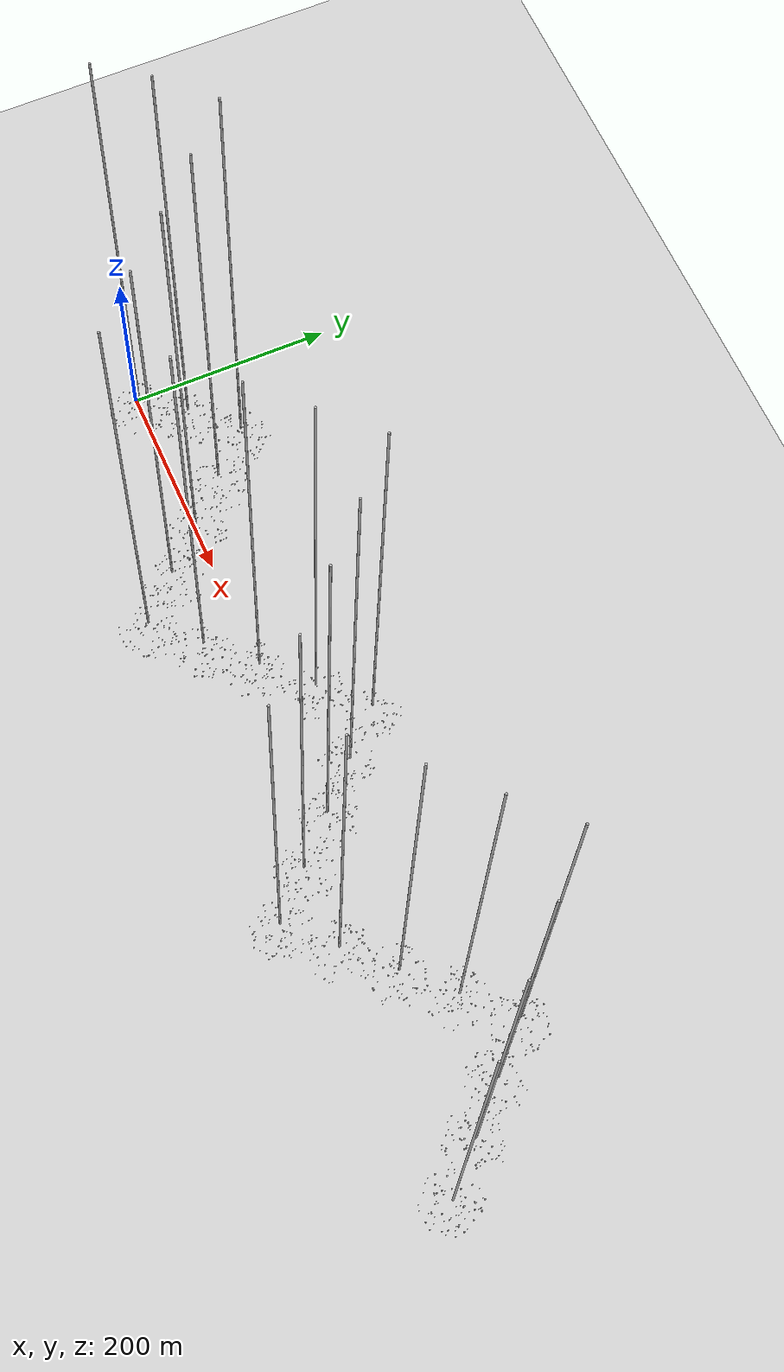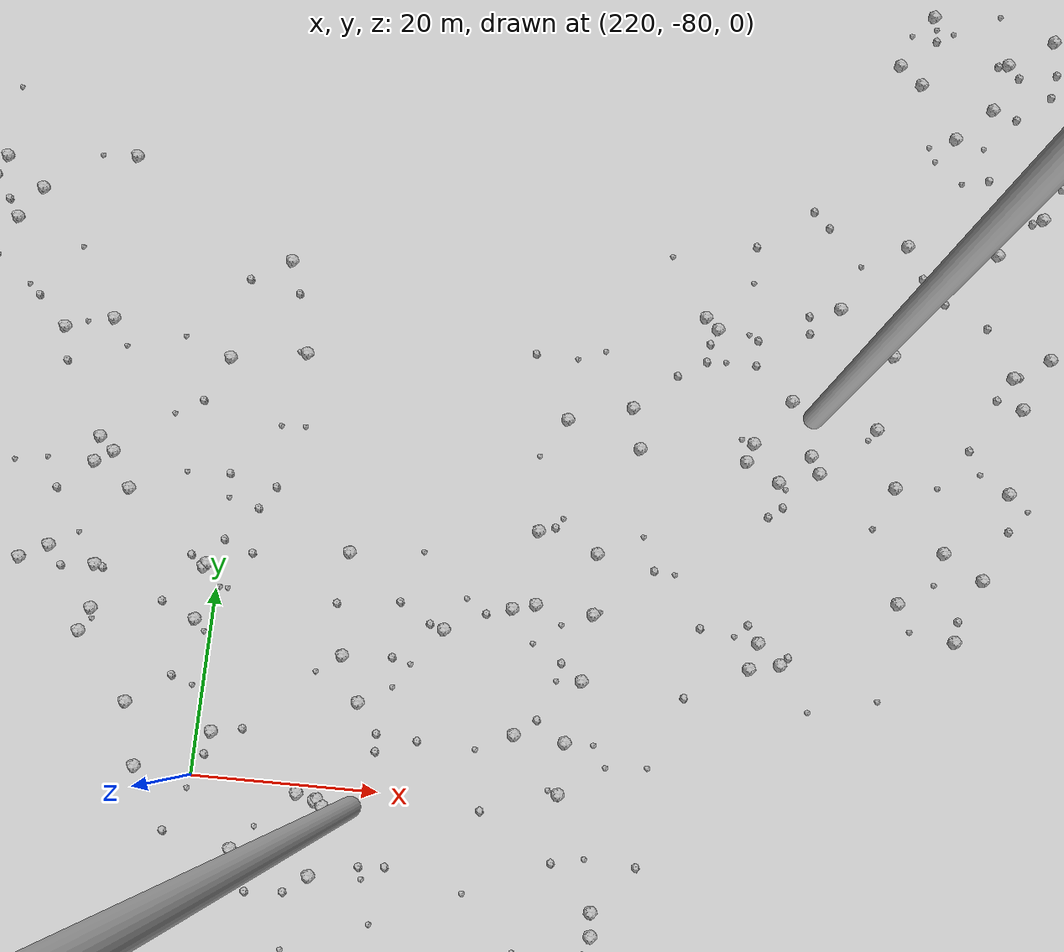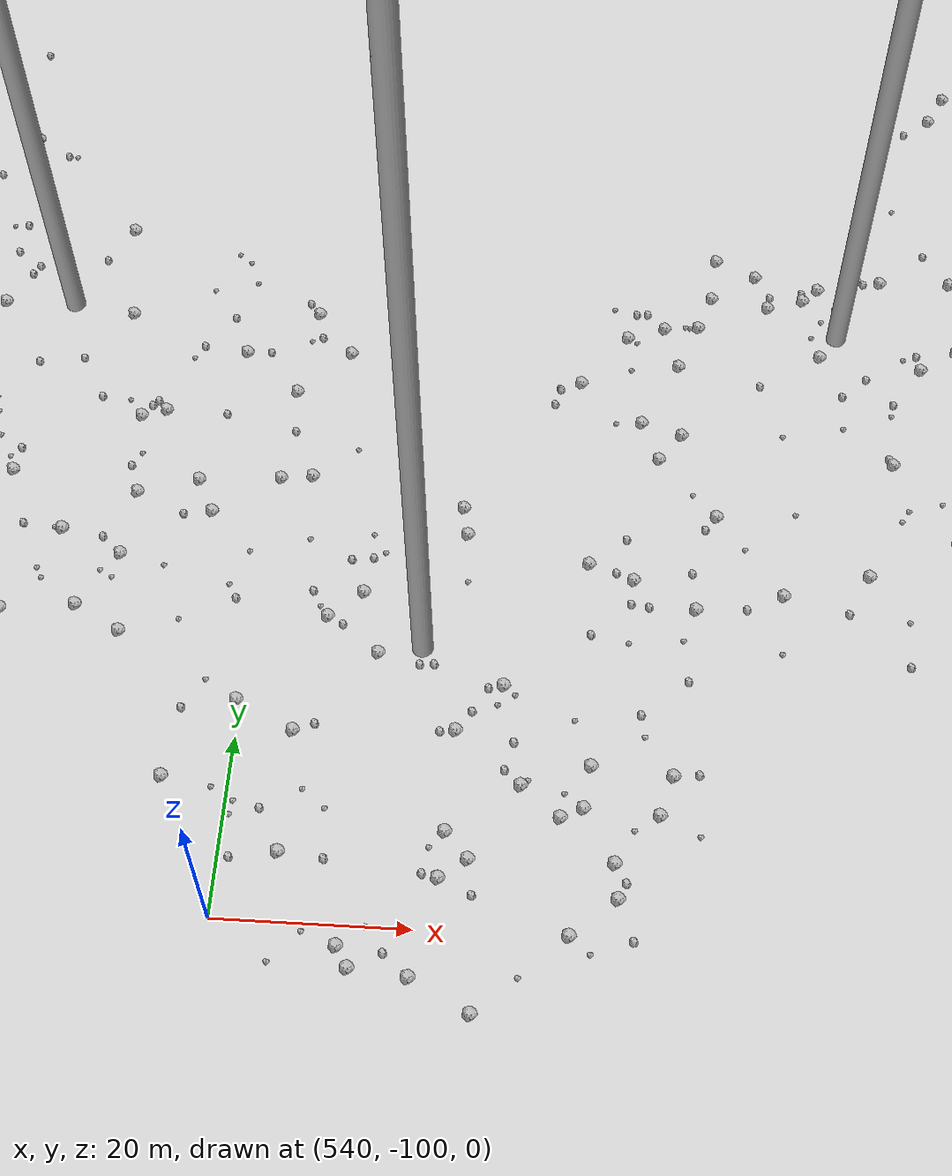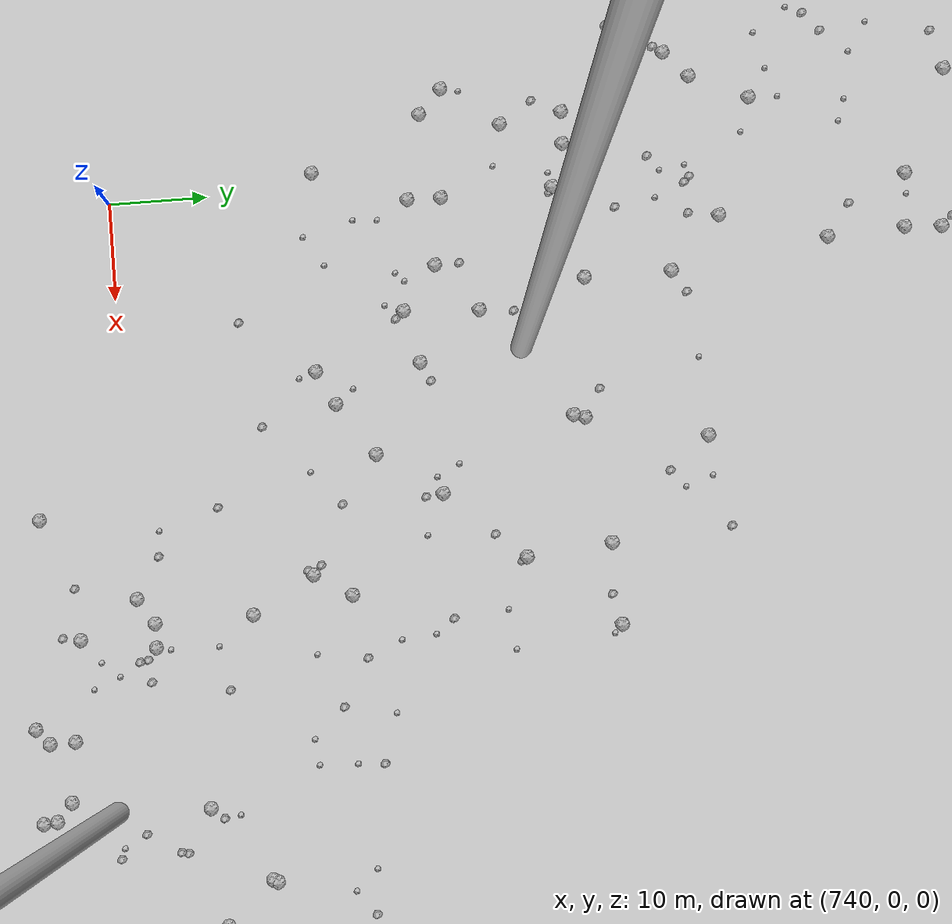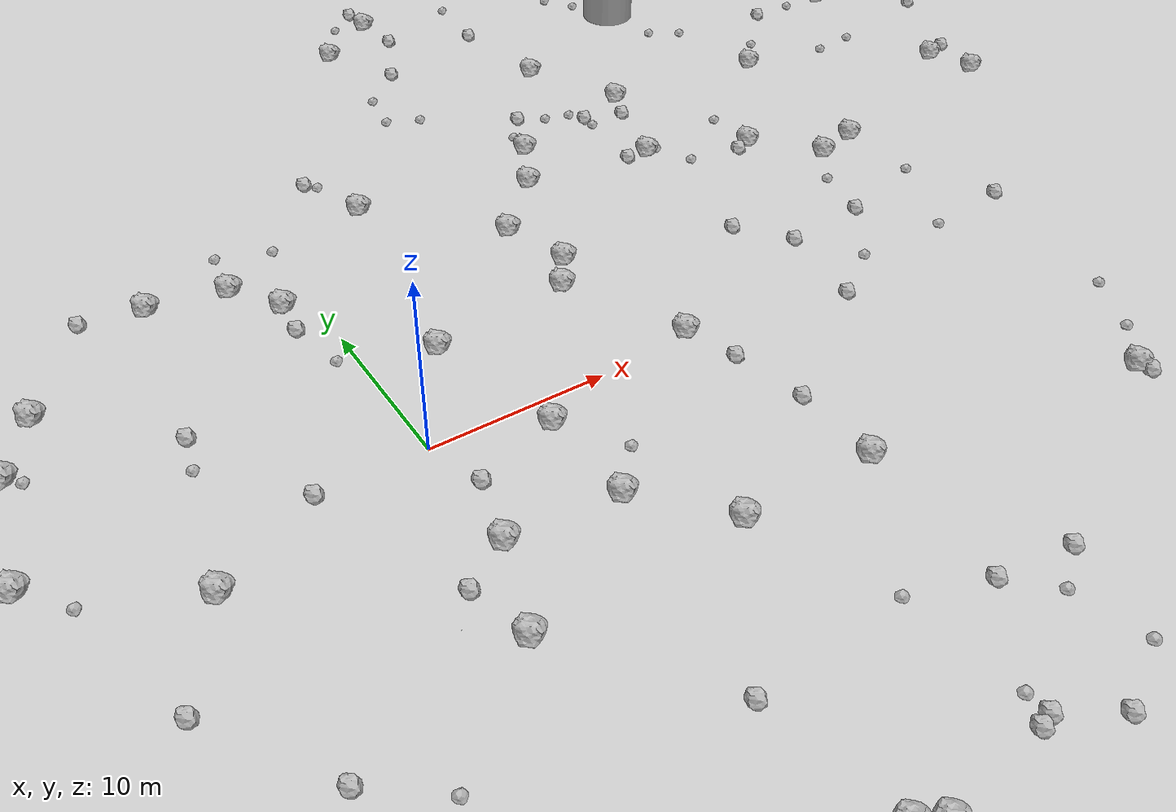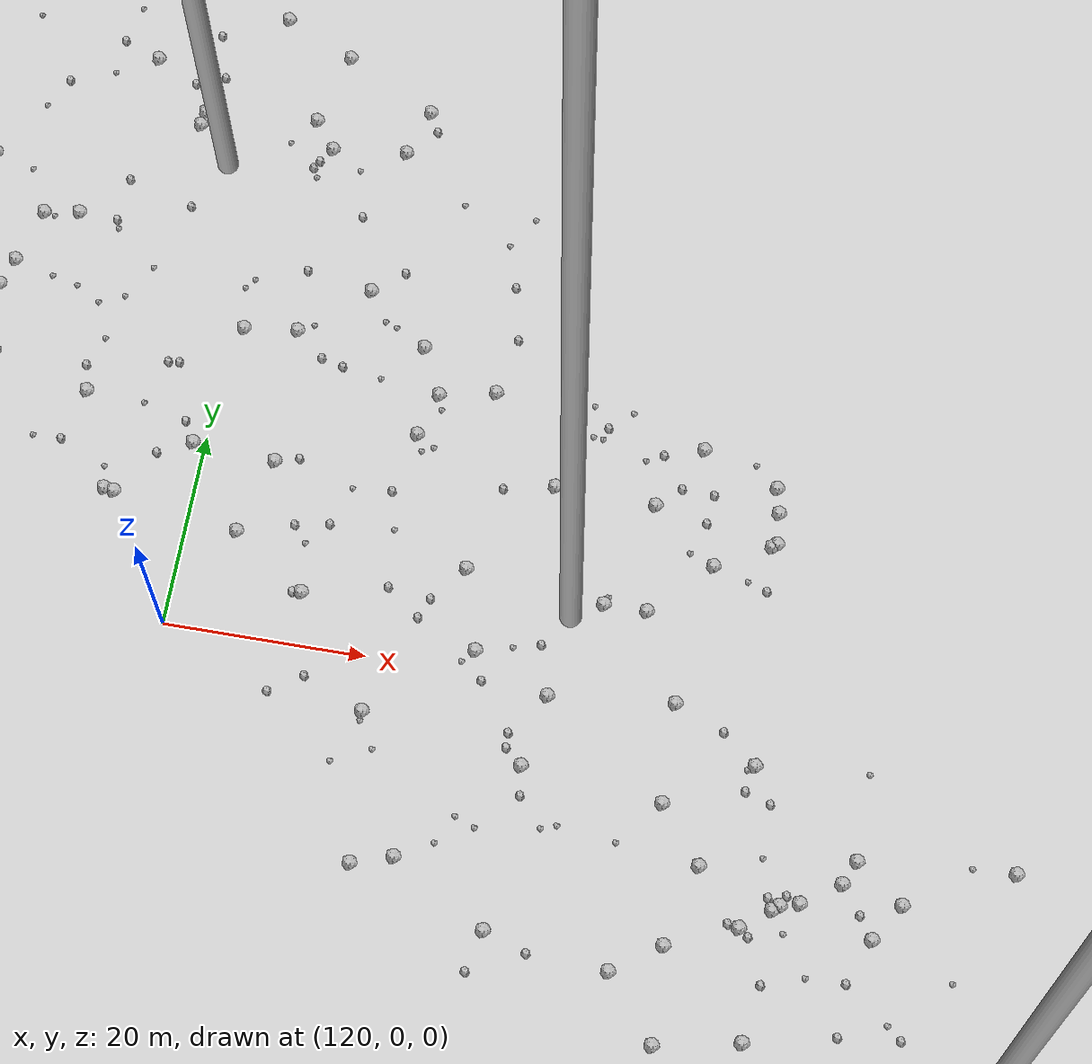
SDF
<sdf version="1.6">
 <world name="default">
  <include><uri>model://custom_ground</uri></include>
  <include><uri>model://sun</uri></include>
  <spherical_coordinates>
   <surface_model>EARTH_WGS84</surface_model>
   <latitude_deg>38.161479</latitude_deg>
   <longitude_deg>-122.454630</longitude_deg>
   <elevation>488.0</elevation>
   <heading_deg>90</heading_deg>
  </spherical_coordinates>
  <model name="rock1_0_0">
   <include><uri>model://rock1</uri><pose>-15.437369852497458 12.386234864009808 0.5 0 0 0</pose></include>
  </model>
  <model name="rock1_0_1">
   <include><uri>model://rock1</uri><pose>16.346683398591203 17.870672610466215 0.5 0 0 0</pose></include>
  </model>
  <model name="rock1_0_2">
   <include><uri>model://rock1</uri><pose>-11.588880502862276 -3.0910449689514756 0.5 0 0 0</pose></include>
  </model>
  <model name="rock1_0_3">
   <include><uri>model://rock1</uri><pose>-1.8687592295983961 -26.150660771009445 0.5 0 0 0</pose></include>
  </model>
  <model name="rock1_0_4">
   <include><uri>model://rock1</uri><pose>6.853723311361087 -27.576320307401296 0.5 0 0 0</pose></include>
  </model>
  <model name="rock1_0_5">
   <include><uri>model://rock1</uri><pose>12.591848755023996 13.928709163325067 0.5 0 0 0</pose></include>
  </model>
  <model name="rock1_0_6">
   <include><uri>model://rock1</uri><pose>-18.91758866211276 1.6774804763114375 0.5 0 0 0</pose></include>
  </model>
  <model name="rock1_0_7">
   <include><uri>model://rock1</uri><pose>6.17777752622932 -7.533626963467391 0.5 0 0 0</pose></include>
  </model>
  <model name="rock1_0_8">
   <include><uri>model://rock1</uri><pose>3.9691411782888295 6.4771196332226495 0.5 0 0 0</pose></include>
  </model>
  <model name="rock1_0_9">
   <include><uri>model://rock1</uri><pose>5.577966931976988 -26.851481594766945 0.5 0 0 0</pose></include>
  </model>
  <model name="rock1_0_10">
   <include><uri>model://rock1</uri><pose>13.810430865486133 9.690829898293778 0.5 0 0 0</pose></include>
  </model>
  <model name="rock1_0_11">
   <include><uri>model://rock1</uri><pose>-7.915619364987323 17.895076785496755 0.5 0 0 0</pose></include>
  </model>
  <model name="rock1_0_12">
   <include><uri>model://rock1</uri><pose>12.387645381192605 7.5905308463645085 0.5 0 0 0</pose></include>
  </model>
  <model name="rock1_0_13">
   <include><uri>model://rock1</uri><pose>34.286321418858364 10.711582712768404 0.5 0 0 0</pose></include>
  </model>
  <model name="rock1_0_14">
   <include><uri>model://rock1</uri><pose>-1.5863501913089735 -12.183474728801446 0.5 0 0 0</pose></include>
  </model>
  <model name="rock1_0_15">
   <include><uri>model://rock1</uri><pose>5.501985316491126 -29.289142118044026 0.5 0 0 0</pose></include>
  </model>
  <model name="rock1_0_16">
   <include><uri>model://rock1</uri><pose>6.001349973866429 -1.6841760647964819 0.5 0 0 0</pose></include>
  </model>
  <model name="rock1_0_17">
   <include><uri>model://rock1</uri><pose>33.7550567025856 -14.265820927350513 0.5 0 0 0</pose></include>
  </model>
  <model name="rock1_0_18">
   <include><uri>model://rock1</uri><pose>17.534963929825118 -11.807966904840299 0.5 0 0 0</pose></include>
  </model>
  <model name="rock1_0_19">
   <include><uri>model://rock1</uri><pose>-3.472403921948249 17.10496111206392 0.5 0 0 0</pose></include>
  </model>
  <model name="rock1_0_20">
   <include><uri>model://rock1</uri><pose>-1.4981211520475455 14.15704872300909 0.5 0 0 0</pose></include>
  </model>
  <model name="rock1_0_21">
   <include><uri>model://rock1</uri><pose>15.745309516618335 0.5402535307308831 0.5 0 0 0</pose></include>
  </model>
  <model name="rock1_0_22">
   <include><uri>model://rock1</uri><pose>-17.681078696928928 8.776866712733494 0.5 0 0 0</pose></include>
  </model>
  <model name="rock1_0_23">
   <include><uri>model://rock1</uri><pose>27.055131388397008 24.035237937603156 0.5 0 0 0</pose></include>
  </model>
  <model name="rock1_0_24">
   <include><uri>model://rock1</uri><pose>9.941409406286073 -11.785064062951097 0.5 0 0 0</pose></include>
  </model>
  <model name="rock1_0_25">
   <include><uri>model://rock1</uri><pose>0.13262440660681918 -7.096585495663604 0.5 0 0 0</pose></include>
  </model>
  <model name="rock1_0_26">
   <include><uri>model://rock1</uri><pose>6.09594022879655 20.7129079406115 0.5 0 0 0</pose></include>
  </model>
  <model name="rock2_0_0">
   <include><uri>model://rock2</uri><pose>33.86038891985302 -14.997258382917762 0.3 0 0 0</pose></include>
  </model>
  <model name="rock2_0_1">
   <include><uri>model://rock2</uri><pose>39.76981902202666 1.2619217833362946 0.3 0 0 0</pose></include>
  </model>
  <model name="rock2_0_2">
   <include><uri>model://rock2</uri><pose>1.0355254836381569 -3.318724499622636 0.3 0 0 0</pose></include>
  </model>
  <model name="rock2_0_3">
   <include><uri>model://rock2</uri><pose>4.29521033549948 24.985952134155518 0.3 0 0 0</pose></include>
  </model>
  <model name="rock2_0_4">
   <include><uri>model://rock2</uri><pose>-5.898405011449006 -0.002287994042713848 0.3 0 0 0</pose></include>
  </model>
  <model name="rock2_0_5">
   <include><uri>model://rock2</uri><pose>-2.592822763080985 -8.752606754663866 0.3 0 0 0</pose></include>
  </model>
  <model name="rock2_0_6">
   <include><uri>model://rock2</uri><pose>-1.7767961662466654 11.817638523527236 0.3 0 0 0</pose></include>
  </model>
  <model name="rock2_0_7">
   <include><uri>model://rock2</uri><pose>4.235853930808172 -27.460428842326678 0.3 0 0 0</pose></include>
  </model>
  <model name="rock2_0_8">
   <include><uri>model://rock2</uri><pose>-10.786654263721463 -14.513573143503319 0.3 0 0 0</pose></include>
  </model>
  <model name="rock2_0_9">
   <include><uri>model://rock2</uri><pose>-11.48863260430354 18.511017667591553 0.3 0 0 0</pose></include>
  </model>
  <model name="rock2_0_10">
   <include><uri>model://rock2</uri><pose>21.0398480024421 -20.929455640365177 0.3 0 0 0</pose></include>
  </model>
  <model name="rock2_0_11">
   <include><uri>model://rock2</uri><pose>-14.852711219410786 -8.409222295714997 0.3 0 0 0</pose></include>
  </model>
  <model name="rock2_0_12">
   <include><uri>model://rock2</uri><pose>16.61053217602899 -2.5423323724041254 0.3 0 0 0</pose></include>
  </model>
  <model name="rock2_0_13">
   <include><uri>model://rock2</uri><pose>26.0261786458817 21.873842161557583 0.3 0 0 0</pose></include>
  </model>
  <model name="rock2_0_14">
   <include><uri>model://rock2</uri><pose>19.66475012049596 24.9566631768283 0.3 0 0 0</pose></include>
  </model>
  <model name="rock2_0_15">
   <include><uri>model://rock2</uri><pose>16.775561208152126 -20.40609098223485 0.3 0 0 0</pose></include>
  </model>
  <model name="rock2_0_16">
   <include><uri>model://rock2</uri><pose>17.44308238689299 -6.86961148934158 0.3 0 0 0</pose></include>
  </model>
  <model name="rock2_0_17">
   <include><uri>model://rock2</uri><pose>12.643805273592804 -26.582426778336288 0.3 0 0 0</pose></include>
  </model>
  <model name="rock2_0_18">
   <include><uri>model://rock2</uri><pose>-9.124090197969526 -19.41482191278055 0.3 0 0 0</pose></include>
  </model>
  <model name="rock2_0_19">
   <include><uri>model://rock2</uri><pose>4.188567504249082 -19.64686896306466 0.3 0 0 0</pose></include>
  </model>
  <model name="rock2_0_20">
   <include><uri>model://rock2</uri><pose>25.215143867545635 -1.5376624617403074 0.3 0 0 0</pose></include>
  </model>
  <model name="rock2_0_21">
   <include><uri>model://rock2</uri><pose>16.13814451169742 -28.026202103386098 0.3 0 0 0</pose></include>
  </model>
  <model name="rock2_0_22">
   <include><uri>model://rock2</uri><pose>31.35502036646443 4.566418338676087 0.3 0 0 0</pose></include>
  </model>
  <model name="rock2_0_23">
   <include><uri>model://rock2</uri><pose>-9.550909395051354 6.8644784418069875 0.3 0 0 0</pose></include>
  </model>
  <model name="rock2_0_24">
   <include><uri>model://rock2</uri><pose>23.841600351412268 6.97377897300489 0.3 0 0 0</pose></include>
  </model>
  <model name="rock2_0_25">
   <include><uri>model://rock2</uri><pose>13.407510124951202 -26.325465457828557 0.3 0 0 0</pose></include>
  </model>
  <model name="rock2_0_26">
   <include><uri>model://rock2</uri><pose>26.11600524511583 4.017645843066262 0.3 0 0 0</pose></include>
  </model>
  <model name="rock3_0_0">
   <include><uri>model://rock3</uri><pose>19.770423449205097 -26.220572813588365 0.2 0 0 0</pose></include>
  </model>
  <model name="rock3_0_1">
   <include><uri>model://rock3</uri><pose>37.191596157164014 6.247432622050937 0.2 0 0 0</pose></include>
  </model>
  <model name="rock3_0_2">
   <include><uri>model://rock3</uri><pose>-16.963259126445216 8.02874845340537 0.2 0 0 0</pose></include>
  </model>
  <model name="rock3_0_3">
   <include><uri>model://rock3</uri><pose>34.432962467442024 0.6345428974181644 0.2 0 0 0</pose></include>
  </model>
  <model name="rock3_0_4">
   <include><uri>model://rock3</uri><pose>32.227619390920324 8.066623198771943 0.2 0 0 0</pose></include>
  </model>
  <model name="rock3_0_5">
   <include><uri>model://rock3</uri><pose>-3.1688808023209205 20.376739547925254 0.2 0 0 0</pose></include>
  </model>
  <model name="rock3_0_6">
   <include><uri>model://rock3</uri><pose>23.543852473276083 21.654542782254254 0.2 0 0 0</pose></include>
  </model>
  <model name="rock3_0_7">
   <include><uri>model://rock3</uri><pose>26.43916310961815 14.528446385008081 0.2 0 0 0</pose></include>
  </model>
  <model name="rock3_0_8">
   <include><uri>model://rock3</uri><pose>12.632324082615156 -18.995252025454974 0.2 0 0 0</pose></include>
  </model>
  <model name="rock3_0_9">
   <include><uri>model://rock3</uri><pose>-17.034013361459287 -0.7076718407898497 0.2 0 0 0</pose></include>
  </model>
  <model name="rock3_0_10">
   <include><uri>model://rock3</uri><pose>-11.900735438472687 -2.6033207009402908 0.2 0 0 0</pose></include>
  </model>
  <model name="rock3_0_11">
   <include><uri>model://rock3</uri><pose>18.272417784875813 23.043535868688714 0.2 0 0 0</pose></include>
  </model>
  <model name="rock3_0_12">
   <include><uri>model://rock3</uri><pose>8.216400900454929 -5.200300217324745 0.2 0 0 0</pose></include>
  </model>
  <model name="rock3_0_13">
   <include><uri>model://rock3</uri><pose>13.316019676691162 -25.176280218633835 0.2 0 0 0</pose></include>
  </model>
  <model name="rock3_0_14">
   <include><uri>model://rock3</uri><pose>37.704181185883606 -8.493458660693221 0.2 0 0 0</pose></include>
  </model>
  <model name="rock3_0_15">
   <include><uri>model://rock3</uri><pose>18.856825990596114 -22.497594457261943 0.2 0 0 0</pose></include>
  </model>
  <model name="rock3_0_16">
   <include><uri>model://rock3</uri><pose>-1.2342891545630899 -22.517167031284714 0.2 0 0 0</pose></include>
  </model>
  <model name="rock3_0_17">
   <include><uri>model://rock3</uri><pose>32.37701142820381 -19.74274840970144 0.2 0 0 0</pose></include>
  </model>
  <model name="rock3_0_18">
   <include><uri>model://rock3</uri><pose>-10.048336500155964 4.535420024731529 0.2 0 0 0</pose></include>
  </model>
  <model name="rock3_0_19">
   <include><uri>model://rock3</uri><pose>35.85141397121168 -11.88579667433227 0.2 0 0 0</pose></include>
  </model>
  <model name="rock3_0_20">
   <include><uri>model://rock3</uri><pose>-7.570899519058576 -17.07211600102164 0.2 0 0 0</pose></include>
  </model>
  <model name="rock3_0_21">
   <include><uri>model://rock3</uri><pose>4.91200068903218 24.32253128113892 0.2 0 0 0</pose></include>
  </model>
  <model name="rock3_0_22">
   <include><uri>model://rock3</uri><pose>21.291265629683643 24.03961322616071 0.2 0 0 0</pose></include>
  </model>
  <model name="rock3_0_23">
   <include><uri>model://rock3</uri><pose>12.123350476274744 29.403464460961203 0.2 0 0 0</pose></include>
  </model>
  <model name="rock3_0_24">
   <include><uri>model://rock3</uri><pose>-0.06552560304311328 19.329507202837753 0.2 0 0 0</pose></include>
  </model>
  <model name="rock3_0_25">
   <include><uri>model://rock3</uri><pose>28.51103204059902 0.6289750546201809 0.2 0 0 0</pose></include>
  </model>
  <model name="rock3_0_26">
   <include><uri>model://rock3</uri><pose>-1.0483512177201746 8.247309769441713 0.2 0 0 0</pose></include>
  </model>
  <model name="rock1_1_0">
   <include><uri>model://rock1</uri><pose>31.003622880026242 14.421205149661745 0.5 0 0 0</pose></include>
  </model>
  <model name="rock1_1_1">
   <include><uri>model://rock1</uri><pose>17.27033729855794 55.64048620059887 0.5 0 0 0</pose></include>
  </model>
  <model name="rock1_1_2">
   <include><uri>model://rock1</uri><pose>56.050952555493645 61.97464162512144 0.5 0 0 0</pose></include>
  </model>
  <model name="rock1_1_3">
   <include><uri>model://rock1</uri><pose>49.3719510877359 40.85069943854314 0.5 0 0 0</pose></include>
  </model>
  <model name="rock1_1_4">
   <include><uri>model://rock1</uri><pose>38.00781471547077 23.086112005125432 0.5 0 0 0</pose></include>
  </model>
  <model name="rock1_1_5">
   <include><uri>model://rock1</uri><pose>69.46194314457568 40.83188672028318 0.5 0 0 0</pose></include>
  </model>
  <model name="rock1_1_6">
   <include><uri>model://rock1</uri><pose>49.96732948282562 17.024160262404692 0.5 0 0 0</pose></include>
  </model>
  <model name="rock1_1_7">
   <include><uri>model://rock1</uri><pose>12.969514618297168 40.32836486809124 0.5 0 0 0</pose></include>
  </model>
  <model name="rock1_1_8">
   <include><uri>model://rock1</uri><pose>24.713568914194173 16.92140117467037 0.5 0 0 0</pose></include>
  </model>
  <model name="rock1_1_9">
   <include><uri>model://rock1</uri><pose>68.87076540760432 39.59505019031901 0.5 0 0 0</pose></include>
  </model>
  <model name="rock1_1_10">
   <include><uri>model://rock1</uri><pose>60.0566859879724 33.80485718445812 0.5 0 0 0</pose></include>
  </model>
  <model name="rock1_1_11">
   <include><uri>model://rock1</uri><pose>49.51997021196062 28.957522602678903 0.5 0 0 0</pose></include>
  </model>
  <model name="rock1_1_12">
   <include><uri>model://rock1</uri><pose>56.54256304338493 54.41589043557845 0.5 0 0 0</pose></include>
  </model>
  <model name="rock1_1_13">
   <include><uri>model://rock1</uri><pose>66.7399962994904 44.18526100749381 0.5 0 0 0</pose></include>
  </model>
  <model name="rock1_1_14">
   <include><uri>model://rock1</uri><pose>24.042584547460088 30.40981683564141 0.5 0 0 0</pose></include>
  </model>
  <model name="rock1_1_15">
   <include><uri>model://rock1</uri><pose>28.94763097979827 53.27888801892735 0.5 0 0 0</pose></include>
  </model>
  <model name="rock1_1_16">
   <include><uri>model://rock1</uri><pose>18.2246516669951 21.429823737323268 0.5 0 0 0</pose></include>
  </model>
  <model name="rock1_1_17">
   <include><uri>model://rock1</uri><pose>38.789144978165666 64.23087924050779 0.5 0 0 0</pose></include>
  </model>
  <model name="rock1_1_18">
   <include><uri>model://rock1</uri><pose>50.99822988129733 13.999893491910285 0.5 0 0 0</pose></include>
  </model>
  <model name="rock1_1_19">
   <include><uri>model://rock1</uri><pose>58.7804780634641 62.26480593646234 0.5 0 0 0</pose></include>
  </model>
  <model name="rock1_1_20">
   <include><uri>model://rock1</uri><pose>55.38724387108865 25.833833966039094 0.5 0 0 0</pose></include>
  </model>
  <model name="rock1_1_21">
   <include><uri>model://rock1</uri><pose>34.33550500604959 41.80915847911865 0.5 0 0 0</pose></include>
  </model>
  <model name="rock1_1_22">
   <include><uri>model://rock1</uri><pose>39.71244678583625 69.90780280636511 0.5 0 0 0</pose></include>
  </model>
  <model name="rock1_1_23">
   <include><uri>model://rock1</uri><pose>17.23007440587863 43.66203998372873 0.5 0 0 0</pose></include>
  </model>
  <model name="rock1_1_24">
   <include><uri>model://rock1</uri><pose>37.19271025645449 11.497835372705712 0.5 0 0 0</pose></include>
  </model>
  <model name="rock1_1_25">
   <include><uri>model://rock1</uri><pose>41.193439392117526 56.19209662867372 0.5 0 0 0</pose></include>
  </model>
  <model name="rock1_1_26">
   <include><uri>model://rock1</uri><pose>31.44820730990579 58.53248817635452 0.5 0 0 0</pose></include>
  </model>
  <model name="rock2_1_0">
   <include><uri>model://rock2</uri><pose>68.0070956256458 49.73335779060734 0.3 0 0 0</pose></include>
  </model>
  <model name="rock2_1_1">
   <include><uri>model://rock2</uri><pose>40.52314940944851 51.60025265012294 0.3 0 0 0</pose></include>
  </model>
  <model name="rock2_1_2">
   <include><uri>model://rock2</uri><pose>29.789378739081435 13.956960230572939 0.3 0 0 0</pose></include>
  </model>
  <model name="rock2_1_3">
   <include><uri>model://rock2</uri><pose>40.761734527358044 66.19471945187519 0.3 0 0 0</pose></include>
  </model>
  <model name="rock2_1_4">
   <include><uri>model://rock2</uri><pose>26.399348538424327 52.143423877724125 0.3 0 0 0</pose></include>
  </model>
  <model name="rock2_1_5">
   <include><uri>model://rock2</uri><pose>60.85613656851705 39.33065107389196 0.3 0 0 0</pose></include>
  </model>
  <model name="rock2_1_6">
   <include><uri>model://rock2</uri><pose>23.143261006832766 16.9242818211219 0.3 0 0 0</pose></include>
  </model>
  <model name="rock2_1_7">
   <include><uri>model://rock2</uri><pose>43.43456672363575 28.950006136397953 0.3 0 0 0</pose></include>
  </model>
  <model name="rock2_1_8">
   <include><uri>model://rock2</uri><pose>47.99096092472377 34.73395810348681 0.3 0 0 0</pose></include>
  </model>
  <model name="rock2_1_9">
   <include><uri>model://rock2</uri><pose>58.66975248229612 45.120455376076436 0.3 0 0 0</pose></include>
  </model>
  <model name="rock2_1_10">
   <include><uri>model://rock2</uri><pose>22.97817498599575 37.783521074027476 0.3 0 0 0</pose></include>
  </model>
  <model name="rock2_1_11">
   <include><uri>model://rock2</uri><pose>54.514205174247195 62.40936057748446 0.3 0 0 0</pose></include>
  </model>
  <model name="rock2_1_12">
   <include><uri>model://rock2</uri><pose>51.69237491819797 40.64312001123888 0.3 0 0 0</pose></include>
  </model>
  <model name="rock2_1_13">
   <include><uri>model://rock2</uri><pose>29.22792827114552 55.46230173876033 0.3 0 0 0</pose></include>
  </model>
  <model name="rock2_1_14">
   <include><uri>model://rock2</uri><pose>54.802850504262906 24.412265263313767 0.3 0 0 0</pose></include>
  </model>
  <model name="rock2_1_15">
   <include><uri>model://rock2</uri><pose>51.635194881008765 17.620747677747573 0.3 0 0 0</pose></include>
  </model>
  <model name="rock2_1_16">
   <include><uri>model://rock2</uri><pose>42.04210545364574 59.352986465974745 0.3 0 0 0</pose></include>
  </model>
  <model name="rock2_1_17">
   <include><uri>model://rock2</uri><pose>50.69809372448392 56.999274856987434 0.3 0 0 0</pose></include>
  </model>
  <model name="rock2_1_18">
   <include><uri>model://rock2</uri><pose>57.256511334771524 55.956495500778104 0.3 0 0 0</pose></include>
  </model>
  <model name="rock2_1_19">
   <include><uri>model://rock2</uri><pose>46.80228428805912 60.755622938608774 0.3 0 0 0</pose></include>
  </model>
  <model name="rock2_1_20">
   <include><uri>model://rock2</uri><pose>15.381798073368625 35.2890760355463 0.3 0 0 0</pose></include>
  </model>
  <model name="rock2_1_21">
   <include><uri>model://rock2</uri><pose>61.137422334510276 52.37531354920061 0.3 0 0 0</pose></include>
  </model>
  <model name="rock2_1_22">
   <include><uri>model://rock2</uri><pose>17.546863656510148 40.12534555331665 0.3 0 0 0</pose></include>
  </model>
  <model name="rock2_1_23">
   <include><uri>model://rock2</uri><pose>16.984070627640655 45.86129564235965 0.3 0 0 0</pose></include>
  </model>
  <model name="rock2_1_24">
   <include><uri>model://rock2</uri><pose>23.522135493334222 22.663048779231126 0.3 0 0 0</pose></include>
  </model>
  <model name="rock2_1_25">
   <include><uri>model://rock2</uri><pose>45.07318542852987 42.171516975759076 0.3 0 0 0</pose></include>
  </model>
  <model name="rock2_1_26">
   <include><uri>model://rock2</uri><pose>39.37146289280906 64.22300942359912 0.3 0 0 0</pose></include>
  </model>
  <model name="rock3_1_0">
   <include><uri>model://rock3</uri><pose>32.36145451160568 38.01764536051901 0.2 0 0 0</pose></include>
  </model>
  <model name="rock3_1_1">
   <include><uri>model://rock3</uri><pose>32.8980970179586 45.314446100088034 0.2 0 0 0</pose></include>
  </model>
  <model name="rock3_1_2">
   <include><uri>model://rock3</uri><pose>49.70005184009169 33.337873952022846 0.2 0 0 0</pose></include>
  </model>
  <model name="rock3_1_3">
   <include><uri>model://rock3</uri><pose>52.98097191081578 66.87543266062723 0.2 0 0 0</pose></include>
  </model>
  <model name="rock3_1_4">
   <include><uri>model://rock3</uri><pose>14.172415996782654 28.475520267450143 0.2 0 0 0</pose></include>
  </model>
  <model name="rock3_1_5">
   <include><uri>model://rock3</uri><pose>36.58644994329636 29.701537687957014 0.2 0 0 0</pose></include>
  </model>
  <model name="rock3_1_6">
   <include><uri>model://rock3</uri><pose>30.56312750625391 66.44292200948635 0.2 0 0 0</pose></include>
  </model>
  <model name="rock3_1_7">
   <include><uri>model://rock3</uri><pose>35.263062159773 66.60585540345303 0.2 0 0 0</pose></include>
  </model>
  <model name="rock3_1_8">
   <include><uri>model://rock3</uri><pose>28.563370725803257 51.77585869761468 0.2 0 0 0</pose></include>
  </model>
  <model name="rock3_1_9">
   <include><uri>model://rock3</uri><pose>22.91477492777245 23.63648955766491 0.2 0 0 0</pose></include>
  </model>
  <model name="rock3_1_10">
   <include><uri>model://rock3</uri><pose>46.669128336325294 22.361245913033287 0.2 0 0 0</pose></include>
  </model>
  <model name="rock3_1_11">
   <include><uri>model://rock3</uri><pose>60.39797428587708 60.9700147892939 0.2 0 0 0</pose></include>
  </model>
  <model name="rock3_1_12">
   <include><uri>model://rock3</uri><pose>41.907646726581575 42.92189481307542 0.2 0 0 0</pose></include>
  </model>
  <model name="rock3_1_13">
   <include><uri>model://rock3</uri><pose>23.500617419539534 55.2150125166345 0.2 0 0 0</pose></include>
  </model>
  <model name="rock3_1_14">
   <include><uri>model://rock3</uri><pose>24.42899945325707 52.68062556351778 0.2 0 0 0</pose></include>
  </model>
  <model name="rock3_1_15">
   <include><uri>model://rock3</uri><pose>49.76361552564271 60.4203056288918 0.2 0 0 0</pose></include>
  </model>
  <model name="rock3_1_16">
   <include><uri>model://rock3</uri><pose>12.588697634980146 32.46597104355132 0.2 0 0 0</pose></include>
  </model>
  <model name="rock3_1_17">
   <include><uri>model://rock3</uri><pose>30.991241542410833 39.967828032676515 0.2 0 0 0</pose></include>
  </model>
  <model name="rock3_1_18">
   <include><uri>model://rock3</uri><pose>43.742478134001956 21.976773739103223 0.2 0 0 0</pose></include>
  </model>
  <model name="rock3_1_19">
   <include><uri>model://rock3</uri><pose>51.30570101557747 54.377714346861076 0.2 0 0 0</pose></include>
  </model>
  <model name="rock3_1_20">
   <include><uri>model://rock3</uri><pose>39.95102893272953 25.308304700464774 0.2 0 0 0</pose></include>
  </model>
  <model name="rock3_1_21">
   <include><uri>model://rock3</uri><pose>25.32961100967228 16.86468658345383 0.2 0 0 0</pose></include>
  </model>
  <model name="rock3_1_22">
   <include><uri>model://rock3</uri><pose>23.425947160461178 42.767692855092534 0.2 0 0 0</pose></include>
  </model>
  <model name="rock3_1_23">
   <include><uri>model://rock3</uri><pose>34.66332346231939 30.947906949015 0.2 0 0 0</pose></include>
  </model>
  <model name="rock3_1_24">
   <include><uri>model://rock3</uri><pose>46.436003156688244 28.999053372244756 0.2 0 0 0</pose></include>
  </model>
  <model name="rock3_1_25">
   <include><uri>model://rock3</uri><pose>14.977785207642711 44.0286434144339 0.2 0 0 0</pose></include>
  </model>
  <model name="rock3_1_26">
   <include><uri>model://rock3</uri><pose>30.77480775428725 17.794340939324513 0.2 0 0 0</pose></include>
  </model>
  <model name="rock1_2_0">
   <include><uri>model://rock1</uri><pose>74.32199923013656 58.43399171405403 0.5 0 0 0</pose></include>
  </model>
  <model name="rock1_2_1">
   <include><uri>model://rock1</uri><pose>84.33246006806124 76.09243905061224 0.5 0 0 0</pose></include>
  </model>
  <model name="rock1_2_2">
   <include><uri>model://rock1</uri><pose>93.71993873062479 78.89156273657056 0.5 0 0 0</pose></include>
  </model>
  <model name="rock1_2_3">
   <include><uri>model://rock1</uri><pose>52.75998734161318 73.65212547791496 0.5 0 0 0</pose></include>
  </model>
  <model name="rock1_2_4">
   <include><uri>model://rock1</uri><pose>71.45215421034378 79.65290711090569 0.5 0 0 0</pose></include>
  </model>
  <model name="rock1_2_5">
   <include><uri>model://rock1</uri><pose>81.08361382988676 91.11134649511507 0.5 0 0 0</pose></include>
  </model>
  <model name="rock1_2_6">
   <include><uri>model://rock1</uri><pose>52.41715436480429 75.60464799657072 0.5 0 0 0</pose></include>
  </model>
  <model name="rock1_2_7">
   <include><uri>model://rock1</uri><pose>56.12608043437422 78.16315694100652 0.5 0 0 0</pose></include>
  </model>
  <model name="rock1_2_8">
   <include><uri>model://rock1</uri><pose>95.2302375689919 96.70351956128444 0.5 0 0 0</pose></include>
  </model>
  <model name="rock1_2_9">
   <include><uri>model://rock1</uri><pose>85.6780912743412 72.49425910325103 0.5 0 0 0</pose></include>
  </model>
  <model name="rock1_2_10">
   <include><uri>model://rock1</uri><pose>83.85433525723559 68.98325903204116 0.5 0 0 0</pose></include>
  </model>
  <model name="rock1_2_11">
   <include><uri>model://rock1</uri><pose>95.83663778604306 89.6116906265558 0.5 0 0 0</pose></include>
  </model>
  <model name="rock1_2_12">
   <include><uri>model://rock1</uri><pose>72.72003656143885 54.77211664903679 0.5 0 0 0</pose></include>
  </model>
  <model name="rock1_2_13">
   <include><uri>model://rock1</uri><pose>75.09928909263894 82.59875369523148 0.5 0 0 0</pose></include>
  </model>
  <model name="rock1_2_14">
   <include><uri>model://rock1</uri><pose>88.6983575468071 94.62875791707458 0.5 0 0 0</pose></include>
  </model>
  <model name="rock1_2_15">
   <include><uri>model://rock1</uri><pose>79.42654853392594 66.15516049069574 0.5 0 0 0</pose></include>
  </model>
  <model name="rock1_2_16">
   <include><uri>model://rock1</uri><pose>57.014467706612024 98.51115684096942 0.5 0 0 0</pose></include>
  </model>
  <model name="rock1_2_17">
   <include><uri>model://rock1</uri><pose>88.82914451165595 102.3212878330177 0.5 0 0 0</pose></include>
  </model>
  <model name="rock1_2_18">
   <include><uri>model://rock1</uri><pose>83.258328011129 69.11812779471867 0.5 0 0 0</pose></include>
  </model>
  <model name="rock1_2_19">
   <include><uri>model://rock1</uri><pose>59.65575529449361 62.37187500455201 0.5 0 0 0</pose></include>
  </model>
  <model name="rock1_2_20">
   <include><uri>model://rock1</uri><pose>74.05740926100651 104.59204490519772 0.5 0 0 0</pose></include>
  </model>
  <model name="rock1_2_21">
   <include><uri>model://rock1</uri><pose>99.43716328257452 92.15088401051159 0.5 0 0 0</pose></include>
  </model>
  <model name="rock1_2_22">
   <include><uri>model://rock1</uri><pose>87.26600310475527 96.00969706449561 0.5 0 0 0</pose></include>
  </model>
  <model name="rock1_2_23">
   <include><uri>model://rock1</uri><pose>69.45199297158692 85.95796667531624 0.5 0 0 0</pose></include>
  </model>
  <model name="rock1_2_24">
   <include><uri>model://rock1</uri><pose>51.98575921573663 79.39749392455971 0.5 0 0 0</pose></include>
  </model>
  <model name="rock1_2_25">
   <include><uri>model://rock1</uri><pose>69.2317479685569 90.59506784162139 0.5 0 0 0</pose></include>
  </model>
  <model name="rock1_2_26">
   <include><uri>model://rock1</uri><pose>96.89938837234548 82.57017123587738 0.5 0 0 0</pose></include>
  </model>
  <model name="rock2_2_0">
   <include><uri>model://rock2</uri><pose>63.50761869988005 72.10466383119946 0.3 0 0 0</pose></include>
  </model>
  <model name="rock2_2_1">
   <include><uri>model://rock2</uri><pose>107.03667126742079 82.72421925954592 0.3 0 0 0</pose></include>
  </model>
  <model name="rock2_2_2">
   <include><uri>model://rock2</uri><pose>72.99572060512159 80.31847295570071 0.3 0 0 0</pose></include>
  </model>
  <model name="rock2_2_3">
   <include><uri>model://rock2</uri><pose>76.25380273171385 73.1336975902689 0.3 0 0 0</pose></include>
  </model>
  <model name="rock2_2_4">
   <include><uri>model://rock2</uri><pose>97.20299063345229 57.580230822903204 0.3 0 0 0</pose></include>
  </model>
  <model name="rock2_2_5">
   <include><uri>model://rock2</uri><pose>105.56169203140229 70.92379045489639 0.3 0 0 0</pose></include>
  </model>
  <model name="rock2_2_6">
   <include><uri>model://rock2</uri><pose>73.9291390970369 74.03162090612251 0.3 0 0 0</pose></include>
  </model>
  <model name="rock2_2_7">
   <include><uri>model://rock2</uri><pose>57.730234932052895 72.11053267887675 0.3 0 0 0</pose></include>
  </model>
  <model name="rock2_2_8">
   <include><uri>model://rock2</uri><pose>73.02575808618434 96.7486524768423 0.3 0 0 0</pose></include>
  </model>
  <model name="rock2_2_9">
   <include><uri>model://rock2</uri><pose>63.627855032548766 75.99138154539645 0.3 0 0 0</pose></include>
  </model>
  <model name="rock2_2_10">
   <include><uri>model://rock2</uri><pose>68.61073706524509 56.58166142167136 0.3 0 0 0</pose></include>
  </model>
  <model name="rock2_2_11">
   <include><uri>model://rock2</uri><pose>58.93662798104954 77.14676414980457 0.3 0 0 0</pose></include>
  </model>
  <model name="rock2_2_12">
   <include><uri>model://rock2</uri><pose>88.73930822836817 107.00899021835018 0.3 0 0 0</pose></include>
  </model>
  <model name="rock2_2_13">
   <include><uri>model://rock2</uri><pose>73.87122704840749 68.1151463656866 0.3 0 0 0</pose></include>
  </model>
  <model name="rock2_2_14">
   <include><uri>model://rock2</uri><pose>100.74105691205776 83.01752498096113 0.3 0 0 0</pose></include>
  </model>
  <model name="rock2_2_15">
   <include><uri>model://rock2</uri><pose>102.7169192941765 84.02876681239084 0.3 0 0 0</pose></include>
  </model>
  <model name="rock2_2_16">
   <include><uri>model://rock2</uri><pose>98.58336686492515 69.33273956982326 0.3 0 0 0</pose></include>
  </model>
  <model name="rock2_2_17">
   <include><uri>model://rock2</uri><pose>90.91592973493539 71.10525291476523 0.3 0 0 0</pose></include>
  </model>
  <model name="rock2_2_18">
   <include><uri>model://rock2</uri><pose>62.66384044796075 97.30512524167435 0.3 0 0 0</pose></include>
  </model>
  <model name="rock2_2_19">
   <include><uri>model://rock2</uri><pose>56.09522370423543 75.89786303321787 0.3 0 0 0</pose></include>
  </model>
  <model name="rock2_2_20">
   <include><uri>model://rock2</uri><pose>73.43799536937254 58.45382646599073 0.3 0 0 0</pose></include>
  </model>
  <model name="rock2_2_21">
   <include><uri>model://rock2</uri><pose>82.51381527473721 88.35091558379771 0.3 0 0 0</pose></include>
  </model>
  <model name="rock2_2_22">
   <include><uri>model://rock2</uri><pose>53.19823404389917 89.20291739121758 0.3 0 0 0</pose></include>
  </model>
  <model name="rock2_2_23">
   <include><uri>model://rock2</uri><pose>59.25908069796749 63.14414462450928 0.3 0 0 0</pose></include>
  </model>
  <model name="rock2_2_24">
   <include><uri>model://rock2</uri><pose>73.51646760333423 94.16176226829299 0.3 0 0 0</pose></include>
  </model>
  <model name="rock2_2_25">
   <include><uri>model://rock2</uri><pose>85.39596671622826 53.952339675354814 0.3 0 0 0</pose></include>
  </model>
  <model name="rock2_2_26">
   <include><uri>model://rock2</uri><pose>87.37672904058405 98.75586879488856 0.3 0 0 0</pose></include>
  </model>
  <model name="rock3_2_0">
   <include><uri>model://rock3</uri><pose>72.0552077106372 98.24404960626569 0.2 0 0 0</pose></include>
  </model>
  <model name="rock3_2_1">
   <include><uri>model://rock3</uri><pose>59.85075320381584 73.17295178140662 0.2 0 0 0</pose></include>
  </model>
  <model name="rock3_2_2">
   <include><uri>model://rock3</uri><pose>101.64353037865985 59.34209430840316 0.2 0 0 0</pose></include>
  </model>
  <model name="rock3_2_3">
   <include><uri>model://rock3</uri><pose>104.87397500255045 81.30398154275477 0.2 0 0 0</pose></include>
  </model>
  <model name="rock3_2_4">
   <include><uri>model://rock3</uri><pose>53.68230760907857 68.8446881569554 0.2 0 0 0</pose></include>
  </model>
  <model name="rock3_2_5">
   <include><uri>model://rock3</uri><pose>64.78954693295108 64.91452811775774 0.2 0 0 0</pose></include>
  </model>
  <model name="rock3_2_6">
   <include><uri>model://rock3</uri><pose>102.79002744965658 67.43802434976148 0.2 0 0 0</pose></include>
  </model>
  <model name="rock3_2_7">
   <include><uri>model://rock3</uri><pose>70.93639863425875 66.49474764263596 0.2 0 0 0</pose></include>
  </model>
  <model name="rock3_2_8">
   <include><uri>model://rock3</uri><pose>93.97595496168302 79.82158834370243 0.2 0 0 0</pose></include>
  </model>
  <model name="rock3_2_9">
   <include><uri>model://rock3</uri><pose>99.72562979422992 74.37512854001142 0.2 0 0 0</pose></include>
  </model>
  <model name="rock3_2_10">
   <include><uri>model://rock3</uri><pose>56.414773336869885 65.46534377321376 0.2 0 0 0</pose></include>
  </model>
  <model name="rock3_2_11">
   <include><uri>model://rock3</uri><pose>70.80685307110252 105.73054868919021 0.2 0 0 0</pose></include>
  </model>
  <model name="rock3_2_12">
   <include><uri>model://rock3</uri><pose>61.21908180306242 65.34000850567799 0.2 0 0 0</pose></include>
  </model>
  <model name="rock3_2_13">
   <include><uri>model://rock3</uri><pose>77.40152034856001 102.53753136138374 0.2 0 0 0</pose></include>
  </model>
  <model name="rock3_2_14">
   <include><uri>model://rock3</uri><pose>84.60935627783715 56.357727378655696 0.2 0 0 0</pose></include>
  </model>
  <model name="rock3_2_15">
   <include><uri>model://rock3</uri><pose>101.99365912867682 73.18371628050873 0.2 0 0 0</pose></include>
  </model>
  <model name="rock3_2_16">
   <include><uri>model://rock3</uri><pose>87.85470070484962 104.52272589680993 0.2 0 0 0</pose></include>
  </model>
  <model name="rock3_2_17">
   <include><uri>model://rock3</uri><pose>107.09965990757959 85.78369911885984 0.2 0 0 0</pose></include>
  </model>
  <model name="rock3_2_18">
   <include><uri>model://rock3</uri><pose>84.74661050905135 92.59129969116002 0.2 0 0 0</pose></include>
  </model>
  <model name="rock3_2_19">
   <include><uri>model://rock3</uri><pose>94.53460651812614 77.59741957939086 0.2 0 0 0</pose></include>
  </model>
  <model name="rock3_2_20">
   <include><uri>model://rock3</uri><pose>85.69493362533845 55.03447775945483 0.2 0 0 0</pose></include>
  </model>
  <model name="rock3_2_21">
   <include><uri>model://rock3</uri><pose>92.38197545364001 64.87153125560874 0.2 0 0 0</pose></include>
  </model>
  <model name="rock3_2_22">
   <include><uri>model://rock3</uri><pose>67.617530682809 66.41295835273385 0.2 0 0 0</pose></include>
  </model>
  <model name="rock3_2_23">
   <include><uri>model://rock3</uri><pose>88.91889107018721 108.6114937449878 0.2 0 0 0</pose></include>
  </model>
  <model name="rock3_2_24">
   <include><uri>model://rock3</uri><pose>53.42457173410309 69.00690443209878 0.2 0 0 0</pose></include>
  </model>
  <model name="rock3_2_25">
   <include><uri>model://rock3</uri><pose>101.40975410637665 90.15332821981268 0.2 0 0 0</pose></include>
  </model>
  <model name="rock3_2_26">
   <include><uri>model://rock3</uri><pose>63.23770751345032 91.90939390292064 0.2 0 0 0</pose></include>
  </model>
  <model name="rock1_3_0">
   <include><uri>model://rock1</uri><pose>101.76129464885273 42.456955661876776 0.5 0 0 0</pose></include>
  </model>
  <model name="rock1_3_1">
   <include><uri>model://rock1</uri><pose>141.98026538649137 28.37905106571859 0.5 0 0 0</pose></include>
  </model>
  <model name="rock1_3_2">
   <include><uri>model://rock1</uri><pose>118.38189920441447 68.60669501304 0.5 0 0 0</pose></include>
  </model>
  <model name="rock1_3_3">
   <include><uri>model://rock1</uri><pose>112.06053539120981 56.164952959569504 0.5 0 0 0</pose></include>
  </model>
  <model name="rock1_3_4">
   <include><uri>model://rock1</uri><pose>126.57620193837428 33.0170838606898 0.5 0 0 0</pose></include>
  </model>
  <model name="rock1_3_5">
   <include><uri>model://rock1</uri><pose>96.56438116989922 36.08138977529896 0.5 0 0 0</pose></include>
  </model>
  <model name="rock1_3_6">
   <include><uri>model://rock1</uri><pose>118.79848942978145 19.15079654732157 0.5 0 0 0</pose></include>
  </model>
  <model name="rock1_3_7">
   <include><uri>model://rock1</uri><pose>95.62520174913591 33.11487264527822 0.5 0 0 0</pose></include>
  </model>
  <model name="rock1_3_8">
   <include><uri>model://rock1</uri><pose>147.6136533168185 29.563863263124894 0.5 0 0 0</pose></include>
  </model>
  <model name="rock1_3_9">
   <include><uri>model://rock1</uri><pose>111.18955942199852 12.873409910919138 0.5 0 0 0</pose></include>
  </model>
  <model name="rock1_3_10">
   <include><uri>model://rock1</uri><pose>91.62581023453814 47.88310861675741 0.5 0 0 0</pose></include>
  </model>
  <model name="rock1_3_11">
   <include><uri>model://rock1</uri><pose>107.08004671527172 22.917998044537484 0.5 0 0 0</pose></include>
  </model>
  <model name="rock1_3_12">
   <include><uri>model://rock1</uri><pose>140.64764934852207 23.75627476125475 0.5 0 0 0</pose></include>
  </model>
  <model name="rock1_3_13">
   <include><uri>model://rock1</uri><pose>123.72499927199597 57.14855389602669 0.5 0 0 0</pose></include>
  </model>
  <model name="rock1_3_14">
   <include><uri>model://rock1</uri><pose>126.0113841106118 54.07681306989116 0.5 0 0 0</pose></include>
  </model>
  <model name="rock1_3_15">
   <include><uri>model://rock1</uri><pose>105.83088394910236 61.63615631697145 0.5 0 0 0</pose></include>
  </model>
  <model name="rock1_3_16">
   <include><uri>model://rock1</uri><pose>98.17467013668197 41.85404183536164 0.5 0 0 0</pose></include>
  </model>
  <model name="rock1_3_17">
   <include><uri>model://rock1</uri><pose>111.85415882323657 54.62811840206413 0.5 0 0 0</pose></include>
  </model>
  <model name="rock1_3_18">
   <include><uri>model://rock1</uri><pose>125.73728078215865 65.09998765534107 0.5 0 0 0</pose></include>
  </model>
  <model name="rock1_3_19">
   <include><uri>model://rock1</uri><pose>121.19002874879503 32.366297314437084 0.5 0 0 0</pose></include>
  </model>
  <model name="rock1_3_20">
   <include><uri>model://rock1</uri><pose>127.23064952279438 18.52399817559997 0.5 0 0 0</pose></include>
  </model>
  <model name="rock1_3_21">
   <include><uri>model://rock1</uri><pose>112.18888071746534 12.715897911516867 0.5 0 0 0</pose></include>
  </model>
  <model name="rock1_3_22">
   <include><uri>model://rock1</uri><pose>135.23163302734437 60.04175860991989 0.5 0 0 0</pose></include>
  </model>
  <model name="rock1_3_23">
   <include><uri>model://rock1</uri><pose>133.07952516873445 38.629662739597904 0.5 0 0 0</pose></include>
  </model>
  <model name="rock1_3_24">
   <include><uri>model://rock1</uri><pose>133.61936790516933 54.92690617711009 0.5 0 0 0</pose></include>
  </model>
  <model name="rock1_3_25">
   <include><uri>model://rock1</uri><pose>125.05387783934366 10.572321988037983 0.5 0 0 0</pose></include>
  </model>
  <model name="rock1_3_26">
   <include><uri>model://rock1</uri><pose>139.58950722088224 33.291544294191695 0.5 0 0 0</pose></include>
  </model>
  <model name="rock2_3_0">
   <include><uri>model://rock2</uri><pose>115.51078908028103 27.582098953350524 0.3 0 0 0</pose></include>
  </model>
  <model name="rock2_3_1">
   <include><uri>model://rock2</uri><pose>130.52969438303597 12.216444621459965 0.3 0 0 0</pose></include>
  </model>
  <model name="rock2_3_2">
   <include><uri>model://rock2</uri><pose>148.74867348568534 35.74019805674223 0.3 0 0 0</pose></include>
  </model>
  <model name="rock2_3_3">
   <include><uri>model://rock2</uri><pose>113.19919198605955 60.623511218518956 0.3 0 0 0</pose></include>
  </model>
  <model name="rock2_3_4">
   <include><uri>model://rock2</uri><pose>126.20979660570144 39.884275962254364 0.3 0 0 0</pose></include>
  </model>
  <model name="rock2_3_5">
   <include><uri>model://rock2</uri><pose>129.58011044782833 19.251736985405955 0.3 0 0 0</pose></include>
  </model>
  <model name="rock2_3_6">
   <include><uri>model://rock2</uri><pose>136.3135619903989 57.98292998055964 0.3 0 0 0</pose></include>
  </model>
  <model name="rock2_3_7">
   <include><uri>model://rock2</uri><pose>97.05746874600855 25.927577095537682 0.3 0 0 0</pose></include>
  </model>
  <model name="rock2_3_8">
   <include><uri>model://rock2</uri><pose>124.90476044160428 52.56757972919751 0.3 0 0 0</pose></include>
  </model>
  <model name="rock2_3_9">
   <include><uri>model://rock2</uri><pose>105.71432748224657 42.33448598063008 0.3 0 0 0</pose></include>
  </model>
  <model name="rock2_3_10">
   <include><uri>model://rock2</uri><pose>111.78820682208541 65.54514762319431 0.3 0 0 0</pose></include>
  </model>
  <model name="rock2_3_11">
   <include><uri>model://rock2</uri><pose>129.5609578633496 30.440269917894202 0.3 0 0 0</pose></include>
  </model>
  <model name="rock2_3_12">
   <include><uri>model://rock2</uri><pose>112.90376398838889 45.110968544017034 0.3 0 0 0</pose></include>
  </model>
  <model name="rock2_3_13">
   <include><uri>model://rock2</uri><pose>117.54071111160074 21.353637001517683 0.3 0 0 0</pose></include>
  </model>
  <model name="rock2_3_14">
   <include><uri>model://rock2</uri><pose>124.40514773721816 51.66986064574319 0.3 0 0 0</pose></include>
  </model>
  <model name="rock2_3_15">
   <include><uri>model://rock2</uri><pose>114.40730086560839 27.484397578129478 0.3 0 0 0</pose></include>
  </model>
  <model name="rock2_3_16">
   <include><uri>model://rock2</uri><pose>131.8243739752678 29.873141505020545 0.3 0 0 0</pose></include>
  </model>
  <model name="rock2_3_17">
   <include><uri>model://rock2</uri><pose>130.52984674961408 46.88231245263366 0.3 0 0 0</pose></include>
  </model>
  <model name="rock2_3_18">
   <include><uri>model://rock2</uri><pose>105.68524302401293 17.389801730423017 0.3 0 0 0</pose></include>
  </model>
  <model name="rock2_3_19">
   <include><uri>model://rock2</uri><pose>115.42405496554582 17.53511780205544 0.3 0 0 0</pose></include>
  </model>
  <model name="rock2_3_20">
   <include><uri>model://rock2</uri><pose>106.02856997544392 47.12706406101713 0.3 0 0 0</pose></include>
  </model>
  <model name="rock2_3_21">
   <include><uri>model://rock2</uri><pose>101.87376207775044 63.257284134511714 0.3 0 0 0</pose></include>
  </model>
  <model name="rock2_3_22">
   <include><uri>model://rock2</uri><pose>110.2820962702946 59.38489053237568 0.3 0 0 0</pose></include>
  </model>
  <model name="rock2_3_23">
   <include><uri>model://rock2</uri><pose>147.50403837543257 41.49664307075205 0.3 0 0 0</pose></include>
  </model>
  <model name="rock2_3_24">
   <include><uri>model://rock2</uri><pose>106.34776271386146 25.744749316837144 0.3 0 0 0</pose></include>
  </model>
  <model name="rock2_3_25">
   <include><uri>model://rock2</uri><pose>136.1134293629745 41.27571887453735 0.3 0 0 0</pose></include>
  </model>
  <model name="rock2_3_26">
   <include><uri>model://rock2</uri><pose>94.7034762648878 30.58051908894191 0.3 0 0 0</pose></include>
  </model>
  <model name="rock3_3_0">
   <include><uri>model://rock3</uri><pose>128.0733640127779 33.926687562915234 0.2 0 0 0</pose></include>
  </model>
  <model name="rock3_3_1">
   <include><uri>model://rock3</uri><pose>110.57653371257179 37.57306401390154 0.2 0 0 0</pose></include>
  </model>
  <model name="rock3_3_2">
   <include><uri>model://rock3</uri><pose>135.85295287936424 29.215926208694178 0.2 0 0 0</pose></include>
  </model>
  <model name="rock3_3_3">
   <include><uri>model://rock3</uri><pose>100.63577182797498 34.97466012387125 0.2 0 0 0</pose></include>
  </model>
  <model name="rock3_3_4">
   <include><uri>model://rock3</uri><pose>102.80507819346514 17.32074638865333 0.2 0 0 0</pose></include>
  </model>
  <model name="rock3_3_5">
   <include><uri>model://rock3</uri><pose>107.53739154962216 28.92651272501019 0.2 0 0 0</pose></include>
  </model>
  <model name="rock3_3_6">
   <include><uri>model://rock3</uri><pose>106.0643521630732 41.3872483877068 0.2 0 0 0</pose></include>
  </model>
  <model name="rock3_3_7">
   <include><uri>model://rock3</uri><pose>110.58914221201601 15.2172272998167 0.2 0 0 0</pose></include>
  </model>
  <model name="rock3_3_8">
   <include><uri>model://rock3</uri><pose>135.1232261469782 35.54244621726881 0.2 0 0 0</pose></include>
  </model>
  <model name="rock3_3_9">
   <include><uri>model://rock3</uri><pose>112.96862769052001 22.630272868931225 0.2 0 0 0</pose></include>
  </model>
  <model name="rock3_3_10">
   <include><uri>model://rock3</uri><pose>148.1420032507751 49.5194621963174 0.2 0 0 0</pose></include>
  </model>
  <model name="rock3_3_11">
   <include><uri>model://rock3</uri><pose>136.34045340311982 35.05293890425973 0.2 0 0 0</pose></include>
  </model>
  <model name="rock3_3_12">
   <include><uri>model://rock3</uri><pose>121.09644852789634 38.00784194902158 0.2 0 0 0</pose></include>
  </model>
  <model name="rock3_3_13">
   <include><uri>model://rock3</uri><pose>121.4636696728369 54.20106227586041 0.2 0 0 0</pose></include>
  </model>
  <model name="rock3_3_14">
   <include><uri>model://rock3</uri><pose>146.04111171410898 46.142361915283026 0.2 0 0 0</pose></include>
  </model>
  <model name="rock3_3_15">
   <include><uri>model://rock3</uri><pose>99.23521199060427 41.7190285528024 0.2 0 0 0</pose></include>
  </model>
  <model name="rock3_3_16">
   <include><uri>model://rock3</uri><pose>95.47146613911798 54.31324186622278 0.2 0 0 0</pose></include>
  </model>
  <model name="rock3_3_17">
   <include><uri>model://rock3</uri><pose>140.64149443539227 49.99894761756546 0.2 0 0 0</pose></include>
  </model>
  <model name="rock3_3_18">
   <include><uri>model://rock3</uri><pose>105.92405189569635 32.81449899817531 0.2 0 0 0</pose></include>
  </model>
  <model name="rock3_3_19">
   <include><uri>model://rock3</uri><pose>142.48577393318277 26.862235166784075 0.2 0 0 0</pose></include>
  </model>
  <model name="rock3_3_20">
   <include><uri>model://rock3</uri><pose>129.2221819431456 52.13764391122128 0.2 0 0 0</pose></include>
  </model>
  <model name="rock3_3_21">
   <include><uri>model://rock3</uri><pose>124.91946486966805 50.65281440562257 0.2 0 0 0</pose></include>
  </model>
  <model name="rock3_3_22">
   <include><uri>model://rock3</uri><pose>120.29299177335227 36.92123771839747 0.2 0 0 0</pose></include>
  </model>
  <model name="rock3_3_23">
   <include><uri>model://rock3</uri><pose>95.76463097795572 46.67785114607747 0.2 0 0 0</pose></include>
  </model>
  <model name="rock3_3_24">
   <include><uri>model://rock3</uri><pose>103.33848474342298 34.30251767378361 0.2 0 0 0</pose></include>
  </model>
  <model name="rock3_3_25">
   <include><uri>model://rock3</uri><pose>142.47050950494963 22.668563943904964 0.2 0 0 0</pose></include>
  </model>
  <model name="rock3_3_26">
   <include><uri>model://rock3</uri><pose>108.42882570496306 33.94275774193315 0.2 0 0 0</pose></include>
  </model>
  <model name="rock1_4_0">
   <include><uri>model://rock1</uri><pose>170.60197342198245 -9.88466361462864 0.5 0 0 0</pose></include>
  </model>
  <model name="rock1_4_1">
   <include><uri>model://rock1</uri><pose>161.88434315304528 9.049195653195262 0.5 0 0 0</pose></include>
  </model>
  <model name="rock1_4_2">
   <include><uri>model://rock1</uri><pose>174.9402569007908 -15.353427377856086 0.5 0 0 0</pose></include>
  </model>
  <model name="rock1_4_3">
   <include><uri>model://rock1</uri><pose>170.31855802786458 0.18097817469871913 0.5 0 0 0</pose></include>
  </model>
  <model name="rock1_4_4">
   <include><uri>model://rock1</uri><pose>177.65825097538527 18.112810962630576 0.5 0 0 0</pose></include>
  </model>
  <model name="rock1_4_5">
   <include><uri>model://rock1</uri><pose>146.50915249691425 -19.29246882846438 0.5 0 0 0</pose></include>
  </model>
  <model name="rock1_4_6">
   <include><uri>model://rock1</uri><pose>169.1189969423057 26.891191136753477 0.5 0 0 0</pose></include>
  </model>
  <model name="rock1_4_7">
   <include><uri>model://rock1</uri><pose>156.06442700588502 -24.870390534201203 0.5 0 0 0</pose></include>
  </model>
  <model name="rock1_4_8">
   <include><uri>model://rock1</uri><pose>177.18898244617205 17.736577822828174 0.5 0 0 0</pose></include>
  </model>
  <model name="rock1_4_9">
   <include><uri>model://rock1</uri><pose>182.31821713699344 -18.399518020162585 0.5 0 0 0</pose></include>
  </model>
  <model name="rock1_4_10">
   <include><uri>model://rock1</uri><pose>155.14375223972476 20.503505146794133 0.5 0 0 0</pose></include>
  </model>
  <model name="rock1_4_11">
   <include><uri>model://rock1</uri><pose>176.79714272973158 23.988301300321332 0.5 0 0 0</pose></include>
  </model>
  <model name="rock1_4_12">
   <include><uri>model://rock1</uri><pose>172.8412374232613 -23.450767689396155 0.5 0 0 0</pose></include>
  </model>
  <model name="rock1_4_13">
   <include><uri>model://rock1</uri><pose>177.3587599801943 21.387934603004645 0.5 0 0 0</pose></include>
  </model>
  <model name="rock1_4_14">
   <include><uri>model://rock1</uri><pose>166.13553483583718 9.03675755071604 0.5 0 0 0</pose></include>
  </model>
  <model name="rock1_4_15">
   <include><uri>model://rock1</uri><pose>140.78588543872024 -5.647516220757677 0.5 0 0 0</pose></include>
  </model>
  <model name="rock1_4_16">
   <include><uri>model://rock1</uri><pose>178.76290551503433 -4.752093170353568 0.5 0 0 0</pose></include>
  </model>
  <model name="rock1_4_17">
   <include><uri>model://rock1</uri><pose>158.06146172249964 -1.1224973989452955 0.5 0 0 0</pose></include>
  </model>
  <model name="rock1_4_18">
   <include><uri>model://rock1</uri><pose>150.4077455153012 2.2566842890527354 0.5 0 0 0</pose></include>
  </model>
  <model name="rock1_4_19">
   <include><uri>model://rock1</uri><pose>182.9788978928068 -17.867375381473245 0.5 0 0 0</pose></include>
  </model>
  <model name="rock1_4_20">
   <include><uri>model://rock1</uri><pose>168.17455227486548 -26.742958552631876 0.5 0 0 0</pose></include>
  </model>
  <model name="rock1_4_21">
   <include><uri>model://rock1</uri><pose>142.55853237968893 -20.580026331585977 0.5 0 0 0</pose></include>
  </model>
  <model name="rock1_4_22">
   <include><uri>model://rock1</uri><pose>165.24339516897567 20.193703335884877 0.5 0 0 0</pose></include>
  </model>
  <model name="rock1_4_23">
   <include><uri>model://rock1</uri><pose>156.765617103951 -8.456679700509824 0.5 0 0 0</pose></include>
  </model>
  <model name="rock1_4_24">
   <include><uri>model://rock1</uri><pose>148.0492185279322 10.464285630422026 0.5 0 0 0</pose></include>
  </model>
  <model name="rock1_4_25">
   <include><uri>model://rock1</uri><pose>171.82728807946114 14.78717715338383 0.5 0 0 0</pose></include>
  </model>
  <model name="rock1_4_26">
   <include><uri>model://rock1</uri><pose>132.61277085469487 5.3250943906422705 0.5 0 0 0</pose></include>
  </model>
  <model name="rock2_4_0">
   <include><uri>model://rock2</uri><pose>151.51793228342999 -0.6491499855153506 0.3 0 0 0</pose></include>
  </model>
  <model name="rock2_4_1">
   <include><uri>model://rock2</uri><pose>178.19345309606183 -7.381743218354771 0.3 0 0 0</pose></include>
  </model>
  <model name="rock2_4_2">
   <include><uri>model://rock2</uri><pose>131.3555625942365 -5.152272205490306 0.3 0 0 0</pose></include>
  </model>
  <model name="rock2_4_3">
   <include><uri>model://rock2</uri><pose>156.59830466144135 3.9432774634075756 0.3 0 0 0</pose></include>
  </model>
  <model name="rock2_4_4">
   <include><uri>model://rock2</uri><pose>157.1744295638528 -11.387688231692643 0.3 0 0 0</pose></include>
  </model>
  <model name="rock2_4_5">
   <include><uri>model://rock2</uri><pose>131.67811452959478 5.270097677039743 0.3 0 0 0</pose></include>
  </model>
  <model name="rock2_4_6">
   <include><uri>model://rock2</uri><pose>165.2243168406991 25.701516128717167 0.3 0 0 0</pose></include>
  </model>
  <model name="rock2_4_7">
   <include><uri>model://rock2</uri><pose>159.3254066012367 27.680765673154966 0.3 0 0 0</pose></include>
  </model>
  <model name="rock2_4_8">
   <include><uri>model://rock2</uri><pose>139.28998524062524 17.351843516883434 0.3 0 0 0</pose></include>
  </model>
  <model name="rock2_4_9">
   <include><uri>model://rock2</uri><pose>170.48698586529466 19.171291168509413 0.3 0 0 0</pose></include>
  </model>
  <model name="rock2_4_10">
   <include><uri>model://rock2</uri><pose>155.07628864210278 -28.959654108750566 0.3 0 0 0</pose></include>
  </model>
  <model name="rock2_4_11">
   <include><uri>model://rock2</uri><pose>134.5733541062315 -3.0362065303485153 0.3 0 0 0</pose></include>
  </model>
  <model name="rock2_4_12">
   <include><uri>model://rock2</uri><pose>144.27184181279873 4.686535112649864 0.3 0 0 0</pose></include>
  </model>
  <model name="rock2_4_13">
   <include><uri>model://rock2</uri><pose>167.54522306170384 22.403321009567627 0.3 0 0 0</pose></include>
  </model>
  <model name="rock2_4_14">
   <include><uri>model://rock2</uri><pose>178.40420304887613 -20.351864818588286 0.3 0 0 0</pose></include>
  </model>
  <model name="rock2_4_15">
   <include><uri>model://rock2</uri><pose>175.31747633819455 -1.8915409451707497 0.3 0 0 0</pose></include>
  </model>
  <model name="rock2_4_16">
   <include><uri>model://rock2</uri><pose>155.03598366626755 -6.902173133581311 0.3 0 0 0</pose></include>
  </model>
  <model name="rock2_4_17">
   <include><uri>model://rock2</uri><pose>150.07884478714348 19.45668244457009 0.3 0 0 0</pose></include>
  </model>
  <model name="rock2_4_18">
   <include><uri>model://rock2</uri><pose>170.77006044468345 22.264682330725464 0.3 0 0 0</pose></include>
  </model>
  <model name="rock2_4_19">
   <include><uri>model://rock2</uri><pose>140.85651938114 7.322422261028272 0.3 0 0 0</pose></include>
  </model>
  <model name="rock2_4_20">
   <include><uri>model://rock2</uri><pose>133.92505426643143 12.86908196945518 0.3 0 0 0</pose></include>
  </model>
  <model name="rock2_4_21">
   <include><uri>model://rock2</uri><pose>154.96091591146373 -5.403095607377452 0.3 0 0 0</pose></include>
  </model>
  <model name="rock2_4_22">
   <include><uri>model://rock2</uri><pose>145.11851012494034 6.809479348262229 0.3 0 0 0</pose></include>
  </model>
  <model name="rock2_4_23">
   <include><uri>model://rock2</uri><pose>183.46268879946092 -16.812807916508845 0.3 0 0 0</pose></include>
  </model>
  <model name="rock2_4_24">
   <include><uri>model://rock2</uri><pose>160.34870858217317 -26.321490440860444 0.3 0 0 0</pose></include>
  </model>
  <model name="rock2_4_25">
   <include><uri>model://rock2</uri><pose>177.32898961854627 13.06130280273753 0.3 0 0 0</pose></include>
  </model>
  <model name="rock2_4_26">
   <include><uri>model://rock2</uri><pose>180.70622875008732 -8.255163250538239 0.3 0 0 0</pose></include>
  </model>
  <model name="rock3_4_0">
   <include><uri>model://rock3</uri><pose>149.9815220898777 -17.312033996080125 0.2 0 0 0</pose></include>
  </model>
  <model name="rock3_4_1">
   <include><uri>model://rock3</uri><pose>157.95545203631943 26.498164943616175 0.2 0 0 0</pose></include>
  </model>
  <model name="rock3_4_2">
   <include><uri>model://rock3</uri><pose>169.33573730091683 15.788630754480558 0.2 0 0 0</pose></include>
  </model>
  <model name="rock3_4_3">
   <include><uri>model://rock3</uri><pose>166.8512780847796 -14.41408640618003 0.2 0 0 0</pose></include>
  </model>
  <model name="rock3_4_4">
   <include><uri>model://rock3</uri><pose>141.3405822261696 22.096450879843303 0.2 0 0 0</pose></include>
  </model>
  <model name="rock3_4_5">
   <include><uri>model://rock3</uri><pose>131.90800912488032 10.500979798705544 0.2 0 0 0</pose></include>
  </model>
  <model name="rock3_4_6">
   <include><uri>model://rock3</uri><pose>175.36216536062074 13.760189563571117 0.2 0 0 0</pose></include>
  </model>
  <model name="rock3_4_7">
   <include><uri>model://rock3</uri><pose>161.09971067822303 -13.701649037744332 0.2 0 0 0</pose></include>
  </model>
  <model name="rock3_4_8">
   <include><uri>model://rock3</uri><pose>153.89333629163943 3.208179785066008 0.2 0 0 0</pose></include>
  </model>
  <model name="rock3_4_9">
   <include><uri>model://rock3</uri><pose>149.24905223189685 0.9779872169132773 0.2 0 0 0</pose></include>
  </model>
  <model name="rock3_4_10">
   <include><uri>model://rock3</uri><pose>178.06968002008347 -5.231250328927295 0.2 0 0 0</pose></include>
  </model>
  <model name="rock3_4_11">
   <include><uri>model://rock3</uri><pose>140.7293980757881 -6.574158614059257 0.2 0 0 0</pose></include>
  </model>
  <model name="rock3_4_12">
   <include><uri>model://rock3</uri><pose>142.4288363809015 -9.218062231921735 0.2 0 0 0</pose></include>
  </model>
  <model name="rock3_4_13">
   <include><uri>model://rock3</uri><pose>138.68169963904674 -11.01280592070555 0.2 0 0 0</pose></include>
  </model>
  <model name="rock3_4_14">
   <include><uri>model://rock3</uri><pose>162.18953236078994 9.87629700701956 0.2 0 0 0</pose></include>
  </model>
  <model name="rock3_4_15">
   <include><uri>model://rock3</uri><pose>158.93918119043778 26.41605488690719 0.2 0 0 0</pose></include>
  </model>
  <model name="rock3_4_16">
   <include><uri>model://rock3</uri><pose>153.44129485789176 -15.209450354784629 0.2 0 0 0</pose></include>
  </model>
  <model name="rock3_4_17">
   <include><uri>model://rock3</uri><pose>174.42729872142877 26.152477977297927 0.2 0 0 0</pose></include>
  </model>
  <model name="rock3_4_18">
   <include><uri>model://rock3</uri><pose>189.6448913353658 -3.747641596201042 0.2 0 0 0</pose></include>
  </model>
  <model name="rock3_4_19">
   <include><uri>model://rock3</uri><pose>159.61935431056932 -14.22765503102709 0.2 0 0 0</pose></include>
  </model>
  <model name="rock3_4_20">
   <include><uri>model://rock3</uri><pose>157.56028833555567 29.84367358257552 0.2 0 0 0</pose></include>
  </model>
  <model name="rock3_4_21">
   <include><uri>model://rock3</uri><pose>161.52274080664975 29.690079106083353 0.2 0 0 0</pose></include>
  </model>
  <model name="rock3_4_22">
   <include><uri>model://rock3</uri><pose>151.45853111526563 -14.422400169034265 0.2 0 0 0</pose></include>
  </model>
  <model name="rock3_4_23">
   <include><uri>model://rock3</uri><pose>135.35702272619542 16.99716320002672 0.2 0 0 0</pose></include>
  </model>
  <model name="rock3_4_24">
   <include><uri>model://rock3</uri><pose>180.76107413267823 -13.592209979765016 0.2 0 0 0</pose></include>
  </model>
  <model name="rock3_4_25">
   <include><uri>model://rock3</uri><pose>140.27335112569463 13.341302227349324 0.2 0 0 0</pose></include>
  </model>
  <model name="rock3_4_26">
   <include><uri>model://rock3</uri><pose>163.5362784956261 24.82114894320877 0.2 0 0 0</pose></include>
  </model>
  <model name="rock1_5_0">
   <include><uri>model://rock1</uri><pose>201.20547459252907 -56.8616754325671 0.5 0 0 0</pose></include>
  </model>
  <model name="rock1_5_1">
   <include><uri>model://rock1</uri><pose>206.75616737355972 -45.848173757018024 0.5 0 0 0</pose></include>
  </model>
  <model name="rock1_5_2">
   <include><uri>model://rock1</uri><pose>218.4354016089528 -57.70011935494114 0.5 0 0 0</pose></include>
  </model>
  <model name="rock1_5_3">
   <include><uri>model://rock1</uri><pose>204.80905794192324 -47.15183879901819 0.5 0 0 0</pose></include>
  </model>
  <model name="rock1_5_4">
   <include><uri>model://rock1</uri><pose>226.86467596703267 -32.77178852847753 0.5 0 0 0</pose></include>
  </model>
  <model name="rock1_5_5">
   <include><uri>model://rock1</uri><pose>206.8040852770849 -63.30971930043689 0.5 0 0 0</pose></include>
  </model>
  <model name="rock1_5_6">
   <include><uri>model://rock1</uri><pose>199.23998390118183 -32.08338666741359 0.5 0 0 0</pose></include>
  </model>
  <model name="rock1_5_7">
   <include><uri>model://rock1</uri><pose>218.33014718580088 -34.018854389391805 0.5 0 0 0</pose></include>
  </model>
  <model name="rock1_5_8">
   <include><uri>model://rock1</uri><pose>173.23049754487894 -32.87928143199462 0.5 0 0 0</pose></include>
  </model>
  <model name="rock1_5_9">
   <include><uri>model://rock1</uri><pose>205.0461983088111 -44.30932114584735 0.5 0 0 0</pose></include>
  </model>
  <model name="rock1_5_10">
   <include><uri>model://rock1</uri><pose>205.8471809501047 -65.85664892514197 0.5 0 0 0</pose></include>
  </model>
  <model name="rock1_5_11">
   <include><uri>model://rock1</uri><pose>209.0803701393501 -49.8225681597156 0.5 0 0 0</pose></include>
  </model>
  <model name="rock1_5_12">
   <include><uri>model://rock1</uri><pose>188.4797289271512 -14.833513668778984 0.5 0 0 0</pose></include>
  </model>
  <model name="rock1_5_13">
   <include><uri>model://rock1</uri><pose>184.78379997981224 -17.35821139686127 0.5 0 0 0</pose></include>
  </model>
  <model name="rock1_5_14">
   <include><uri>model://rock1</uri><pose>179.5124876165141 -20.602674030076464 0.5 0 0 0</pose></include>
  </model>
  <model name="rock1_5_15">
   <include><uri>model://rock1</uri><pose>178.03108030787223 -49.65714479130081 0.5 0 0 0</pose></include>
  </model>
  <model name="rock1_5_16">
   <include><uri>model://rock1</uri><pose>190.3331267525084 -34.347635356964695 0.5 0 0 0</pose></include>
  </model>
  <model name="rock1_5_17">
   <include><uri>model://rock1</uri><pose>218.7712321828735 -57.28364461367812 0.5 0 0 0</pose></include>
  </model>
  <model name="rock1_5_18">
   <include><uri>model://rock1</uri><pose>194.25704671956547 -15.935291002874393 0.5 0 0 0</pose></include>
  </model>
  <model name="rock1_5_19">
   <include><uri>model://rock1</uri><pose>206.55737278318767 -58.5072862016047 0.5 0 0 0</pose></include>
  </model>
  <model name="rock1_5_20">
   <include><uri>model://rock1</uri><pose>204.4811569753674 -11.149634290065976 0.5 0 0 0</pose></include>
  </model>
  <model name="rock1_5_21">
   <include><uri>model://rock1</uri><pose>198.14862518479214 -58.45054807169037 0.5 0 0 0</pose></include>
  </model>
  <model name="rock1_5_22">
   <include><uri>model://rock1</uri><pose>181.367677920291 -31.27132781105938 0.5 0 0 0</pose></include>
  </model>
  <model name="rock1_5_23">
   <include><uri>model://rock1</uri><pose>204.63163472111773 -30.641526537917734 0.5 0 0 0</pose></include>
  </model>
  <model name="rock1_5_24">
   <include><uri>model://rock1</uri><pose>223.83499437865615 -22.11155704600769 0.5 0 0 0</pose></include>
  </model>
  <model name="rock1_5_25">
   <include><uri>model://rock1</uri><pose>189.55234755182528 -12.419404893118 0.5 0 0 0</pose></include>
  </model>
  <model name="rock1_5_26">
   <include><uri>model://rock1</uri><pose>191.89220191422132 -19.675416259690408 0.5 0 0 0</pose></include>
  </model>
  <model name="rock2_5_0">
   <include><uri>model://rock2</uri><pose>187.89294724544118 -46.05811507636764 0.3 0 0 0</pose></include>
  </model>
  <model name="rock2_5_1">
   <include><uri>model://rock2</uri><pose>195.71399839279164 -28.614576669722155 0.3 0 0 0</pose></include>
  </model>
  <model name="rock2_5_2">
   <include><uri>model://rock2</uri><pose>200.0071110463444 -35.952390334719304 0.3 0 0 0</pose></include>
  </model>
  <model name="rock2_5_3">
   <include><uri>model://rock2</uri><pose>182.245469820364 -25.632540916852513 0.3 0 0 0</pose></include>
  </model>
  <model name="rock2_5_4">
   <include><uri>model://rock2</uri><pose>215.93176715750957 -39.162780220841846 0.3 0 0 0</pose></include>
  </model>
  <model name="rock2_5_5">
   <include><uri>model://rock2</uri><pose>207.34924409179573 -58.76905246789909 0.3 0 0 0</pose></include>
  </model>
  <model name="rock2_5_6">
   <include><uri>model://rock2</uri><pose>220.29081358569695 -54.51218413241727 0.3 0 0 0</pose></include>
  </model>
  <model name="rock2_5_7">
   <include><uri>model://rock2</uri><pose>189.9168350651366 -29.271318244469505 0.3 0 0 0</pose></include>
  </model>
  <model name="rock2_5_8">
   <include><uri>model://rock2</uri><pose>225.11653566885542 -25.863249883459915 0.3 0 0 0</pose></include>
  </model>
  <model name="rock2_5_9">
   <include><uri>model://rock2</uri><pose>201.0180152821192 -50.416520261395135 0.3 0 0 0</pose></include>
  </model>
  <model name="rock2_5_10">
   <include><uri>model://rock2</uri><pose>175.64022676150324 -37.20968386753489 0.3 0 0 0</pose></include>
  </model>
  <model name="rock2_5_11">
   <include><uri>model://rock2</uri><pose>223.58596775021743 -50.75426158550266 0.3 0 0 0</pose></include>
  </model>
  <model name="rock2_5_12">
   <include><uri>model://rock2</uri><pose>180.44333266051345 -21.30886749400949 0.3 0 0 0</pose></include>
  </model>
  <model name="rock2_5_13">
   <include><uri>model://rock2</uri><pose>185.13575940834525 -38.520117628611466 0.3 0 0 0</pose></include>
  </model>
  <model name="rock2_5_14">
   <include><uri>model://rock2</uri><pose>216.8863372692307 -56.51037898815341 0.3 0 0 0</pose></include>
  </model>
  <model name="rock2_5_15">
   <include><uri>model://rock2</uri><pose>195.68823901958174 -67.0626795278499 0.3 0 0 0</pose></include>
  </model>
  <model name="rock2_5_16">
   <include><uri>model://rock2</uri><pose>190.47539733024834 -17.511422645569844 0.3 0 0 0</pose></include>
  </model>
  <model name="rock2_5_17">
   <include><uri>model://rock2</uri><pose>190.02863038161559 -24.17555759308759 0.3 0 0 0</pose></include>
  </model>
  <model name="rock2_5_18">
   <include><uri>model://rock2</uri><pose>176.59084241267257 -41.88367186570602 0.3 0 0 0</pose></include>
  </model>
  <model name="rock2_5_19">
   <include><uri>model://rock2</uri><pose>202.76047427455657 -58.942109417080566 0.3 0 0 0</pose></include>
  </model>
  <model name="rock2_5_20">
   <include><uri>model://rock2</uri><pose>219.9508320412057 -47.15287945586049 0.3 0 0 0</pose></include>
  </model>
  <model name="rock2_5_21">
   <include><uri>model://rock2</uri><pose>219.3468890871086 -24.659133671516805 0.3 0 0 0</pose></include>
  </model>
  <model name="rock2_5_22">
   <include><uri>model://rock2</uri><pose>181.7571650626355 -17.27040969344788 0.3 0 0 0</pose></include>
  </model>
  <model name="rock2_5_23">
   <include><uri>model://rock2</uri><pose>189.11903940643734 -47.7233960726101 0.3 0 0 0</pose></include>
  </model>
  <model name="rock2_5_24">
   <include><uri>model://rock2</uri><pose>225.24883329124117 -48.21366707153807 0.3 0 0 0</pose></include>
  </model>
  <model name="rock2_5_25">
   <include><uri>model://rock2</uri><pose>186.84274579004034 -41.954388065386794 0.3 0 0 0</pose></include>
  </model>
  <model name="rock2_5_26">
   <include><uri>model://rock2</uri><pose>214.35761803861863 -61.80895164210301 0.3 0 0 0</pose></include>
  </model>
  <model name="rock3_5_0">
   <include><uri>model://rock3</uri><pose>201.5679959558882 -31.209400073007494 0.2 0 0 0</pose></include>
  </model>
  <model name="rock3_5_1">
   <include><uri>model://rock3</uri><pose>221.2604471575743 -59.80903644381875 0.2 0 0 0</pose></include>
  </model>
  <model name="rock3_5_2">
   <include><uri>model://rock3</uri><pose>192.88867621409665 -66.53694407848185 0.2 0 0 0</pose></include>
  </model>
  <model name="rock3_5_3">
   <include><uri>model://rock3</uri><pose>190.22601166380178 -47.34526981935332 0.2 0 0 0</pose></include>
  </model>
  <model name="rock3_5_4">
   <include><uri>model://rock3</uri><pose>225.92484984183062 -32.60727860239553 0.2 0 0 0</pose></include>
  </model>
  <model name="rock3_5_5">
   <include><uri>model://rock3</uri><pose>177.91340358521575 -58.31690898849292 0.2 0 0 0</pose></include>
  </model>
  <model name="rock3_5_6">
   <include><uri>model://rock3</uri><pose>204.14932858221866 -55.141156774653254 0.2 0 0 0</pose></include>
  </model>
  <model name="rock3_5_7">
   <include><uri>model://rock3</uri><pose>212.85504220349685 -40.9271044041073 0.2 0 0 0</pose></include>
  </model>
  <model name="rock3_5_8">
   <include><uri>model://rock3</uri><pose>220.11717214744232 -49.848020140020424 0.2 0 0 0</pose></include>
  </model>
  <model name="rock3_5_9">
   <include><uri>model://rock3</uri><pose>199.43050568500692 -47.09346918098836 0.2 0 0 0</pose></include>
  </model>
  <model name="rock3_5_10">
   <include><uri>model://rock3</uri><pose>183.6284157395929 -20.46701408289082 0.2 0 0 0</pose></include>
  </model>
  <model name="rock3_5_11">
   <include><uri>model://rock3</uri><pose>175.3276814191521 -48.67593035009578 0.2 0 0 0</pose></include>
  </model>
  <model name="rock3_5_12">
   <include><uri>model://rock3</uri><pose>186.2325174046448 -24.292301918603926 0.2 0 0 0</pose></include>
  </model>
  <model name="rock3_5_13">
   <include><uri>model://rock3</uri><pose>200.33095231362825 -11.281037666535887 0.2 0 0 0</pose></include>
  </model>
  <model name="rock3_5_14">
   <include><uri>model://rock3</uri><pose>177.98637304695876 -45.707666480418304 0.2 0 0 0</pose></include>
  </model>
  <model name="rock3_5_15">
   <include><uri>model://rock3</uri><pose>195.81913494060535 -47.678453766050936 0.2 0 0 0</pose></include>
  </model>
  <model name="rock3_5_16">
   <include><uri>model://rock3</uri><pose>227.5736331883798 -41.15356241322122 0.2 0 0 0</pose></include>
  </model>
  <model name="rock3_5_17">
   <include><uri>model://rock3</uri><pose>171.42356899929936 -37.48893882980618 0.2 0 0 0</pose></include>
  </model>
  <model name="rock3_5_18">
   <include><uri>model://rock3</uri><pose>224.89055139682125 -41.274242422695124 0.2 0 0 0</pose></include>
  </model>
  <model name="rock3_5_19">
   <include><uri>model://rock3</uri><pose>187.34054261133252 -48.6247857399258 0.2 0 0 0</pose></include>
  </model>
  <model name="rock3_5_20">
   <include><uri>model://rock3</uri><pose>215.11651604615147 -47.358693116336255 0.2 0 0 0</pose></include>
  </model>
  <model name="rock3_5_21">
   <include><uri>model://rock3</uri><pose>182.3499294793665 -49.256779952994094 0.2 0 0 0</pose></include>
  </model>
  <model name="rock3_5_22">
   <include><uri>model://rock3</uri><pose>194.31758058256816 -27.424438140325172 0.2 0 0 0</pose></include>
  </model>
  <model name="rock3_5_23">
   <include><uri>model://rock3</uri><pose>206.39720709985994 -33.67991072396001 0.2 0 0 0</pose></include>
  </model>
  <model name="rock3_5_24">
   <include><uri>model://rock3</uri><pose>206.9473800480493 -64.43028525303137 0.2 0 0 0</pose></include>
  </model>
  <model name="rock3_5_25">
   <include><uri>model://rock3</uri><pose>212.88135816409806 -31.982099057799417 0.2 0 0 0</pose></include>
  </model>
  <model name="rock3_5_26">
   <include><uri>model://rock3</uri><pose>199.74918810686722 -22.52308522272196 0.2 0 0 0</pose></include>
  </model>
  <model name="rock1_6_0">
   <include><uri>model://rock1</uri><pose>253.8791287470056 -72.66146829621462 0.5 0 0 0</pose></include>
  </model>
  <model name="rock1_6_1">
   <include><uri>model://rock1</uri><pose>225.1696171446151 -87.12276351495733 0.5 0 0 0</pose></include>
  </model>
  <model name="rock1_6_2">
   <include><uri>model://rock1</uri><pose>231.48196621723255 -80.81800103760078 0.5 0 0 0</pose></include>
  </model>
  <model name="rock1_6_3">
   <include><uri>model://rock1</uri><pose>261.2930244644042 -59.09779892030109 0.5 0 0 0</pose></include>
  </model>
  <model name="rock1_6_4">
   <include><uri>model://rock1</uri><pose>254.9990279079342 -58.57116881170884 0.5 0 0 0</pose></include>
  </model>
  <model name="rock1_6_5">
   <include><uri>model://rock1</uri><pose>233.66670890359035 -81.23931853981432 0.5 0 0 0</pose></include>
  </model>
  <model name="rock1_6_6">
   <include><uri>model://rock1</uri><pose>211.9969193242725 -72.9300748622559 0.5 0 0 0</pose></include>
  </model>
  <model name="rock1_6_7">
   <include><uri>model://rock1</uri><pose>234.63259478080454 -65.94950669133573 0.5 0 0 0</pose></include>
  </model>
  <model name="rock1_6_8">
   <include><uri>model://rock1</uri><pose>234.1801941650126 -54.719596365951986 0.5 0 0 0</pose></include>
  </model>
  <model name="rock1_6_9">
   <include><uri>model://rock1</uri><pose>236.90406169969458 -70.78563360562407 0.5 0 0 0</pose></include>
  </model>
  <model name="rock1_6_10">
   <include><uri>model://rock1</uri><pose>262.2340568892636 -95.08934277014997 0.5 0 0 0</pose></include>
  </model>
  <model name="rock1_6_11">
   <include><uri>model://rock1</uri><pose>218.24813961973254 -63.47353923287215 0.5 0 0 0</pose></include>
  </model>
  <model name="rock1_6_12">
   <include><uri>model://rock1</uri><pose>243.29111647260385 -101.3226926766963 0.5 0 0 0</pose></include>
  </model>
  <model name="rock1_6_13">
   <include><uri>model://rock1</uri><pose>245.30646340118042 -62.1665788295414 0.5 0 0 0</pose></include>
  </model>
  <model name="rock1_6_14">
   <include><uri>model://rock1</uri><pose>263.7467060502608 -92.52786335545255 0.5 0 0 0</pose></include>
  </model>
  <model name="rock1_6_15">
   <include><uri>model://rock1</uri><pose>259.11461266747347 -78.45919676201925 0.5 0 0 0</pose></include>
  </model>
  <model name="rock1_6_16">
   <include><uri>model://rock1</uri><pose>233.47649004493627 -81.42569196205974 0.5 0 0 0</pose></include>
  </model>
  <model name="rock1_6_17">
   <include><uri>model://rock1</uri><pose>221.6059671394221 -75.23443173465287 0.5 0 0 0</pose></include>
  </model>
  <model name="rock1_6_18">
   <include><uri>model://rock1</uri><pose>259.3887180869419 -73.01165004168402 0.5 0 0 0</pose></include>
  </model>
  <model name="rock1_6_19">
   <include><uri>model://rock1</uri><pose>246.54770165524235 -106.43744121673046 0.5 0 0 0</pose></include>
  </model>
  <model name="rock1_6_20">
   <include><uri>model://rock1</uri><pose>233.73862324301425 -89.14732608297658 0.5 0 0 0</pose></include>
  </model>
  <model name="rock1_6_21">
   <include><uri>model://rock1</uri><pose>260.63690560153725 -66.35961860604365 0.5 0 0 0</pose></include>
  </model>
  <model name="rock1_6_22">
   <include><uri>model://rock1</uri><pose>234.32114096924107 -81.9286833060225 0.5 0 0 0</pose></include>
  </model>
  <model name="rock1_6_23">
   <include><uri>model://rock1</uri><pose>252.49207145063403 -59.25373611699588 0.5 0 0 0</pose></include>
  </model>
  <model name="rock1_6_24">
   <include><uri>model://rock1</uri><pose>263.56900626579966 -90.11296260632585 0.5 0 0 0</pose></include>
  </model>
  <model name="rock1_6_25">
   <include><uri>model://rock1</uri><pose>241.0438124228321 -107.36520549282152 0.5 0 0 0</pose></include>
  </model>
  <model name="rock1_6_26">
   <include><uri>model://rock1</uri><pose>213.888226303975 -79.53735640836072 0.5 0 0 0</pose></include>
  </model>
  <model name="rock2_6_0">
   <include><uri>model://rock2</uri><pose>243.62806973751418 -74.28050143306875 0.3 0 0 0</pose></include>
  </model>
  <model name="rock2_6_1">
   <include><uri>model://rock2</uri><pose>258.9850913934555 -85.56400773216512 0.3 0 0 0</pose></include>
  </model>
  <model name="rock2_6_2">
   <include><uri>model://rock2</uri><pose>252.02900562166616 -101.64065443400696 0.3 0 0 0</pose></include>
  </model>
  <model name="rock2_6_3">
   <include><uri>model://rock2</uri><pose>233.39278822499733 -60.36888459785645 0.3 0 0 0</pose></include>
  </model>
  <model name="rock2_6_4">
   <include><uri>model://rock2</uri><pose>256.19525524069695 -70.90454029881792 0.3 0 0 0</pose></include>
  </model>
  <model name="rock2_6_5">
   <include><uri>model://rock2</uri><pose>231.1957909519434 -91.0088285873618 0.3 0 0 0</pose></include>
  </model>
  <model name="rock2_6_6">
   <include><uri>model://rock2</uri><pose>243.73079358860107 -61.70745084548057 0.3 0 0 0</pose></include>
  </model>
  <model name="rock2_6_7">
   <include><uri>model://rock2</uri><pose>224.8482573417475 -105.7624977503919 0.3 0 0 0</pose></include>
  </model>
  <model name="rock2_6_8">
   <include><uri>model://rock2</uri><pose>230.87011576574216 -99.63593870096979 0.3 0 0 0</pose></include>
  </model>
  <model name="rock2_6_9">
   <include><uri>model://rock2</uri><pose>238.8384446043291 -87.761941329987 0.3 0 0 0</pose></include>
  </model>
  <model name="rock2_6_10">
   <include><uri>model://rock2</uri><pose>240.02163840673603 -65.65617725618915 0.3 0 0 0</pose></include>
  </model>
  <model name="rock2_6_11">
   <include><uri>model://rock2</uri><pose>224.85847722795768 -74.63350261477294 0.3 0 0 0</pose></include>
  </model>
  <model name="rock2_6_12">
   <include><uri>model://rock2</uri><pose>240.26379043212376 -59.59862554167377 0.3 0 0 0</pose></include>
  </model>
  <model name="rock2_6_13">
   <include><uri>model://rock2</uri><pose>227.17540074838084 -91.30889246883801 0.3 0 0 0</pose></include>
  </model>
  <model name="rock2_6_14">
   <include><uri>model://rock2</uri><pose>267.92048325670885 -85.21272918372739 0.3 0 0 0</pose></include>
  </model>
  <model name="rock2_6_15">
   <include><uri>model://rock2</uri><pose>249.7036353083239 -60.07152038030166 0.3 0 0 0</pose></include>
  </model>
  <model name="rock2_6_16">
   <include><uri>model://rock2</uri><pose>216.47561442581616 -69.66289482624614 0.3 0 0 0</pose></include>
  </model>
  <model name="rock2_6_17">
   <include><uri>model://rock2</uri><pose>239.27915995057307 -75.76726865262125 0.3 0 0 0</pose></include>
  </model>
  <model name="rock2_6_18">
   <include><uri>model://rock2</uri><pose>241.59695336878684 -87.5412619644037 0.3 0 0 0</pose></include>
  </model>
  <model name="rock2_6_19">
   <include><uri>model://rock2</uri><pose>231.85531760065322 -107.48203512652529 0.3 0 0 0</pose></include>
  </model>
  <model name="rock2_6_20">
   <include><uri>model://rock2</uri><pose>217.75518744398937 -85.89887451371106 0.3 0 0 0</pose></include>
  </model>
  <model name="rock2_6_21">
   <include><uri>model://rock2</uri><pose>223.5277939623187 -55.751623264722596 0.3 0 0 0</pose></include>
  </model>
  <model name="rock2_6_22">
   <include><uri>model://rock2</uri><pose>258.2919997423121 -64.62725745080243 0.3 0 0 0</pose></include>
  </model>
  <model name="rock2_6_23">
   <include><uri>model://rock2</uri><pose>221.10285716789525 -77.63949606289633 0.3 0 0 0</pose></include>
  </model>
  <model name="rock2_6_24">
   <include><uri>model://rock2</uri><pose>239.18690976654042 -73.9004831802275 0.3 0 0 0</pose></include>
  </model>
  <model name="rock2_6_25">
   <include><uri>model://rock2</uri><pose>263.0546795250167 -94.57791546761288 0.3 0 0 0</pose></include>
  </model>
  <model name="rock2_6_26">
   <include><uri>model://rock2</uri><pose>251.01321518759886 -80.92113057682403 0.3 0 0 0</pose></include>
  </model>
  <model name="rock3_6_0">
   <include><uri>model://rock3</uri><pose>214.38449753352106 -94.25063068026311 0.2 0 0 0</pose></include>
  </model>
  <model name="rock3_6_1">
   <include><uri>model://rock3</uri><pose>231.62110179804316 -96.84204227485189 0.2 0 0 0</pose></include>
  </model>
  <model name="rock3_6_2">
   <include><uri>model://rock3</uri><pose>249.04817632198169 -99.23359585919096 0.2 0 0 0</pose></include>
  </model>
  <model name="rock3_6_3">
   <include><uri>model://rock3</uri><pose>262.4418465453374 -84.88594344839288 0.2 0 0 0</pose></include>
  </model>
  <model name="rock3_6_4">
   <include><uri>model://rock3</uri><pose>219.69926584720045 -81.34716745890375 0.2 0 0 0</pose></include>
  </model>
  <model name="rock3_6_5">
   <include><uri>model://rock3</uri><pose>249.87121312669268 -74.61361901068942 0.2 0 0 0</pose></include>
  </model>
  <model name="rock3_6_6">
   <include><uri>model://rock3</uri><pose>255.73285728435886 -94.94521618060038 0.2 0 0 0</pose></include>
  </model>
  <model name="rock3_6_7">
   <include><uri>model://rock3</uri><pose>258.0035488075047 -78.13920789269787 0.2 0 0 0</pose></include>
  </model>
  <model name="rock3_6_8">
   <include><uri>model://rock3</uri><pose>231.92218287784084 -67.9155310438318 0.2 0 0 0</pose></include>
  </model>
  <model name="rock3_6_9">
   <include><uri>model://rock3</uri><pose>242.2504990448963 -53.95888940017608 0.2 0 0 0</pose></include>
  </model>
  <model name="rock3_6_10">
   <include><uri>model://rock3</uri><pose>242.02494070899144 -66.22267874536873 0.2 0 0 0</pose></include>
  </model>
  <model name="rock3_6_11">
   <include><uri>model://rock3</uri><pose>249.92843893193498 -89.51361419013332 0.2 0 0 0</pose></include>
  </model>
  <model name="rock3_6_12">
   <include><uri>model://rock3</uri><pose>240.34157928738966 -68.84001765201981 0.2 0 0 0</pose></include>
  </model>
  <model name="rock3_6_13">
   <include><uri>model://rock3</uri><pose>262.45654803687853 -73.03968135803169 0.2 0 0 0</pose></include>
  </model>
  <model name="rock3_6_14">
   <include><uri>model://rock3</uri><pose>218.7946640489594 -70.5375843665482 0.2 0 0 0</pose></include>
  </model>
  <model name="rock3_6_15">
   <include><uri>model://rock3</uri><pose>253.1708441241535 -96.47342614212775 0.2 0 0 0</pose></include>
  </model>
  <model name="rock3_6_16">
   <include><uri>model://rock3</uri><pose>220.3964340850335 -59.744043541995254 0.2 0 0 0</pose></include>
  </model>
  <model name="rock3_6_17">
   <include><uri>model://rock3</uri><pose>257.8723534779441 -66.60035973944412 0.2 0 0 0</pose></include>
  </model>
  <model name="rock3_6_18">
   <include><uri>model://rock3</uri><pose>219.3141047436675 -64.71266960535158 0.2 0 0 0</pose></include>
  </model>
  <model name="rock3_6_19">
   <include><uri>model://rock3</uri><pose>268.37020167046404 -74.91323963948682 0.2 0 0 0</pose></include>
  </model>
  <model name="rock3_6_20">
   <include><uri>model://rock3</uri><pose>255.02084402645158 -62.82774991154216 0.2 0 0 0</pose></include>
  </model>
  <model name="rock3_6_21">
   <include><uri>model://rock3</uri><pose>247.4269512736867 -58.5914990799745 0.2 0 0 0</pose></include>
  </model>
  <model name="rock3_6_22">
   <include><uri>model://rock3</uri><pose>263.9059863290836 -75.27961221966669 0.2 0 0 0</pose></include>
  </model>
  <model name="rock3_6_23">
   <include><uri>model://rock3</uri><pose>227.33421245279166 -84.6541104378495 0.2 0 0 0</pose></include>
  </model>
  <model name="rock3_6_24">
   <include><uri>model://rock3</uri><pose>239.23281313001948 -89.02351150896803 0.2 0 0 0</pose></include>
  </model>
  <model name="rock3_6_25">
   <include><uri>model://rock3</uri><pose>257.9273230655959 -60.55291884138435 0.2 0 0 0</pose></include>
  </model>
  <model name="rock3_6_26">
   <include><uri>model://rock3</uri><pose>240.52087359156653 -93.48889861941322 0.2 0 0 0</pose></include>
  </model>
  <model name="rock1_7_0">
   <include><uri>model://rock1</uri><pose>307.17833066149825 -32.00560049646343 0.5 0 0 0</pose></include>
  </model>
  <model name="rock1_7_1">
   <include><uri>model://rock1</uri><pose>278.5104028108334 -63.42183446974004 0.5 0 0 0</pose></include>
  </model>
  <model name="rock1_7_2">
   <include><uri>model://rock1</uri><pose>264.97898280317986 -40.305047132698746 0.5 0 0 0</pose></include>
  </model>
  <model name="rock1_7_3">
   <include><uri>model://rock1</uri><pose>306.02759832198115 -28.47928043940643 0.5 0 0 0</pose></include>
  </model>
  <model name="rock1_7_4">
   <include><uri>model://rock1</uri><pose>305.9184965127949 -41.73427707132406 0.5 0 0 0</pose></include>
  </model>
  <model name="rock1_7_5">
   <include><uri>model://rock1</uri><pose>286.3235720617214 -22.165206611692334 0.5 0 0 0</pose></include>
  </model>
  <model name="rock1_7_6">
   <include><uri>model://rock1</uri><pose>263.8349717248055 -35.74569229416282 0.5 0 0 0</pose></include>
  </model>
  <model name="rock1_7_7">
   <include><uri>model://rock1</uri><pose>281.81033379535756 -62.69869200404098 0.5 0 0 0</pose></include>
  </model>
  <model name="rock1_7_8">
   <include><uri>model://rock1</uri><pose>292.54487768791654 -27.14716561668326 0.5 0 0 0</pose></include>
  </model>
  <model name="rock1_7_9">
   <include><uri>model://rock1</uri><pose>293.3753947187344 -42.202758426118386 0.5 0 0 0</pose></include>
  </model>
  <model name="rock1_7_10">
   <include><uri>model://rock1</uri><pose>303.30985108914336 -51.57972363968446 0.5 0 0 0</pose></include>
  </model>
  <model name="rock1_7_11">
   <include><uri>model://rock1</uri><pose>256.7013458027965 -37.721451048959125 0.5 0 0 0</pose></include>
  </model>
  <model name="rock1_7_12">
   <include><uri>model://rock1</uri><pose>271.2286086591004 -24.536761984209114 0.5 0 0 0</pose></include>
  </model>
  <model name="rock1_7_13">
   <include><uri>model://rock1</uri><pose>298.97826461318664 -48.97078359000473 0.5 0 0 0</pose></include>
  </model>
  <model name="rock1_7_14">
   <include><uri>model://rock1</uri><pose>284.9471638760526 -41.315052587649305 0.5 0 0 0</pose></include>
  </model>
  <model name="rock1_7_15">
   <include><uri>model://rock1</uri><pose>277.5201046587292 -38.58230930753675 0.5 0 0 0</pose></include>
  </model>
  <model name="rock1_7_16">
   <include><uri>model://rock1</uri><pose>300.4834704738848 -58.54278827439171 0.5 0 0 0</pose></include>
  </model>
  <model name="rock1_7_17">
   <include><uri>model://rock1</uri><pose>279.3276766726315 -60.54317102497297 0.5 0 0 0</pose></include>
  </model>
  <model name="rock1_7_18">
   <include><uri>model://rock1</uri><pose>272.6753343240186 -25.797601034592375 0.5 0 0 0</pose></include>
  </model>
  <model name="rock1_7_19">
   <include><uri>model://rock1</uri><pose>254.586457299073 -50.50938189128842 0.5 0 0 0</pose></include>
  </model>
  <model name="rock1_7_20">
   <include><uri>model://rock1</uri><pose>281.5064595870905 -33.376271852403214 0.5 0 0 0</pose></include>
  </model>
  <model name="rock1_7_21">
   <include><uri>model://rock1</uri><pose>294.17388304098245 -54.94055392643307 0.5 0 0 0</pose></include>
  </model>
  <model name="rock1_7_22">
   <include><uri>model://rock1</uri><pose>276.8303236724989 -40.70595581159208 0.5 0 0 0</pose></include>
  </model>
  <model name="rock1_7_23">
   <include><uri>model://rock1</uri><pose>283.9447045914106 -39.42170233521837 0.5 0 0 0</pose></include>
  </model>
  <model name="rock1_7_24">
   <include><uri>model://rock1</uri><pose>261.209935679514 -52.43480887035739 0.5 0 0 0</pose></include>
  </model>
  <model name="rock1_7_25">
   <include><uri>model://rock1</uri><pose>291.0724874524034 -35.7689519914435 0.5 0 0 0</pose></include>
  </model>
  <model name="rock1_7_26">
   <include><uri>model://rock1</uri><pose>280.5083974656006 -42.72923145325184 0.5 0 0 0</pose></include>
  </model>
  <model name="rock2_7_0">
   <include><uri>model://rock2</uri><pose>284.59831550956466 -12.592243259531926 0.3 0 0 0</pose></include>
  </model>
  <model name="rock2_7_1">
   <include><uri>model://rock2</uri><pose>302.9622162662397 -22.931215003884283 0.3 0 0 0</pose></include>
  </model>
  <model name="rock2_7_2">
   <include><uri>model://rock2</uri><pose>279.5864179499635 -46.65274619702514 0.3 0 0 0</pose></include>
  </model>
  <model name="rock2_7_3">
   <include><uri>model://rock2</uri><pose>271.66736626015023 -29.63874593350952 0.3 0 0 0</pose></include>
  </model>
  <model name="rock2_7_4">
   <include><uri>model://rock2</uri><pose>277.26890060652045 -26.650420208936467 0.3 0 0 0</pose></include>
  </model>
  <model name="rock2_7_5">
   <include><uri>model://rock2</uri><pose>272.96451955541215 -59.54178563058073 0.3 0 0 0</pose></include>
  </model>
  <model name="rock2_7_6">
   <include><uri>model://rock2</uri><pose>278.1172486833373 -58.73175156735583 0.3 0 0 0</pose></include>
  </model>
  <model name="rock2_7_7">
   <include><uri>model://rock2</uri><pose>282.7492263572762 -10.766502863324177 0.3 0 0 0</pose></include>
  </model>
  <model name="rock2_7_8">
   <include><uri>model://rock2</uri><pose>304.2982802685017 -31.17875364341203 0.3 0 0 0</pose></include>
  </model>
  <model name="rock2_7_9">
   <include><uri>model://rock2</uri><pose>256.37599066460984 -49.95946414087881 0.3 0 0 0</pose></include>
  </model>
  <model name="rock2_7_10">
   <include><uri>model://rock2</uri><pose>271.72518375670046 -67.1459822227941 0.3 0 0 0</pose></include>
  </model>
  <model name="rock2_7_11">
   <include><uri>model://rock2</uri><pose>295.47562487179624 -17.70426069326838 0.3 0 0 0</pose></include>
  </model>
  <model name="rock2_7_12">
   <include><uri>model://rock2</uri><pose>267.5408193525689 -53.74575240210615 0.3 0 0 0</pose></include>
  </model>
  <model name="rock2_7_13">
   <include><uri>model://rock2</uri><pose>268.53625024585926 -31.561654069749203 0.3 0 0 0</pose></include>
  </model>
  <model name="rock2_7_14">
   <include><uri>model://rock2</uri><pose>301.40724457917435 -37.21869152196778 0.3 0 0 0</pose></include>
  </model>
  <model name="rock2_7_15">
   <include><uri>model://rock2</uri><pose>283.02919998428956 -25.33015922892831 0.3 0 0 0</pose></include>
  </model>
  <model name="rock2_7_16">
   <include><uri>model://rock2</uri><pose>300.80852210409284 -56.29115835941392 0.3 0 0 0</pose></include>
  </model>
  <model name="rock2_7_17">
   <include><uri>model://rock2</uri><pose>306.7307538629265 -28.307894768953723 0.3 0 0 0</pose></include>
  </model>
  <model name="rock2_7_18">
   <include><uri>model://rock2</uri><pose>277.22113405116767 -29.589224480142974 0.3 0 0 0</pose></include>
  </model>
  <model name="rock2_7_19">
   <include><uri>model://rock2</uri><pose>252.48560160442727 -30.452667200232746 0.3 0 0 0</pose></include>
  </model>
  <model name="rock2_7_20">
   <include><uri>model://rock2</uri><pose>281.1217730715428 -45.45778433576979 0.3 0 0 0</pose></include>
  </model>
  <model name="rock2_7_21">
   <include><uri>model://rock2</uri><pose>271.9088906856421 -27.556142538390496 0.3 0 0 0</pose></include>
  </model>
  <model name="rock2_7_22">
   <include><uri>model://rock2</uri><pose>282.6454848032763 -61.86627483487748 0.3 0 0 0</pose></include>
  </model>
  <model name="rock2_7_23">
   <include><uri>model://rock2</uri><pose>276.4316447620372 -15.595327151101124 0.3 0 0 0</pose></include>
  </model>
  <model name="rock2_7_24">
   <include><uri>model://rock2</uri><pose>282.8646839895284 -23.29679567878683 0.3 0 0 0</pose></include>
  </model>
  <model name="rock2_7_25">
   <include><uri>model://rock2</uri><pose>306.0057271708541 -45.929680632970815 0.3 0 0 0</pose></include>
  </model>
  <model name="rock2_7_26">
   <include><uri>model://rock2</uri><pose>298.0895043301051 -20.495416623998572 0.3 0 0 0</pose></include>
  </model>
  <model name="rock3_7_0">
   <include><uri>model://rock3</uri><pose>266.93487823518296 -17.617298443616768 0.2 0 0 0</pose></include>
  </model>
  <model name="rock3_7_1">
   <include><uri>model://rock3</uri><pose>291.1571842553707 -46.90038813848893 0.2 0 0 0</pose></include>
  </model>
  <model name="rock3_7_2">
   <include><uri>model://rock3</uri><pose>269.81084593171647 -53.96371622379022 0.2 0 0 0</pose></include>
  </model>
  <model name="rock3_7_3">
   <include><uri>model://rock3</uri><pose>288.40152337713425 -16.89772944751843 0.2 0 0 0</pose></include>
  </model>
  <model name="rock3_7_4">
   <include><uri>model://rock3</uri><pose>290.1544951142749 -37.0125356033549 0.2 0 0 0</pose></include>
  </model>
  <model name="rock3_7_5">
   <include><uri>model://rock3</uri><pose>257.19806597812857 -30.65780105735019 0.2 0 0 0</pose></include>
  </model>
  <model name="rock3_7_6">
   <include><uri>model://rock3</uri><pose>291.07770593597263 -47.0150135626335 0.2 0 0 0</pose></include>
  </model>
  <model name="rock3_7_7">
   <include><uri>model://rock3</uri><pose>276.3655722532057 -19.9555498779852 0.2 0 0 0</pose></include>
  </model>
  <model name="rock3_7_8">
   <include><uri>model://rock3</uri><pose>298.0249506432352 -41.78349345107201 0.2 0 0 0</pose></include>
  </model>
  <model name="rock3_7_9">
   <include><uri>model://rock3</uri><pose>276.72166397616905 -60.10809468525467 0.2 0 0 0</pose></include>
  </model>
  <model name="rock3_7_10">
   <include><uri>model://rock3</uri><pose>257.13623378976695 -48.87213182975661 0.2 0 0 0</pose></include>
  </model>
  <model name="rock3_7_11">
   <include><uri>model://rock3</uri><pose>296.9165585047892 -19.53528390833241 0.2 0 0 0</pose></include>
  </model>
  <model name="rock3_7_12">
   <include><uri>model://rock3</uri><pose>276.2208526029671 -26.05789148438675 0.2 0 0 0</pose></include>
  </model>
  <model name="rock3_7_13">
   <include><uri>model://rock3</uri><pose>302.71036283130536 -39.81645478795397 0.2 0 0 0</pose></include>
  </model>
  <model name="rock3_7_14">
   <include><uri>model://rock3</uri><pose>253.90450169498166 -42.117007377844786 0.2 0 0 0</pose></include>
  </model>
  <model name="rock3_7_15">
   <include><uri>model://rock3</uri><pose>261.98061106525273 -58.81259509352861 0.2 0 0 0</pose></include>
  </model>
  <model name="rock3_7_16">
   <include><uri>model://rock3</uri><pose>295.6046917364845 -57.90359369883248 0.2 0 0 0</pose></include>
  </model>
  <model name="rock3_7_17">
   <include><uri>model://rock3</uri><pose>281.3171365000238 -43.43578609821088 0.2 0 0 0</pose></include>
  </model>
  <model name="rock3_7_18">
   <include><uri>model://rock3</uri><pose>266.09764534182096 -50.109205861281986 0.2 0 0 0</pose></include>
  </model>
  <model name="rock3_7_19">
   <include><uri>model://rock3</uri><pose>308.06489124348434 -43.5082580976636 0.2 0 0 0</pose></include>
  </model>
  <model name="rock3_7_20">
   <include><uri>model://rock3</uri><pose>298.0588577886753 -52.55781220142171 0.2 0 0 0</pose></include>
  </model>
  <model name="rock3_7_21">
   <include><uri>model://rock3</uri><pose>276.1508717126816 -38.17389327426061 0.2 0 0 0</pose></include>
  </model>
  <model name="rock3_7_22">
   <include><uri>model://rock3</uri><pose>254.88183116330444 -50.457355559361396 0.2 0 0 0</pose></include>
  </model>
  <model name="rock3_7_23">
   <include><uri>model://rock3</uri><pose>292.49540378929896 -65.68542859304551 0.2 0 0 0</pose></include>
  </model>
  <model name="rock3_7_24">
   <include><uri>model://rock3</uri><pose>273.82394823637344 -29.51689166593833 0.2 0 0 0</pose></include>
  </model>
  <model name="rock3_7_25">
   <include><uri>model://rock3</uri><pose>285.050634678899 -67.51275175806146 0.2 0 0 0</pose></include>
  </model>
  <model name="rock3_7_26">
   <include><uri>model://rock3</uri><pose>260.24788800561697 -29.45048208106011 0.2 0 0 0</pose></include>
  </model>
  <model name="rock1_8_0">
   <include><uri>model://rock1</uri><pose>318.3272662761574 -18.205120999410465 0.5 0 0 0</pose></include>
  </model>
  <model name="rock1_8_1">
   <include><uri>model://rock1</uri><pose>309.64371841257764 12.637340472682126 0.5 0 0 0</pose></include>
  </model>
  <model name="rock1_8_2">
   <include><uri>model://rock1</uri><pose>344.0689153308998 13.272116803851262 0.5 0 0 0</pose></include>
  </model>
  <model name="rock1_8_3">
   <include><uri>model://rock1</uri><pose>330.440720770643 8.511252706516657 0.5 0 0 0</pose></include>
  </model>
  <model name="rock1_8_4">
   <include><uri>model://rock1</uri><pose>316.9802922708633 -16.051268053221335 0.5 0 0 0</pose></include>
  </model>
  <model name="rock1_8_5">
   <include><uri>model://rock1</uri><pose>337.4171834310792 -19.13804681652657 0.5 0 0 0</pose></include>
  </model>
  <model name="rock1_8_6">
   <include><uri>model://rock1</uri><pose>322.43440591455374 8.983337283320743 0.5 0 0 0</pose></include>
  </model>
  <model name="rock1_8_7">
   <include><uri>model://rock1</uri><pose>316.22695955161106 10.549904830999267 0.5 0 0 0</pose></include>
  </model>
  <model name="rock1_8_8">
   <include><uri>model://rock1</uri><pose>321.6767464835953 -29.87690275909213 0.5 0 0 0</pose></include>
  </model>
  <model name="rock1_8_9">
   <include><uri>model://rock1</uri><pose>312.33575506396573 21.781498631572887 0.5 0 0 0</pose></include>
  </model>
  <model name="rock1_8_10">
   <include><uri>model://rock1</uri><pose>321.34464200277506 -4.7038257078805366 0.5 0 0 0</pose></include>
  </model>
  <model name="rock1_8_11">
   <include><uri>model://rock1</uri><pose>303.873042338911 -14.18972437481452 0.5 0 0 0</pose></include>
  </model>
  <model name="rock1_8_12">
   <include><uri>model://rock1</uri><pose>315.3175563002983 -23.57417984392565 0.5 0 0 0</pose></include>
  </model>
  <model name="rock1_8_13">
   <include><uri>model://rock1</uri><pose>332.4696232126904 16.18983041353607 0.5 0 0 0</pose></include>
  </model>
  <model name="rock1_8_14">
   <include><uri>model://rock1</uri><pose>310.1357084569358 -25.99863316480143 0.5 0 0 0</pose></include>
  </model>
  <model name="rock1_8_15">
   <include><uri>model://rock1</uri><pose>293.5912954152972 -14.058078720064564 0.5 0 0 0</pose></include>
  </model>
  <model name="rock1_8_16">
   <include><uri>model://rock1</uri><pose>325.9072172609232 -12.978086908560066 0.5 0 0 0</pose></include>
  </model>
  <model name="rock1_8_17">
   <include><uri>model://rock1</uri><pose>291.78650980630414 8.061741799534992 0.5 0 0 0</pose></include>
  </model>
  <model name="rock1_8_18">
   <include><uri>model://rock1</uri><pose>295.5051253522529 14.588489475242241 0.5 0 0 0</pose></include>
  </model>
  <model name="rock1_8_19">
   <include><uri>model://rock1</uri><pose>298.57114365104695 -0.5044417780812012 0.5 0 0 0</pose></include>
  </model>
  <model name="rock1_8_20">
   <include><uri>model://rock1</uri><pose>302.754787794212 3.474947911775203 0.5 0 0 0</pose></include>
  </model>
  <model name="rock1_8_21">
   <include><uri>model://rock1</uri><pose>336.39952089377505 -24.83485575877162 0.5 0 0 0</pose></include>
  </model>
  <model name="rock1_8_22">
   <include><uri>model://rock1</uri><pose>304.34434158248786 9.258888920762885 0.5 0 0 0</pose></include>
  </model>
  <model name="rock1_8_23">
   <include><uri>model://rock1</uri><pose>308.9121505737229 -9.455558704057935 0.5 0 0 0</pose></include>
  </model>
  <model name="rock1_8_24">
   <include><uri>model://rock1</uri><pose>294.35879404562337 5.893384301325092 0.5 0 0 0</pose></include>
  </model>
  <model name="rock1_8_25">
   <include><uri>model://rock1</uri><pose>326.85346171593955 -7.761471129452669 0.5 0 0 0</pose></include>
  </model>
  <model name="rock1_8_26">
   <include><uri>model://rock1</uri><pose>342.38997127864525 -4.934008867844813 0.5 0 0 0</pose></include>
  </model>
  <model name="rock2_8_0">
   <include><uri>model://rock2</uri><pose>309.47529174299336 5.746392086897572 0.3 0 0 0</pose></include>
  </model>
  <model name="rock2_8_1">
   <include><uri>model://rock2</uri><pose>328.35564054839347 -10.699287528845453 0.3 0 0 0</pose></include>
  </model>
  <model name="rock2_8_2">
   <include><uri>model://rock2</uri><pose>344.36600427825016 -6.955903939451776 0.3 0 0 0</pose></include>
  </model>
  <model name="rock2_8_3">
   <include><uri>model://rock2</uri><pose>305.6713493185356 7.839049030276669 0.3 0 0 0</pose></include>
  </model>
  <model name="rock2_8_4">
   <include><uri>model://rock2</uri><pose>314.2129102285478 18.15384305269167 0.3 0 0 0</pose></include>
  </model>
  <model name="rock2_8_5">
   <include><uri>model://rock2</uri><pose>307.7177093485086 -9.985107927889963 0.3 0 0 0</pose></include>
  </model>
  <model name="rock2_8_6">
   <include><uri>model://rock2</uri><pose>295.8961452138234 11.621787267703674 0.3 0 0 0</pose></include>
  </model>
  <model name="rock2_8_7">
   <include><uri>model://rock2</uri><pose>330.73676625189563 9.660796756546041 0.3 0 0 0</pose></include>
  </model>
  <model name="rock2_8_8">
   <include><uri>model://rock2</uri><pose>325.07697354814337 -17.467292870650304 0.3 0 0 0</pose></include>
  </model>
  <model name="rock2_8_9">
   <include><uri>model://rock2</uri><pose>313.92745378797713 6.814405130210083 0.3 0 0 0</pose></include>
  </model>
  <model name="rock2_8_10">
   <include><uri>model://rock2</uri><pose>327.6643356696253 4.373257980532522 0.3 0 0 0</pose></include>
  </model>
  <model name="rock2_8_11">
   <include><uri>model://rock2</uri><pose>345.7056010218378 -0.5270301533203892 0.3 0 0 0</pose></include>
  </model>
  <model name="rock2_8_12">
   <include><uri>model://rock2</uri><pose>315.8296182364376 -6.350371508567029 0.3 0 0 0</pose></include>
  </model>
  <model name="rock2_8_13">
   <include><uri>model://rock2</uri><pose>310.06978336952454 8.574091980765289 0.3 0 0 0</pose></include>
  </model>
  <model name="rock2_8_14">
   <include><uri>model://rock2</uri><pose>323.0011155372838 -14.574704276035717 0.3 0 0 0</pose></include>
  </model>
  <model name="rock2_8_15">
   <include><uri>model://rock2</uri><pose>318.378185195568 13.076098326013955 0.3 0 0 0</pose></include>
  </model>
  <model name="rock2_8_16">
   <include><uri>model://rock2</uri><pose>322.07161350019464 10.973442455070547 0.3 0 0 0</pose></include>
  </model>
  <model name="rock2_8_17">
   <include><uri>model://rock2</uri><pose>305.5194856308977 2.581614908793661 0.3 0 0 0</pose></include>
  </model>
  <model name="rock2_8_18">
   <include><uri>model://rock2</uri><pose>321.3565160629017 23.4732958314084 0.3 0 0 0</pose></include>
  </model>
  <model name="rock2_8_19">
   <include><uri>model://rock2</uri><pose>341.4651248875357 13.338017938170708 0.3 0 0 0</pose></include>
  </model>
  <model name="rock2_8_20">
   <include><uri>model://rock2</uri><pose>313.47977018011 -24.56596112498094 0.3 0 0 0</pose></include>
  </model>
  <model name="rock2_8_21">
   <include><uri>model://rock2</uri><pose>310.99450495374504 -5.4506428662737605 0.3 0 0 0</pose></include>
  </model>
  <model name="rock2_8_22">
   <include><uri>model://rock2</uri><pose>302.5818914907593 -5.182155763743765 0.3 0 0 0</pose></include>
  </model>
  <model name="rock2_8_23">
   <include><uri>model://rock2</uri><pose>303.2535412235121 9.100693636474169 0.3 0 0 0</pose></include>
  </model>
  <model name="rock2_8_24">
   <include><uri>model://rock2</uri><pose>325.7951196338034 19.343892211744503 0.3 0 0 0</pose></include>
  </model>
  <model name="rock2_8_25">
   <include><uri>model://rock2</uri><pose>341.0009215189966 8.733575549676253 0.3 0 0 0</pose></include>
  </model>
  <model name="rock2_8_26">
   <include><uri>model://rock2</uri><pose>319.07256313281005 -14.9333805430316 0.3 0 0 0</pose></include>
  </model>
  <model name="rock3_8_0">
   <include><uri>model://rock3</uri><pose>299.4792192815471 -5.854492298267438 0.2 0 0 0</pose></include>
  </model>
  <model name="rock3_8_1">
   <include><uri>model://rock3</uri><pose>328.75308294603553 2.478425112086377 0.2 0 0 0</pose></include>
  </model>
  <model name="rock3_8_2">
   <include><uri>model://rock3</uri><pose>303.30251706766836 15.403055564549334 0.2 0 0 0</pose></include>
  </model>
  <model name="rock3_8_3">
   <include><uri>model://rock3</uri><pose>319.9392125345009 26.039137080470873 0.2 0 0 0</pose></include>
  </model>
  <model name="rock3_8_4">
   <include><uri>model://rock3</uri><pose>295.86564481417486 13.132814745382994 0.2 0 0 0</pose></include>
  </model>
  <model name="rock3_8_5">
   <include><uri>model://rock3</uri><pose>335.15437533540893 -8.115301486666638 0.2 0 0 0</pose></include>
  </model>
  <model name="rock3_8_6">
   <include><uri>model://rock3</uri><pose>344.1973086097456 -0.6464722059673349 0.2 0 0 0</pose></include>
  </model>
  <model name="rock3_8_7">
   <include><uri>model://rock3</uri><pose>330.59187186232197 23.602277792372078 0.2 0 0 0</pose></include>
  </model>
  <model name="rock3_8_8">
   <include><uri>model://rock3</uri><pose>293.0301117380748 12.067726755367836 0.2 0 0 0</pose></include>
  </model>
  <model name="rock3_8_9">
   <include><uri>model://rock3</uri><pose>312.22660333722143 -10.99821507994178 0.2 0 0 0</pose></include>
  </model>
  <model name="rock3_8_10">
   <include><uri>model://rock3</uri><pose>321.9147146211603 25.97869034467771 0.2 0 0 0</pose></include>
  </model>
  <model name="rock3_8_11">
   <include><uri>model://rock3</uri><pose>301.8487948117059 -1.357274965040915 0.2 0 0 0</pose></include>
  </model>
  <model name="rock3_8_12">
   <include><uri>model://rock3</uri><pose>341.50531290641584 -6.1495003379758515 0.2 0 0 0</pose></include>
  </model>
  <model name="rock3_8_13">
   <include><uri>model://rock3</uri><pose>325.4968610563586 2.0050514382098967 0.2 0 0 0</pose></include>
  </model>
  <model name="rock3_8_14">
   <include><uri>model://rock3</uri><pose>326.8602324804228 -0.13247110494403458 0.2 0 0 0</pose></include>
  </model>
  <model name="rock3_8_15">
   <include><uri>model://rock3</uri><pose>323.20739029153 20.27428999108131 0.2 0 0 0</pose></include>
  </model>
  <model name="rock3_8_16">
   <include><uri>model://rock3</uri><pose>341.5280315248112 15.522813681539724 0.2 0 0 0</pose></include>
  </model>
  <model name="rock3_8_17">
   <include><uri>model://rock3</uri><pose>336.6256882242936 -3.7525201083838873 0.2 0 0 0</pose></include>
  </model>
  <model name="rock3_8_18">
   <include><uri>model://rock3</uri><pose>297.85300078074664 12.716104590076 0.2 0 0 0</pose></include>
  </model>
  <model name="rock3_8_19">
   <include><uri>model://rock3</uri><pose>348.86020166855303 4.059483211020215 0.2 0 0 0</pose></include>
  </model>
  <model name="rock3_8_20">
   <include><uri>model://rock3</uri><pose>324.6701273353475 16.888447493464888 0.2 0 0 0</pose></include>
  </model>
  <model name="rock3_8_21">
   <include><uri>model://rock3</uri><pose>319.93924204990714 6.763961658281431 0.2 0 0 0</pose></include>
  </model>
  <model name="rock3_8_22">
   <include><uri>model://rock3</uri><pose>336.0587237919448 -4.335869180952173 0.2 0 0 0</pose></include>
  </model>
  <model name="rock3_8_23">
   <include><uri>model://rock3</uri><pose>328.42402231233126 -11.249064405376899 0.2 0 0 0</pose></include>
  </model>
  <model name="rock3_8_24">
   <include><uri>model://rock3</uri><pose>295.55341568240857 -1.7142960887584628 0.2 0 0 0</pose></include>
  </model>
  <model name="rock3_8_25">
   <include><uri>model://rock3</uri><pose>324.88426685103764 5.210236844411817 0.2 0 0 0</pose></include>
  </model>
  <model name="rock3_8_26">
   <include><uri>model://rock3</uri><pose>296.29722053615 -3.398209022006796 0.2 0 0 0</pose></include>
  </model>
  <model name="rock1_9_0">
   <include><uri>model://rock1</uri><pose>373.7898114999515 31.32249673619131 0.5 0 0 0</pose></include>
  </model>
  <model name="rock1_9_1">
   <include><uri>model://rock1</uri><pose>348.174120738769 13.040865684779686 0.5 0 0 0</pose></include>
  </model>
  <model name="rock1_9_2">
   <include><uri>model://rock1</uri><pose>359.7436127008835 22.414785236329962 0.5 0 0 0</pose></include>
  </model>
  <model name="rock1_9_3">
   <include><uri>model://rock1</uri><pose>368.04754545191446 43.66890800374024 0.5 0 0 0</pose></include>
  </model>
  <model name="rock1_9_4">
   <include><uri>model://rock1</uri><pose>337.650610432306 51.70048550040732 0.5 0 0 0</pose></include>
  </model>
  <model name="rock1_9_5">
   <include><uri>model://rock1</uri><pose>375.52932198397536 18.066000222104364 0.5 0 0 0</pose></include>
  </model>
  <model name="rock1_9_6">
   <include><uri>model://rock1</uri><pose>361.857846072017 65.08272086972528 0.5 0 0 0</pose></include>
  </model>
  <model name="rock1_9_7">
   <include><uri>model://rock1</uri><pose>348.7906625159113 33.19066944958723 0.5 0 0 0</pose></include>
  </model>
  <model name="rock1_9_8">
   <include><uri>model://rock1</uri><pose>344.56011479772206 25.541690330868256 0.5 0 0 0</pose></include>
  </model>
  <model name="rock1_9_9">
   <include><uri>model://rock1</uri><pose>344.8762188049452 41.98128183790811 0.5 0 0 0</pose></include>
  </model>
  <model name="rock1_9_10">
   <include><uri>model://rock1</uri><pose>379.36746038636005 50.45694226179909 0.5 0 0 0</pose></include>
  </model>
  <model name="rock1_9_11">
   <include><uri>model://rock1</uri><pose>380.8535556476624 19.762960686561787 0.5 0 0 0</pose></include>
  </model>
  <model name="rock1_9_12">
   <include><uri>model://rock1</uri><pose>373.52056221975624 50.78844263328342 0.5 0 0 0</pose></include>
  </model>
  <model name="rock1_9_13">
   <include><uri>model://rock1</uri><pose>349.7670484284462 53.52830267502352 0.5 0 0 0</pose></include>
  </model>
  <model name="rock1_9_14">
   <include><uri>model://rock1</uri><pose>368.54190421724263 60.1586767982478 0.5 0 0 0</pose></include>
  </model>
  <model name="rock1_9_15">
   <include><uri>model://rock1</uri><pose>382.0540964534601 43.5399288749916 0.5 0 0 0</pose></include>
  </model>
  <model name="rock1_9_16">
   <include><uri>model://rock1</uri><pose>363.91543148855106 36.22883867549187 0.5 0 0 0</pose></include>
  </model>
  <model name="rock1_9_17">
   <include><uri>model://rock1</uri><pose>361.24656676686 32.853325610536686 0.5 0 0 0</pose></include>
  </model>
  <model name="rock1_9_18">
   <include><uri>model://rock1</uri><pose>351.0379504429424 59.33791151748134 0.5 0 0 0</pose></include>
  </model>
  <model name="rock1_9_19">
   <include><uri>model://rock1</uri><pose>371.30978672313495 37.177763080646315 0.5 0 0 0</pose></include>
  </model>
  <model name="rock1_9_20">
   <include><uri>model://rock1</uri><pose>361.40858464259304 21.74484376669193 0.5 0 0 0</pose></include>
  </model>
  <model name="rock1_9_21">
   <include><uri>model://rock1</uri><pose>380.91191132335194 56.53996032566528 0.5 0 0 0</pose></include>
  </model>
  <model name="rock1_9_22">
   <include><uri>model://rock1</uri><pose>363.1927241115332 48.93366984262873 0.5 0 0 0</pose></include>
  </model>
  <model name="rock1_9_23">
   <include><uri>model://rock1</uri><pose>348.53923565199244 42.858637005225276 0.5 0 0 0</pose></include>
  </model>
  <model name="rock1_9_24">
   <include><uri>model://rock1</uri><pose>368.5153030588609 33.12864624229553 0.5 0 0 0</pose></include>
  </model>
  <model name="rock1_9_25">
   <include><uri>model://rock1</uri><pose>362.06196624798474 27.076596766695296 0.5 0 0 0</pose></include>
  </model>
  <model name="rock1_9_26">
   <include><uri>model://rock1</uri><pose>343.2975397506506 20.47545796776066 0.5 0 0 0</pose></include>
  </model>
  <model name="rock2_9_0">
   <include><uri>model://rock2</uri><pose>350.3774950408919 67.53186279742278 0.3 0 0 0</pose></include>
  </model>
  <model name="rock2_9_1">
   <include><uri>model://rock2</uri><pose>368.41229750994063 58.82253807829575 0.3 0 0 0</pose></include>
  </model>
  <model name="rock2_9_2">
   <include><uri>model://rock2</uri><pose>353.49856056276735 22.637843299950724 0.3 0 0 0</pose></include>
  </model>
  <model name="rock2_9_3">
   <include><uri>model://rock2</uri><pose>364.89623539749016 48.14695207841746 0.3 0 0 0</pose></include>
  </model>
  <model name="rock2_9_4">
   <include><uri>model://rock2</uri><pose>367.39212257410776 25.92057485685698 0.3 0 0 0</pose></include>
  </model>
  <model name="rock2_9_5">
   <include><uri>model://rock2</uri><pose>364.5155737638525 52.748876745388316 0.3 0 0 0</pose></include>
  </model>
  <model name="rock2_9_6">
   <include><uri>model://rock2</uri><pose>358.5181299451382 64.82683621019993 0.3 0 0 0</pose></include>
  </model>
  <model name="rock2_9_7">
   <include><uri>model://rock2</uri><pose>343.5450979220109 15.367891542424907 0.3 0 0 0</pose></include>
  </model>
  <model name="rock2_9_8">
   <include><uri>model://rock2</uri><pose>354.657467225283 43.36234437027977 0.3 0 0 0</pose></include>
  </model>
  <model name="rock2_9_9">
   <include><uri>model://rock2</uri><pose>345.50343990608184 46.73810823276993 0.3 0 0 0</pose></include>
  </model>
  <model name="rock2_9_10">
   <include><uri>model://rock2</uri><pose>341.46692905215605 27.311275026153158 0.3 0 0 0</pose></include>
  </model>
  <model name="rock2_9_11">
   <include><uri>model://rock2</uri><pose>385.2289686477086 40.71582701873392 0.3 0 0 0</pose></include>
  </model>
  <model name="rock2_9_12">
   <include><uri>model://rock2</uri><pose>368.26161070056094 62.755279286150646 0.3 0 0 0</pose></include>
  </model>
  <model name="rock2_9_13">
   <include><uri>model://rock2</uri><pose>340.61396756148594 25.736842143377388 0.3 0 0 0</pose></include>
  </model>
  <model name="rock2_9_14">
   <include><uri>model://rock2</uri><pose>347.0571410914239 59.771923176236314 0.3 0 0 0</pose></include>
  </model>
  <model name="rock2_9_15">
   <include><uri>model://rock2</uri><pose>377.0113198714959 17.192420530855777 0.3 0 0 0</pose></include>
  </model>
  <model name="rock2_9_16">
   <include><uri>model://rock2</uri><pose>336.3666546108012 37.94899194854929 0.3 0 0 0</pose></include>
  </model>
  <model name="rock2_9_17">
   <include><uri>model://rock2</uri><pose>364.37451116270324 34.70242404611724 0.3 0 0 0</pose></include>
  </model>
  <model name="rock2_9_18">
   <include><uri>model://rock2</uri><pose>346.256217785238 41.99645332344074 0.3 0 0 0</pose></include>
  </model>
  <model name="rock2_9_19">
   <include><uri>model://rock2</uri><pose>385.5514627111507 31.86147683390505 0.3 0 0 0</pose></include>
  </model>
  <model name="rock2_9_20">
   <include><uri>model://rock2</uri><pose>340.6388562632102 20.98866331546406 0.3 0 0 0</pose></include>
  </model>
  <model name="rock2_9_21">
   <include><uri>model://rock2</uri><pose>352.45262198213453 24.42088225978835 0.3 0 0 0</pose></include>
  </model>
  <model name="rock2_9_22">
   <include><uri>model://rock2</uri><pose>363.09925580157477 14.109771697123916 0.3 0 0 0</pose></include>
  </model>
  <model name="rock2_9_23">
   <include><uri>model://rock2</uri><pose>376.56727575907047 23.817924618003392 0.3 0 0 0</pose></include>
  </model>
  <model name="rock2_9_24">
   <include><uri>model://rock2</uri><pose>361.65412774942797 65.98885387424336 0.3 0 0 0</pose></include>
  </model>
  <model name="rock2_9_25">
   <include><uri>model://rock2</uri><pose>374.65019500938155 52.131702065809264 0.3 0 0 0</pose></include>
  </model>
  <model name="rock2_9_26">
   <include><uri>model://rock2</uri><pose>340.8461943387724 32.55877941761031 0.3 0 0 0</pose></include>
  </model>
  <model name="rock3_9_0">
   <include><uri>model://rock3</uri><pose>351.35796152203636 62.07668484855697 0.2 0 0 0</pose></include>
  </model>
  <model name="rock3_9_1">
   <include><uri>model://rock3</uri><pose>357.34826593744776 43.686000916425996 0.2 0 0 0</pose></include>
  </model>
  <model name="rock3_9_2">
   <include><uri>model://rock3</uri><pose>345.74615028001364 61.43665362873866 0.2 0 0 0</pose></include>
  </model>
  <model name="rock3_9_3">
   <include><uri>model://rock3</uri><pose>354.9650654937768 29.803908010929955 0.2 0 0 0</pose></include>
  </model>
  <model name="rock3_9_4">
   <include><uri>model://rock3</uri><pose>383.1059179080452 34.23607233958492 0.2 0 0 0</pose></include>
  </model>
  <model name="rock3_9_5">
   <include><uri>model://rock3</uri><pose>369.84172856440665 37.20482941546016 0.2 0 0 0</pose></include>
  </model>
  <model name="rock3_9_6">
   <include><uri>model://rock3</uri><pose>342.2119842270463 57.91100705310984 0.2 0 0 0</pose></include>
  </model>
  <model name="rock3_9_7">
   <include><uri>model://rock3</uri><pose>378.30112083177687 55.022782921936106 0.2 0 0 0</pose></include>
  </model>
  <model name="rock3_9_8">
   <include><uri>model://rock3</uri><pose>336.3781189681459 32.7536454626955 0.2 0 0 0</pose></include>
  </model>
  <model name="rock3_9_9">
   <include><uri>model://rock3</uri><pose>357.82732869955976 29.688625698300836 0.2 0 0 0</pose></include>
  </model>
  <model name="rock3_9_10">
   <include><uri>model://rock3</uri><pose>357.64712298313714 24.400558480407465 0.2 0 0 0</pose></include>
  </model>
  <model name="rock3_9_11">
   <include><uri>model://rock3</uri><pose>343.1450210107725 46.50665838997871 0.2 0 0 0</pose></include>
  </model>
  <model name="rock3_9_12">
   <include><uri>model://rock3</uri><pose>376.9527724363456 26.37665987098424 0.2 0 0 0</pose></include>
  </model>
  <model name="rock3_9_13">
   <include><uri>model://rock3</uri><pose>377.8550330224724 51.33052686701619 0.2 0 0 0</pose></include>
  </model>
  <model name="rock3_9_14">
   <include><uri>model://rock3</uri><pose>368.143153880706 40.227115359893425 0.2 0 0 0</pose></include>
  </model>
  <model name="rock3_9_15">
   <include><uri>model://rock3</uri><pose>364.2839788255851 58.094766352269446 0.2 0 0 0</pose></include>
  </model>
  <model name="rock3_9_16">
   <include><uri>model://rock3</uri><pose>364.93683307289615 35.455667354259376 0.2 0 0 0</pose></include>
  </model>
  <model name="rock3_9_17">
   <include><uri>model://rock3</uri><pose>339.96957308029033 29.83735176864832 0.2 0 0 0</pose></include>
  </model>
  <model name="rock3_9_18">
   <include><uri>model://rock3</uri><pose>370.73230407732973 65.17711312444476 0.2 0 0 0</pose></include>
  </model>
  <model name="rock3_9_19">
   <include><uri>model://rock3</uri><pose>365.5624094604811 60.432508997689425 0.2 0 0 0</pose></include>
  </model>
  <model name="rock3_9_20">
   <include><uri>model://rock3</uri><pose>358.88293981090436 19.54217118561667 0.2 0 0 0</pose></include>
  </model>
  <model name="rock3_9_21">
   <include><uri>model://rock3</uri><pose>354.42573945505626 66.80779990071477 0.2 0 0 0</pose></include>
  </model>
  <model name="rock3_9_22">
   <include><uri>model://rock3</uri><pose>384.2091543515357 28.942178612582083 0.2 0 0 0</pose></include>
  </model>
  <model name="rock3_9_23">
   <include><uri>model://rock3</uri><pose>363.10830925288843 17.526515368732426 0.2 0 0 0</pose></include>
  </model>
  <model name="rock3_9_24">
   <include><uri>model://rock3</uri><pose>360.56490554313064 64.70333693002294 0.2 0 0 0</pose></include>
  </model>
  <model name="rock3_9_25">
   <include><uri>model://rock3</uri><pose>376.3186576163756 32.42350510556806 0.2 0 0 0</pose></include>
  </model>
  <model name="rock3_9_26">
   <include><uri>model://rock3</uri><pose>361.0344145140891 11.255826362184521 0.2 0 0 0</pose></include>
  </model>
  <model name="rock1_10_0">
   <include><uri>model://rock1</uri><pose>418.4330067672996 85.03341544449226 0.5 0 0 0</pose></include>
  </model>
  <model name="rock1_10_1">
   <include><uri>model://rock1</uri><pose>399.1705000454673 101.29533484747364 0.5 0 0 0</pose></include>
  </model>
  <model name="rock1_10_2">
   <include><uri>model://rock1</uri><pose>411.35848747075624 54.7358909463766 0.5 0 0 0</pose></include>
  </model>
  <model name="rock1_10_3">
   <include><uri>model://rock1</uri><pose>412.23035144352906 76.6678251311555 0.5 0 0 0</pose></include>
  </model>
  <model name="rock1_10_4">
   <include><uri>model://rock1</uri><pose>409.808442444101 77.6296990250309 0.5 0 0 0</pose></include>
  </model>
  <model name="rock1_10_5">
   <include><uri>model://rock1</uri><pose>379.2205214072417 65.02418981186469 0.5 0 0 0</pose></include>
  </model>
  <model name="rock1_10_6">
   <include><uri>model://rock1</uri><pose>421.72291834016846 88.45598406672747 0.5 0 0 0</pose></include>
  </model>
  <model name="rock1_10_7">
   <include><uri>model://rock1</uri><pose>396.0512524412281 95.05991709893863 0.5 0 0 0</pose></include>
  </model>
  <model name="rock1_10_8">
   <include><uri>model://rock1</uri><pose>386.8883851780023 65.17914552179434 0.5 0 0 0</pose></include>
  </model>
  <model name="rock1_10_9">
   <include><uri>model://rock1</uri><pose>421.4812669039066 76.04062184918696 0.5 0 0 0</pose></include>
  </model>
  <model name="rock1_10_10">
   <include><uri>model://rock1</uri><pose>378.090798589145 81.8940292378813 0.5 0 0 0</pose></include>
  </model>
  <model name="rock1_10_11">
   <include><uri>model://rock1</uri><pose>416.209103528383 66.07806757246684 0.5 0 0 0</pose></include>
  </model>
  <model name="rock1_10_12">
   <include><uri>model://rock1</uri><pose>382.4213956531603 57.86008549556212 0.5 0 0 0</pose></include>
  </model>
  <model name="rock1_10_13">
   <include><uri>model://rock1</uri><pose>421.4221818459945 60.50461067790045 0.5 0 0 0</pose></include>
  </model>
  <model name="rock1_10_14">
   <include><uri>model://rock1</uri><pose>411.1764702462232 85.36613771653529 0.5 0 0 0</pose></include>
  </model>
  <model name="rock1_10_15">
   <include><uri>model://rock1</uri><pose>373.86035699419125 71.2606715903604 0.5 0 0 0</pose></include>
  </model>
  <model name="rock1_10_16">
   <include><uri>model://rock1</uri><pose>408.9698151112017 98.13051859896902 0.5 0 0 0</pose></include>
  </model>
  <model name="rock1_10_17">
   <include><uri>model://rock1</uri><pose>374.8820686782635 64.44729896060862 0.5 0 0 0</pose></include>
  </model>
  <model name="rock1_10_18">
   <include><uri>model://rock1</uri><pose>391.473221328649 89.67083107356618 0.5 0 0 0</pose></include>
  </model>
  <model name="rock1_10_19">
   <include><uri>model://rock1</uri><pose>398.46007187665657 62.12835171769879 0.5 0 0 0</pose></include>
  </model>
  <model name="rock1_10_20">
   <include><uri>model://rock1</uri><pose>410.3228721121888 100.46255003347446 0.5 0 0 0</pose></include>
  </model>
  <model name="rock1_10_21">
   <include><uri>model://rock1</uri><pose>388.3396146920952 84.5896061223446 0.5 0 0 0</pose></include>
  </model>
  <model name="rock1_10_22">
   <include><uri>model://rock1</uri><pose>385.8010436091701 80.84003101497481 0.5 0 0 0</pose></include>
  </model>
  <model name="rock1_10_23">
   <include><uri>model://rock1</uri><pose>389.40432468149095 58.66876865132784 0.5 0 0 0</pose></include>
  </model>
  <model name="rock1_10_24">
   <include><uri>model://rock1</uri><pose>405.28067182768694 50.612698080664565 0.5 0 0 0</pose></include>
  </model>
  <model name="rock1_10_25">
   <include><uri>model://rock1</uri><pose>404.7300931117429 90.28827350300622 0.5 0 0 0</pose></include>
  </model>
  <model name="rock1_10_26">
   <include><uri>model://rock1</uri><pose>407.66333717549827 91.83552292139046 0.5 0 0 0</pose></include>
  </model>
  <model name="rock2_10_0">
   <include><uri>model://rock2</uri><pose>406.29153722080684 57.44063892468379 0.3 0 0 0</pose></include>
  </model>
  <model name="rock2_10_1">
   <include><uri>model://rock2</uri><pose>422.4960647517355 80.83270108486144 0.3 0 0 0</pose></include>
  </model>
  <model name="rock2_10_2">
   <include><uri>model://rock2</uri><pose>409.6924468011016 64.14448645099095 0.3 0 0 0</pose></include>
  </model>
  <model name="rock2_10_3">
   <include><uri>model://rock2</uri><pose>412.6537697701506 75.61066207426585 0.3 0 0 0</pose></include>
  </model>
  <model name="rock2_10_4">
   <include><uri>model://rock2</uri><pose>418.61212699483355 92.02866566218775 0.3 0 0 0</pose></include>
  </model>
  <model name="rock2_10_5">
   <include><uri>model://rock2</uri><pose>410.82026044083466 74.76757532093296 0.3 0 0 0</pose></include>
  </model>
  <model name="rock2_10_6">
   <include><uri>model://rock2</uri><pose>397.4671352953362 58.90115848288862 0.3 0 0 0</pose></include>
  </model>
  <model name="rock2_10_7">
   <include><uri>model://rock2</uri><pose>373.6212154083055 81.09232927107345 0.3 0 0 0</pose></include>
  </model>
  <model name="rock2_10_8">
   <include><uri>model://rock2</uri><pose>395.7335165602127 91.63610847380957 0.3 0 0 0</pose></include>
  </model>
  <model name="rock2_10_9">
   <include><uri>model://rock2</uri><pose>413.2665642960276 103.86908533803451 0.3 0 0 0</pose></include>
  </model>
  <model name="rock2_10_10">
   <include><uri>model://rock2</uri><pose>409.5475027825949 65.50928223196246 0.3 0 0 0</pose></include>
  </model>
  <model name="rock2_10_11">
   <include><uri>model://rock2</uri><pose>412.9287568634076 86.30620416080457 0.3 0 0 0</pose></include>
  </model>
  <model name="rock2_10_12">
   <include><uri>model://rock2</uri><pose>418.30686389093233 90.24152895982749 0.3 0 0 0</pose></include>
  </model>
  <model name="rock2_10_13">
   <include><uri>model://rock2</uri><pose>411.5435297227208 80.5537910929587 0.3 0 0 0</pose></include>
  </model>
  <model name="rock2_10_14">
   <include><uri>model://rock2</uri><pose>405.0327724894394 52.12173709443107 0.3 0 0 0</pose></include>
  </model>
  <model name="rock2_10_15">
   <include><uri>model://rock2</uri><pose>377.59728358553133 89.94042462514503 0.3 0 0 0</pose></include>
  </model>
  <model name="rock2_10_16">
   <include><uri>model://rock2</uri><pose>405.1276655658472 107.40237288771792 0.3 0 0 0</pose></include>
  </model>
  <model name="rock2_10_17">
   <include><uri>model://rock2</uri><pose>406.5615827238128 57.69356656305797 0.3 0 0 0</pose></include>
  </model>
  <model name="rock2_10_18">
   <include><uri>model://rock2</uri><pose>391.45303861106083 85.2545100359127 0.3 0 0 0</pose></include>
  </model>
  <model name="rock2_10_19">
   <include><uri>model://rock2</uri><pose>417.5919806090163 92.92254252843236 0.3 0 0 0</pose></include>
  </model>
  <model name="rock2_10_20">
   <include><uri>model://rock2</uri><pose>409.5239956243296 59.04902100873551 0.3 0 0 0</pose></include>
  </model>
  <model name="rock2_10_21">
   <include><uri>model://rock2</uri><pose>381.39091542022777 64.55092144120088 0.3 0 0 0</pose></include>
  </model>
  <model name="rock2_10_22">
   <include><uri>model://rock2</uri><pose>388.31609092701046 82.34918619734694 0.3 0 0 0</pose></include>
  </model>
  <model name="rock2_10_23">
   <include><uri>model://rock2</uri><pose>383.13963714336427 91.71291737135006 0.3 0 0 0</pose></include>
  </model>
  <model name="rock2_10_24">
   <include><uri>model://rock2</uri><pose>397.2139465886314 96.59141821642274 0.3 0 0 0</pose></include>
  </model>
  <model name="rock2_10_25">
   <include><uri>model://rock2</uri><pose>423.36816523636804 75.33238900927799 0.3 0 0 0</pose></include>
  </model>
  <model name="rock2_10_26">
   <include><uri>model://rock2</uri><pose>409.9722664630532 62.40100770359719 0.3 0 0 0</pose></include>
  </model>
  <model name="rock3_10_0">
   <include><uri>model://rock3</uri><pose>381.39531544081603 84.54144220399499 0.2 0 0 0</pose></include>
  </model>
  <model name="rock3_10_1">
   <include><uri>model://rock3</uri><pose>392.3302465966418 85.19996753477395 0.2 0 0 0</pose></include>
  </model>
  <model name="rock3_10_2">
   <include><uri>model://rock3</uri><pose>394.58231892139605 75.64518278074343 0.2 0 0 0</pose></include>
  </model>
  <model name="rock3_10_3">
   <include><uri>model://rock3</uri><pose>419.7474924017894 97.78666645002463 0.2 0 0 0</pose></include>
  </model>
  <model name="rock3_10_4">
   <include><uri>model://rock3</uri><pose>419.42877488832926 93.66749094400929 0.2 0 0 0</pose></include>
  </model>
  <model name="rock3_10_5">
   <include><uri>model://rock3</uri><pose>375.2855826969127 69.03047430671641 0.2 0 0 0</pose></include>
  </model>
  <model name="rock3_10_6">
   <include><uri>model://rock3</uri><pose>425.9094247716642 86.58380733772037 0.2 0 0 0</pose></include>
  </model>
  <model name="rock3_10_7">
   <include><uri>model://rock3</uri><pose>407.4378523367827 67.81891393359066 0.2 0 0 0</pose></include>
  </model>
  <model name="rock3_10_8">
   <include><uri>model://rock3</uri><pose>402.1895872572938 57.90010609196856 0.2 0 0 0</pose></include>
  </model>
  <model name="rock3_10_9">
   <include><uri>model://rock3</uri><pose>396.74641279661614 73.41609777381896 0.2 0 0 0</pose></include>
  </model>
  <model name="rock3_10_10">
   <include><uri>model://rock3</uri><pose>380.33473687627423 74.52635464256849 0.2 0 0 0</pose></include>
  </model>
  <model name="rock3_10_11">
   <include><uri>model://rock3</uri><pose>392.46971170467685 95.17758503482932 0.2 0 0 0</pose></include>
  </model>
  <model name="rock3_10_12">
   <include><uri>model://rock3</uri><pose>396.1330538056539 78.25145953935638 0.2 0 0 0</pose></include>
  </model>
  <model name="rock3_10_13">
   <include><uri>model://rock3</uri><pose>383.0985195626089 82.32929222521356 0.2 0 0 0</pose></include>
  </model>
  <model name="rock3_10_14">
   <include><uri>model://rock3</uri><pose>427.9820995575429 69.26787751962081 0.2 0 0 0</pose></include>
  </model>
  <model name="rock3_10_15">
   <include><uri>model://rock3</uri><pose>390.44154642556913 101.7556111905397 0.2 0 0 0</pose></include>
  </model>
  <model name="rock3_10_16">
   <include><uri>model://rock3</uri><pose>408.75043083413345 54.6044122137403 0.2 0 0 0</pose></include>
  </model>
  <model name="rock3_10_17">
   <include><uri>model://rock3</uri><pose>426.4555681634313 89.14522559286158 0.2 0 0 0</pose></include>
  </model>
  <model name="rock3_10_18">
   <include><uri>model://rock3</uri><pose>389.66310340639694 80.57952026962747 0.2 0 0 0</pose></include>
  </model>
  <model name="rock3_10_19">
   <include><uri>model://rock3</uri><pose>402.79004402950574 71.18350002518841 0.2 0 0 0</pose></include>
  </model>
  <model name="rock3_10_20">
   <include><uri>model://rock3</uri><pose>408.6335080245957 51.82413701414201 0.2 0 0 0</pose></include>
  </model>
  <model name="rock3_10_21">
   <include><uri>model://rock3</uri><pose>397.2752777955994 55.65567898854632 0.2 0 0 0</pose></include>
  </model>
  <model name="rock3_10_22">
   <include><uri>model://rock3</uri><pose>398.2090574282509 56.579109454720225 0.2 0 0 0</pose></include>
  </model>
  <model name="rock3_10_23">
   <include><uri>model://rock3</uri><pose>421.8987259994197 94.93232353189734 0.2 0 0 0</pose></include>
  </model>
  <model name="rock3_10_24">
   <include><uri>model://rock3</uri><pose>417.5502285988308 64.76616554537323 0.2 0 0 0</pose></include>
  </model>
  <model name="rock3_10_25">
   <include><uri>model://rock3</uri><pose>376.9229181966323 91.55591753119538 0.2 0 0 0</pose></include>
  </model>
  <model name="rock3_10_26">
   <include><uri>model://rock3</uri><pose>393.64335675821854 94.88432129042397 0.2 0 0 0</pose></include>
  </model>
  <model name="rock1_11_0">
   <include><uri>model://rock1</uri><pose>450.1407367492747 18.551767874982357 0.5 0 0 0</pose></include>
  </model>
  <model name="rock1_11_1">
   <include><uri>model://rock1</uri><pose>456.18139909617634 47.491626139891 0.5 0 0 0</pose></include>
  </model>
  <model name="rock1_11_2">
   <include><uri>model://rock1</uri><pose>446.8401390695415 41.490016572290074 0.5 0 0 0</pose></include>
  </model>
  <model name="rock1_11_3">
   <include><uri>model://rock1</uri><pose>449.56579352918357 41.08823030271442 0.5 0 0 0</pose></include>
  </model>
  <model name="rock1_11_4">
   <include><uri>model://rock1</uri><pose>427.98579787037784 22.685195755613474 0.5 0 0 0</pose></include>
  </model>
  <model name="rock1_11_5">
   <include><uri>model://rock1</uri><pose>446.59023139435664 55.917316926876026 0.5 0 0 0</pose></include>
  </model>
  <model name="rock1_11_6">
   <include><uri>model://rock1</uri><pose>436.8398625290544 30.277782696942616 0.5 0 0 0</pose></include>
  </model>
  <model name="rock1_11_7">
   <include><uri>model://rock1</uri><pose>447.58101749664934 35.12546955786672 0.5 0 0 0</pose></include>
  </model>
  <model name="rock1_11_8">
   <include><uri>model://rock1</uri><pose>418.044804752587 35.182955897743895 0.5 0 0 0</pose></include>
  </model>
  <model name="rock1_11_9">
   <include><uri>model://rock1</uri><pose>451.2610957966664 59.21852567693663 0.5 0 0 0</pose></include>
  </model>
  <model name="rock1_11_10">
   <include><uri>model://rock1</uri><pose>419.6782378271995 28.133737230098298 0.5 0 0 0</pose></include>
  </model>
  <model name="rock1_11_11">
   <include><uri>model://rock1</uri><pose>449.9164002402415 12.02451204532685 0.5 0 0 0</pose></include>
  </model>
  <model name="rock1_11_12">
   <include><uri>model://rock1</uri><pose>460.9980319870627 26.84962917307289 0.5 0 0 0</pose></include>
  </model>
  <model name="rock1_11_13">
   <include><uri>model://rock1</uri><pose>455.909029545577 53.27824331099757 0.5 0 0 0</pose></include>
  </model>
  <model name="rock1_11_14">
   <include><uri>model://rock1</uri><pose>446.6786878587638 53.34687372646548 0.5 0 0 0</pose></include>
  </model>
  <model name="rock1_11_15">
   <include><uri>model://rock1</uri><pose>412.56130915800657 51.514018090439215 0.5 0 0 0</pose></include>
  </model>
  <model name="rock1_11_16">
   <include><uri>model://rock1</uri><pose>426.1601710568171 37.93548908705222 0.5 0 0 0</pose></include>
  </model>
  <model name="rock1_11_17">
   <include><uri>model://rock1</uri><pose>425.37158798299595 32.56661651016085 0.5 0 0 0</pose></include>
  </model>
  <model name="rock1_11_18">
   <include><uri>model://rock1</uri><pose>423.94764520973416 15.15771640241465 0.5 0 0 0</pose></include>
  </model>
  <model name="rock1_11_19">
   <include><uri>model://rock1</uri><pose>420.3776161512783 50.46390975815666 0.5 0 0 0</pose></include>
  </model>
  <model name="rock1_11_20">
   <include><uri>model://rock1</uri><pose>431.0573173598611 25.271193135441365 0.5 0 0 0</pose></include>
  </model>
  <model name="rock1_11_21">
   <include><uri>model://rock1</uri><pose>419.23643106952323 35.8495637881566 0.5 0 0 0</pose></include>
  </model>
  <model name="rock1_11_22">
   <include><uri>model://rock1</uri><pose>452.82959708299995 17.9798375111406 0.5 0 0 0</pose></include>
  </model>
  <model name="rock1_11_23">
   <include><uri>model://rock1</uri><pose>456.464383599397 30.152497562900567 0.5 0 0 0</pose></include>
  </model>
  <model name="rock1_11_24">
   <include><uri>model://rock1</uri><pose>422.1001775266904 29.663495029331113 0.5 0 0 0</pose></include>
  </model>
  <model name="rock1_11_25">
   <include><uri>model://rock1</uri><pose>450.3390535997666 37.29571112879731 0.5 0 0 0</pose></include>
  </model>
  <model name="rock1_11_26">
   <include><uri>model://rock1</uri><pose>442.62552905493294 59.31252106191933 0.5 0 0 0</pose></include>
  </model>
  <model name="rock2_11_0">
   <include><uri>model://rock2</uri><pose>431.18743495190427 51.185017096562255 0.3 0 0 0</pose></include>
  </model>
  <model name="rock2_11_1">
   <include><uri>model://rock2</uri><pose>413.0244765656337 43.18044819532601 0.3 0 0 0</pose></include>
  </model>
  <model name="rock2_11_2">
   <include><uri>model://rock2</uri><pose>421.15109211438477 22.856121378541445 0.3 0 0 0</pose></include>
  </model>
  <model name="rock2_11_3">
   <include><uri>model://rock2</uri><pose>457.9008139542744 20.060297750949566 0.3 0 0 0</pose></include>
  </model>
  <model name="rock2_11_4">
   <include><uri>model://rock2</uri><pose>452.2715895447743 47.21814417710152 0.3 0 0 0</pose></include>
  </model>
  <model name="rock2_11_5">
   <include><uri>model://rock2</uri><pose>440.0273666801797 28.356766591879904 0.3 0 0 0</pose></include>
  </model>
  <model name="rock2_11_6">
   <include><uri>model://rock2</uri><pose>452.8486314401549 24.51526231597895 0.3 0 0 0</pose></include>
  </model>
  <model name="rock2_11_7">
   <include><uri>model://rock2</uri><pose>456.2038055810946 46.05730247930514 0.3 0 0 0</pose></include>
  </model>
  <model name="rock2_11_8">
   <include><uri>model://rock2</uri><pose>442.21188038546285 26.105787614964726 0.3 0 0 0</pose></include>
  </model>
  <model name="rock2_11_9">
   <include><uri>model://rock2</uri><pose>448.58054380144773 39.810187660850666 0.3 0 0 0</pose></include>
  </model>
  <model name="rock2_11_10">
   <include><uri>model://rock2</uri><pose>422.2684943632533 47.14064731576389 0.3 0 0 0</pose></include>
  </model>
  <model name="rock2_11_11">
   <include><uri>model://rock2</uri><pose>435.76419322938995 31.396856512320824 0.3 0 0 0</pose></include>
  </model>
  <model name="rock2_11_12">
   <include><uri>model://rock2</uri><pose>419.3145947364842 41.87169285174098 0.3 0 0 0</pose></include>
  </model>
  <model name="rock2_11_13">
   <include><uri>model://rock2</uri><pose>427.07386607470704 46.82863074508479 0.3 0 0 0</pose></include>
  </model>
  <model name="rock2_11_14">
   <include><uri>model://rock2</uri><pose>444.6689783834881 23.30071859511105 0.3 0 0 0</pose></include>
  </model>
  <model name="rock2_11_15">
   <include><uri>model://rock2</uri><pose>410.0747010232054 42.01857425415472 0.3 0 0 0</pose></include>
  </model>
  <model name="rock2_11_16">
   <include><uri>model://rock2</uri><pose>434.97097591317987 64.11611770644937 0.3 0 0 0</pose></include>
  </model>
  <model name="rock2_11_17">
   <include><uri>model://rock2</uri><pose>430.44437347239574 16.105154450533597 0.3 0 0 0</pose></include>
  </model>
  <model name="rock2_11_18">
   <include><uri>model://rock2</uri><pose>451.2496551013066 63.551213739910544 0.3 0 0 0</pose></include>
  </model>
  <model name="rock2_11_19">
   <include><uri>model://rock2</uri><pose>452.57721648760645 35.7732128063387 0.3 0 0 0</pose></include>
  </model>
  <model name="rock2_11_20">
   <include><uri>model://rock2</uri><pose>412.974261346427 33.97983811445829 0.3 0 0 0</pose></include>
  </model>
  <model name="rock2_11_21">
   <include><uri>model://rock2</uri><pose>433.0014476262918 42.007343942800205 0.3 0 0 0</pose></include>
  </model>
  <model name="rock2_11_22">
   <include><uri>model://rock2</uri><pose>464.7112433492732 33.439539372842994 0.3 0 0 0</pose></include>
  </model>
  <model name="rock2_11_23">
   <include><uri>model://rock2</uri><pose>421.4391708492997 39.35518212587537 0.3 0 0 0</pose></include>
  </model>
  <model name="rock2_11_24">
   <include><uri>model://rock2</uri><pose>452.8922361606244 36.814336707289684 0.3 0 0 0</pose></include>
  </model>
  <model name="rock2_11_25">
   <include><uri>model://rock2</uri><pose>421.04613101214414 53.879770361777986 0.3 0 0 0</pose></include>
  </model>
  <model name="rock2_11_26">
   <include><uri>model://rock2</uri><pose>462.7125133574507 23.119011905544852 0.3 0 0 0</pose></include>
  </model>
  <model name="rock3_11_0">
   <include><uri>model://rock3</uri><pose>457.24113218253507 15.930397590883324 0.2 0 0 0</pose></include>
  </model>
  <model name="rock3_11_1">
   <include><uri>model://rock3</uri><pose>425.6712249215352 63.428215289120224 0.2 0 0 0</pose></include>
  </model>
  <model name="rock3_11_2">
   <include><uri>model://rock3</uri><pose>436.97757789756326 39.389218824303015 0.2 0 0 0</pose></include>
  </model>
  <model name="rock3_11_3">
   <include><uri>model://rock3</uri><pose>445.1996981023216 27.619553518469925 0.2 0 0 0</pose></include>
  </model>
  <model name="rock3_11_4">
   <include><uri>model://rock3</uri><pose>461.501990365141 58.785394220896315 0.2 0 0 0</pose></include>
  </model>
  <model name="rock3_11_5">
   <include><uri>model://rock3</uri><pose>458.3659973381487 34.17776749392987 0.2 0 0 0</pose></include>
  </model>
  <model name="rock3_11_6">
   <include><uri>model://rock3</uri><pose>433.92036714833364 63.40841023587046 0.2 0 0 0</pose></include>
  </model>
  <model name="rock3_11_7">
   <include><uri>model://rock3</uri><pose>445.98628692540336 36.379550818666196 0.2 0 0 0</pose></include>
  </model>
  <model name="rock3_11_8">
   <include><uri>model://rock3</uri><pose>450.87657058684334 38.99122221935353 0.2 0 0 0</pose></include>
  </model>
  <model name="rock3_11_9">
   <include><uri>model://rock3</uri><pose>447.88373077292465 24.721812192357106 0.2 0 0 0</pose></include>
  </model>
  <model name="rock3_11_10">
   <include><uri>model://rock3</uri><pose>450.28247347896706 56.56565056610093 0.2 0 0 0</pose></include>
  </model>
  <model name="rock3_11_11">
   <include><uri>model://rock3</uri><pose>434.47771036835644 44.29050107868446 0.2 0 0 0</pose></include>
  </model>
  <model name="rock3_11_12">
   <include><uri>model://rock3</uri><pose>426.51757302190686 45.597073521250095 0.2 0 0 0</pose></include>
  </model>
  <model name="rock3_11_13">
   <include><uri>model://rock3</uri><pose>427.48749751282094 17.825397440442888 0.2 0 0 0</pose></include>
  </model>
  <model name="rock3_11_14">
   <include><uri>model://rock3</uri><pose>457.9529026900332 28.70550763796782 0.2 0 0 0</pose></include>
  </model>
  <model name="rock3_11_15">
   <include><uri>model://rock3</uri><pose>450.7739022618706 23.303010934900087 0.2 0 0 0</pose></include>
  </model>
  <model name="rock3_11_16">
   <include><uri>model://rock3</uri><pose>438.9674829792027 19.9774110725914 0.2 0 0 0</pose></include>
  </model>
  <model name="rock3_11_17">
   <include><uri>model://rock3</uri><pose>429.6708341491164 42.74598958497424 0.2 0 0 0</pose></include>
  </model>
  <model name="rock3_11_18">
   <include><uri>model://rock3</uri><pose>415.81824043694456 50.95853152185197 0.2 0 0 0</pose></include>
  </model>
  <model name="rock3_11_19">
   <include><uri>model://rock3</uri><pose>445.18882530775875 18.50119978131055 0.2 0 0 0</pose></include>
  </model>
  <model name="rock3_11_20">
   <include><uri>model://rock3</uri><pose>432.05618311273855 57.99182111506215 0.2 0 0 0</pose></include>
  </model>
  <model name="rock3_11_21">
   <include><uri>model://rock3</uri><pose>459.82090332024217 33.74743681292348 0.2 0 0 0</pose></include>
  </model>
  <model name="rock3_11_22">
   <include><uri>model://rock3</uri><pose>442.75878814898215 10.665508590530504 0.2 0 0 0</pose></include>
  </model>
  <model name="rock3_11_23">
   <include><uri>model://rock3</uri><pose>442.76331359783455 13.675588610030658 0.2 0 0 0</pose></include>
  </model>
  <model name="rock3_11_24">
   <include><uri>model://rock3</uri><pose>416.7689521218675 42.43824883436862 0.2 0 0 0</pose></include>
  </model>
  <model name="rock3_11_25">
   <include><uri>model://rock3</uri><pose>429.8234643815403 50.26420373314014 0.2 0 0 0</pose></include>
  </model>
  <model name="rock3_11_26">
   <include><uri>model://rock3</uri><pose>456.09861193123504 30.70750767551196 0.2 0 0 0</pose></include>
  </model>
  <model name="rock1_12_0">
   <include><uri>model://rock1</uri><pose>485.74465641488365 0.24281509577782145 0.5 0 0 0</pose></include>
  </model>
  <model name="rock1_12_1">
   <include><uri>model://rock1</uri><pose>477.9400514137956 6.8020188586899835 0.5 0 0 0</pose></include>
  </model>
  <model name="rock1_12_2">
   <include><uri>model://rock1</uri><pose>487.9428441264183 -0.9919514143409884 0.5 0 0 0</pose></include>
  </model>
  <model name="rock1_12_3">
   <include><uri>model://rock1</uri><pose>468.93375522220964 1.680347762694275 0.5 0 0 0</pose></include>
  </model>
  <model name="rock1_12_4">
   <include><uri>model://rock1</uri><pose>464.2248443768082 6.366141908984744 0.5 0 0 0</pose></include>
  </model>
  <model name="rock1_12_5">
   <include><uri>model://rock1</uri><pose>475.32925805007966 23.833511581299746 0.5 0 0 0</pose></include>
  </model>
  <model name="rock1_12_6">
   <include><uri>model://rock1</uri><pose>484.1379289998856 -19.796994492012338 0.5 0 0 0</pose></include>
  </model>
  <model name="rock1_12_7">
   <include><uri>model://rock1</uri><pose>487.1447538070451 22.008367954602676 0.5 0 0 0</pose></include>
  </model>
  <model name="rock1_12_8">
   <include><uri>model://rock1</uri><pose>480.2489217866155 17.945217402718335 0.5 0 0 0</pose></include>
  </model>
  <model name="rock1_12_9">
   <include><uri>model://rock1</uri><pose>457.06198352644583 -4.205268024283971 0.5 0 0 0</pose></include>
  </model>
  <model name="rock1_12_10">
   <include><uri>model://rock1</uri><pose>485.7821863915178 10.115130861029954 0.5 0 0 0</pose></include>
  </model>
  <model name="rock1_12_11">
   <include><uri>model://rock1</uri><pose>473.67790980524853 -22.97308293233223 0.5 0 0 0</pose></include>
  </model>
  <model name="rock1_12_12">
   <include><uri>model://rock1</uri><pose>483.8202476363117 20.369838922844494 0.5 0 0 0</pose></include>
  </model>
  <model name="rock1_12_13">
   <include><uri>model://rock1</uri><pose>479.3580912818313 29.21779430506006 0.5 0 0 0</pose></include>
  </model>
  <model name="rock1_12_14">
   <include><uri>model://rock1</uri><pose>468.513161222836 -18.219549093553226 0.5 0 0 0</pose></include>
  </model>
  <model name="rock1_12_15">
   <include><uri>model://rock1</uri><pose>460.8674877353514 20.0868396391693 0.5 0 0 0</pose></include>
  </model>
  <model name="rock1_12_16">
   <include><uri>model://rock1</uri><pose>496.28184971706116 18.572847501305127 0.5 0 0 0</pose></include>
  </model>
  <model name="rock1_12_17">
   <include><uri>model://rock1</uri><pose>473.60693595723313 19.090016074360335 0.5 0 0 0</pose></include>
  </model>
  <model name="rock1_12_18">
   <include><uri>model://rock1</uri><pose>504.25537688582097 3.157517992228307 0.5 0 0 0</pose></include>
  </model>
  <model name="rock1_12_19">
   <include><uri>model://rock1</uri><pose>482.4727182123222 9.227378902995198 0.5 0 0 0</pose></include>
  </model>
  <model name="rock1_12_20">
   <include><uri>model://rock1</uri><pose>475.9331250364035 -17.889458002137566 0.5 0 0 0</pose></include>
  </model>
  <model name="rock1_12_21">
   <include><uri>model://rock1</uri><pose>499.3691405796767 -10.73335017332177 0.5 0 0 0</pose></include>
  </model>
  <model name="rock1_12_22">
   <include><uri>model://rock1</uri><pose>454.3407490437818 2.6608936514806985 0.5 0 0 0</pose></include>
  </model>
  <model name="rock1_12_23">
   <include><uri>model://rock1</uri><pose>478.5341324066897 7.744781314688623 0.5 0 0 0</pose></include>
  </model>
  <model name="rock1_12_24">
   <include><uri>model://rock1</uri><pose>455.8948973307193 6.976327508133949 0.5 0 0 0</pose></include>
  </model>
  <model name="rock1_12_25">
   <include><uri>model://rock1</uri><pose>458.27629711103657 -2.237127317765065 0.5 0 0 0</pose></include>
  </model>
  <model name="rock1_12_26">
   <include><uri>model://rock1</uri><pose>498.98808544519136 15.157088434247939 0.5 0 0 0</pose></include>
  </model>
  <model name="rock2_12_0">
   <include><uri>model://rock2</uri><pose>455.2294851991774 16.419122239144663 0.3 0 0 0</pose></include>
  </model>
  <model name="rock2_12_1">
   <include><uri>model://rock2</uri><pose>475.16369037095893 -4.797811036224818 0.3 0 0 0</pose></include>
  </model>
  <model name="rock2_12_2">
   <include><uri>model://rock2</uri><pose>461.12451624481264 17.109339919946585 0.3 0 0 0</pose></include>
  </model>
  <model name="rock2_12_3">
   <include><uri>model://rock2</uri><pose>478.3563895955806 6.380624818160477 0.3 0 0 0</pose></include>
  </model>
  <model name="rock2_12_4">
   <include><uri>model://rock2</uri><pose>460.29030887851053 -8.65556932606853 0.3 0 0 0</pose></include>
  </model>
  <model name="rock2_12_5">
   <include><uri>model://rock2</uri><pose>466.85110273759136 -4.2590069145968315 0.3 0 0 0</pose></include>
  </model>
  <model name="rock2_12_6">
   <include><uri>model://rock2</uri><pose>473.96298886783836 -6.659585109954939 0.3 0 0 0</pose></include>
  </model>
  <model name="rock2_12_7">
   <include><uri>model://rock2</uri><pose>474.2013618128308 -1.6968267161711132 0.3 0 0 0</pose></include>
  </model>
  <model name="rock2_12_8">
   <include><uri>model://rock2</uri><pose>464.22594616284647 -11.250955832067604 0.3 0 0 0</pose></include>
  </model>
  <model name="rock2_12_9">
   <include><uri>model://rock2</uri><pose>469.92988789503806 -22.932118099026113 0.3 0 0 0</pose></include>
  </model>
  <model name="rock2_12_10">
   <include><uri>model://rock2</uri><pose>465.33077088147763 17.211981326766534 0.3 0 0 0</pose></include>
  </model>
  <model name="rock2_12_11">
   <include><uri>model://rock2</uri><pose>467.15611391689487 -16.35056463424381 0.3 0 0 0</pose></include>
  </model>
  <model name="rock2_12_12">
   <include><uri>model://rock2</uri><pose>485.4736700932245 16.42830497721735 0.3 0 0 0</pose></include>
  </model>
  <model name="rock2_12_13">
   <include><uri>model://rock2</uri><pose>486.577073080206 7.12719833491451 0.3 0 0 0</pose></include>
  </model>
  <model name="rock2_12_14">
   <include><uri>model://rock2</uri><pose>481.253749750792 20.478965193642146 0.3 0 0 0</pose></include>
  </model>
  <model name="rock2_12_15">
   <include><uri>model://rock2</uri><pose>473.33959488079284 1.5673295598566916 0.3 0 0 0</pose></include>
  </model>
  <model name="rock2_12_16">
   <include><uri>model://rock2</uri><pose>502.7369636361517 18.353399920996694 0.3 0 0 0</pose></include>
  </model>
  <model name="rock2_12_17">
   <include><uri>model://rock2</uri><pose>482.41190397565407 19.65473891273558 0.3 0 0 0</pose></include>
  </model>
  <model name="rock2_12_18">
   <include><uri>model://rock2</uri><pose>508.3994493075315 0.5543457292742069 0.3 0 0 0</pose></include>
  </model>
  <model name="rock2_12_19">
   <include><uri>model://rock2</uri><pose>459.0863733976548 13.887296609734044 0.3 0 0 0</pose></include>
  </model>
  <model name="rock2_12_20">
   <include><uri>model://rock2</uri><pose>478.3940908190503 -19.480280764259255 0.3 0 0 0</pose></include>
  </model>
  <model name="rock2_12_21">
   <include><uri>model://rock2</uri><pose>500.74814323325046 -3.0208208031358197 0.3 0 0 0</pose></include>
  </model>
  <model name="rock2_12_22">
   <include><uri>model://rock2</uri><pose>505.56618247034663 -11.25573236834201 0.3 0 0 0</pose></include>
  </model>
  <model name="rock2_12_23">
   <include><uri>model://rock2</uri><pose>497.00810779775213 -7.96290782431894 0.3 0 0 0</pose></include>
  </model>
  <model name="rock2_12_24">
   <include><uri>model://rock2</uri><pose>466.70674887064945 1.4940087879196682 0.3 0 0 0</pose></include>
  </model>
  <model name="rock2_12_25">
   <include><uri>model://rock2</uri><pose>458.6050691534805 20.661730179207588 0.3 0 0 0</pose></include>
  </model>
  <model name="rock2_12_26">
   <include><uri>model://rock2</uri><pose>494.2980303681686 -13.08733140959571 0.3 0 0 0</pose></include>
  </model>
  <model name="rock3_12_0">
   <include><uri>model://rock3</uri><pose>477.3831059671206 -11.737938349246463 0.2 0 0 0</pose></include>
  </model>
  <model name="rock3_12_1">
   <include><uri>model://rock3</uri><pose>467.71458467167946 -21.945298934098957 0.2 0 0 0</pose></include>
  </model>
  <model name="rock3_12_2">
   <include><uri>model://rock3</uri><pose>470.6144242505598 -21.251749953858752 0.2 0 0 0</pose></include>
  </model>
  <model name="rock3_12_3">
   <include><uri>model://rock3</uri><pose>456.6883489237722 15.63152651164571 0.2 0 0 0</pose></include>
  </model>
  <model name="rock3_12_4">
   <include><uri>model://rock3</uri><pose>498.2824167254779 -13.20048759401589 0.2 0 0 0</pose></include>
  </model>
  <model name="rock3_12_5">
   <include><uri>model://rock3</uri><pose>479.3925694960854 27.86259502836939 0.2 0 0 0</pose></include>
  </model>
  <model name="rock3_12_6">
   <include><uri>model://rock3</uri><pose>461.4861313682713 -20.577264472457884 0.2 0 0 0</pose></include>
  </model>
  <model name="rock3_12_7">
   <include><uri>model://rock3</uri><pose>486.39716314852365 -11.742009338547067 0.2 0 0 0</pose></include>
  </model>
  <model name="rock3_12_8">
   <include><uri>model://rock3</uri><pose>503.85578005464384 -11.435284359298596 0.2 0 0 0</pose></include>
  </model>
  <model name="rock3_12_9">
   <include><uri>model://rock3</uri><pose>472.113116423062 -17.603364920326868 0.2 0 0 0</pose></include>
  </model>
  <model name="rock3_12_10">
   <include><uri>model://rock3</uri><pose>464.21154863435873 -21.892051605972654 0.2 0 0 0</pose></include>
  </model>
  <model name="rock3_12_11">
   <include><uri>model://rock3</uri><pose>497.62183746405486 14.908608417874952 0.2 0 0 0</pose></include>
  </model>
  <model name="rock3_12_12">
   <include><uri>model://rock3</uri><pose>467.1220325655866 -2.0250229035666543 0.2 0 0 0</pose></include>
  </model>
  <model name="rock3_12_13">
   <include><uri>model://rock3</uri><pose>509.44009462040924 0.46496807563647025 0.2 0 0 0</pose></include>
  </model>
  <model name="rock3_12_14">
   <include><uri>model://rock3</uri><pose>482.83202778368855 -12.303575769257037 0.2 0 0 0</pose></include>
  </model>
  <model name="rock3_12_15">
   <include><uri>model://rock3</uri><pose>490.45839088377727 -1.611939200188818 0.2 0 0 0</pose></include>
  </model>
  <model name="rock3_12_16">
   <include><uri>model://rock3</uri><pose>478.4802906409561 10.059121053849239 0.2 0 0 0</pose></include>
  </model>
  <model name="rock3_12_17">
   <include><uri>model://rock3</uri><pose>455.1286476146451 7.400729879230077 0.2 0 0 0</pose></include>
  </model>
  <model name="rock3_12_18">
   <include><uri>model://rock3</uri><pose>473.2745486526518 -0.4193600720393036 0.2 0 0 0</pose></include>
  </model>
  <model name="rock3_12_19">
   <include><uri>model://rock3</uri><pose>461.40617216127987 12.682334309823844 0.2 0 0 0</pose></include>
  </model>
  <model name="rock3_12_20">
   <include><uri>model://rock3</uri><pose>481.60022949209116 28.58258177371153 0.2 0 0 0</pose></include>
  </model>
  <model name="rock3_12_21">
   <include><uri>model://rock3</uri><pose>463.99715380661274 21.642254429241767 0.2 0 0 0</pose></include>
  </model>
  <model name="rock3_12_22">
   <include><uri>model://rock3</uri><pose>479.52870137625195 24.305763495827406 0.2 0 0 0</pose></include>
  </model>
  <model name="rock3_12_23">
   <include><uri>model://rock3</uri><pose>469.79257278874064 19.14915628612227 0.2 0 0 0</pose></include>
  </model>
  <model name="rock3_12_24">
   <include><uri>model://rock3</uri><pose>493.37706999818863 21.52601240098356 0.2 0 0 0</pose></include>
  </model>
  <model name="rock3_12_25">
   <include><uri>model://rock3</uri><pose>484.16017626280484 21.003487292396315 0.2 0 0 0</pose></include>
  </model>
  <model name="rock3_12_26">
   <include><uri>model://rock3</uri><pose>463.87105831255184 -19.97297428220116 0.2 0 0 0</pose></include>
  </model>
  <model name="rock1_13_0">
   <include><uri>model://rock1</uri><pose>520.677253009996 -24.54840261212523 0.5 0 0 0</pose></include>
  </model>
  <model name="rock1_13_1">
   <include><uri>model://rock1</uri><pose>534.8288122423592 -29.54904872717004 0.5 0 0 0</pose></include>
  </model>
  <model name="rock1_13_2">
   <include><uri>model://rock1</uri><pose>504.64718158328833 -42.56339758551249 0.5 0 0 0</pose></include>
  </model>
  <model name="rock1_13_3">
   <include><uri>model://rock1</uri><pose>497.56372470950356 -58.44850388692372 0.5 0 0 0</pose></include>
  </model>
  <model name="rock1_13_4">
   <include><uri>model://rock1</uri><pose>544.3806809370748 -46.78797674572075 0.5 0 0 0</pose></include>
  </model>
  <model name="rock1_13_5">
   <include><uri>model://rock1</uri><pose>542.6408613229577 -23.31397502231819 0.5 0 0 0</pose></include>
  </model>
  <model name="rock1_13_6">
   <include><uri>model://rock1</uri><pose>525.1268769938544 -50.046215843254146 0.5 0 0 0</pose></include>
  </model>
  <model name="rock1_13_7">
   <include><uri>model://rock1</uri><pose>524.5368903158202 -58.32731801306757 0.5 0 0 0</pose></include>
  </model>
  <model name="rock1_13_8">
   <include><uri>model://rock1</uri><pose>517.6394081894805 -55.41522916643828 0.5 0 0 0</pose></include>
  </model>
  <model name="rock1_13_9">
   <include><uri>model://rock1</uri><pose>533.7852768664821 -52.17617092712507 0.5 0 0 0</pose></include>
  </model>
  <model name="rock1_13_10">
   <include><uri>model://rock1</uri><pose>492.47268553578266 -31.782043841043794 0.5 0 0 0</pose></include>
  </model>
  <model name="rock1_13_11">
   <include><uri>model://rock1</uri><pose>510.7647154632119 -47.874418938982785 0.5 0 0 0</pose></include>
  </model>
  <model name="rock1_13_12">
   <include><uri>model://rock1</uri><pose>501.45113394656056 -19.3178734050055 0.5 0 0 0</pose></include>
  </model>
  <model name="rock1_13_13">
   <include><uri>model://rock1</uri><pose>503.4119277578605 -62.19257487430654 0.5 0 0 0</pose></include>
  </model>
  <model name="rock1_13_14">
   <include><uri>model://rock1</uri><pose>540.8919942802216 -47.278908722213686 0.5 0 0 0</pose></include>
  </model>
  <model name="rock1_13_15">
   <include><uri>model://rock1</uri><pose>541.313818179517 -35.00893858480578 0.5 0 0 0</pose></include>
  </model>
  <model name="rock1_13_16">
   <include><uri>model://rock1</uri><pose>525.9326712552364 -68.09083859182633 0.5 0 0 0</pose></include>
  </model>
  <model name="rock1_13_17">
   <include><uri>model://rock1</uri><pose>531.7842156729785 -48.00743238166558 0.5 0 0 0</pose></include>
  </model>
  <model name="rock1_13_18">
   <include><uri>model://rock1</uri><pose>513.8027411940693 -23.492102089994553 0.5 0 0 0</pose></include>
  </model>
  <model name="rock1_13_19">
   <include><uri>model://rock1</uri><pose>526.7047535753234 -38.50234066611361 0.5 0 0 0</pose></include>
  </model>
  <model name="rock1_13_20">
   <include><uri>model://rock1</uri><pose>500.38504959844465 -33.75266001723322 0.5 0 0 0</pose></include>
  </model>
  <model name="rock1_13_21">
   <include><uri>model://rock1</uri><pose>505.2677731935233 -23.547015793488114 0.5 0 0 0</pose></include>
  </model>
  <model name="rock1_13_22">
   <include><uri>model://rock1</uri><pose>520.7442685685264 -65.10840920097044 0.5 0 0 0</pose></include>
  </model>
  <model name="rock1_13_23">
   <include><uri>model://rock1</uri><pose>546.9804526183132 -29.05348905196577 0.5 0 0 0</pose></include>
  </model>
  <model name="rock1_13_24">
   <include><uri>model://rock1</uri><pose>523.9564494743507 -39.44796763845713 0.5 0 0 0</pose></include>
  </model>
  <model name="rock1_13_25">
   <include><uri>model://rock1</uri><pose>518.7562772829625 -11.452326303127528 0.5 0 0 0</pose></include>
  </model>
  <model name="rock1_13_26">
   <include><uri>model://rock1</uri><pose>512.7457048889995 -65.99860320367092 0.5 0 0 0</pose></include>
  </model>
  <model name="rock2_13_0">
   <include><uri>model://rock2</uri><pose>516.1733751880992 -16.29952060691592 0.3 0 0 0</pose></include>
  </model>
  <model name="rock2_13_1">
   <include><uri>model://rock2</uri><pose>507.55686586210754 -18.950069846978927 0.3 0 0 0</pose></include>
  </model>
  <model name="rock2_13_2">
   <include><uri>model://rock2</uri><pose>541.4191428981693 -21.697588075777105 0.3 0 0 0</pose></include>
  </model>
  <model name="rock2_13_3">
   <include><uri>model://rock2</uri><pose>543.3711288109537 -26.77629725208284 0.3 0 0 0</pose></include>
  </model>
  <model name="rock2_13_4">
   <include><uri>model://rock2</uri><pose>503.85863225254025 -54.06476758235331 0.3 0 0 0</pose></include>
  </model>
  <model name="rock2_13_5">
   <include><uri>model://rock2</uri><pose>505.25312911453017 -15.548402366010777 0.3 0 0 0</pose></include>
  </model>
  <model name="rock2_13_6">
   <include><uri>model://rock2</uri><pose>522.2510151941233 -56.157398730063576 0.3 0 0 0</pose></include>
  </model>
  <model name="rock2_13_7">
   <include><uri>model://rock2</uri><pose>525.5649657974884 -37.14121327134287 0.3 0 0 0</pose></include>
  </model>
  <model name="rock2_13_8">
   <include><uri>model://rock2</uri><pose>537.5892858307784 -29.303280126455192 0.3 0 0 0</pose></include>
  </model>
  <model name="rock2_13_9">
   <include><uri>model://rock2</uri><pose>523.8820143965206 -46.43393657508457 0.3 0 0 0</pose></include>
  </model>
  <model name="rock2_13_10">
   <include><uri>model://rock2</uri><pose>529.7587371864103 -28.826848751100776 0.3 0 0 0</pose></include>
  </model>
  <model name="rock2_13_11">
   <include><uri>model://rock2</uri><pose>532.8047499976303 -24.349370114147305 0.3 0 0 0</pose></include>
  </model>
  <model name="rock2_13_12">
   <include><uri>model://rock2</uri><pose>513.2087046811565 -54.888574632103996 0.3 0 0 0</pose></include>
  </model>
  <model name="rock2_13_13">
   <include><uri>model://rock2</uri><pose>533.6370337787055 -38.59978453959427 0.3 0 0 0</pose></include>
  </model>
  <model name="rock2_13_14">
   <include><uri>model://rock2</uri><pose>508.2270447018693 -17.676584105876614 0.3 0 0 0</pose></include>
  </model>
  <model name="rock2_13_15">
   <include><uri>model://rock2</uri><pose>500.46643704012314 -43.63857702456651 0.3 0 0 0</pose></include>
  </model>
  <model name="rock2_13_16">
   <include><uri>model://rock2</uri><pose>518.9910543233102 -36.89066303399163 0.3 0 0 0</pose></include>
  </model>
  <model name="rock2_13_17">
   <include><uri>model://rock2</uri><pose>506.22490037103665 -47.298031345844265 0.3 0 0 0</pose></include>
  </model>
  <model name="rock2_13_18">
   <include><uri>model://rock2</uri><pose>502.27121409214294 -52.57442184141541 0.3 0 0 0</pose></include>
  </model>
  <model name="rock2_13_19">
   <include><uri>model://rock2</uri><pose>510.80556540358566 -32.20631745716137 0.3 0 0 0</pose></include>
  </model>
  <model name="rock2_13_20">
   <include><uri>model://rock2</uri><pose>511.0997051370487 -44.71311781401181 0.3 0 0 0</pose></include>
  </model>
  <model name="rock2_13_21">
   <include><uri>model://rock2</uri><pose>515.9375515062619 -31.419083537734778 0.3 0 0 0</pose></include>
  </model>
  <model name="rock2_13_22">
   <include><uri>model://rock2</uri><pose>530.6412759557236 -52.600581353200084 0.3 0 0 0</pose></include>
  </model>
  <model name="rock2_13_23">
   <include><uri>model://rock2</uri><pose>496.8692130601501 -41.35717511435293 0.3 0 0 0</pose></include>
  </model>
  <model name="rock2_13_24">
   <include><uri>model://rock2</uri><pose>524.9426089650989 -37.84573556611883 0.3 0 0 0</pose></include>
  </model>
  <model name="rock2_13_25">
   <include><uri>model://rock2</uri><pose>541.7529507781992 -40.57243614637032 0.3 0 0 0</pose></include>
  </model>
  <model name="rock2_13_26">
   <include><uri>model://rock2</uri><pose>506.11601529465196 -34.2829913178995 0.3 0 0 0</pose></include>
  </model>
  <model name="rock3_13_0">
   <include><uri>model://rock3</uri><pose>501.0726690709795 -35.575894800406815 0.2 0 0 0</pose></include>
  </model>
  <model name="rock3_13_1">
   <include><uri>model://rock3</uri><pose>493.0279636878008 -46.431791301875236 0.2 0 0 0</pose></include>
  </model>
  <model name="rock3_13_2">
   <include><uri>model://rock3</uri><pose>511.0885331781203 -60.45367887105544 0.2 0 0 0</pose></include>
  </model>
  <model name="rock3_13_3">
   <include><uri>model://rock3</uri><pose>524.7810110501227 -44.6507716116793 0.2 0 0 0</pose></include>
  </model>
  <model name="rock3_13_4">
   <include><uri>model://rock3</uri><pose>538.5809250556837 -57.10140037839459 0.2 0 0 0</pose></include>
  </model>
  <model name="rock3_13_5">
   <include><uri>model://rock3</uri><pose>516.4028092667922 -61.86078272271919 0.2 0 0 0</pose></include>
  </model>
  <model name="rock3_13_6">
   <include><uri>model://rock3</uri><pose>542.1293907776986 -27.33832857110486 0.2 0 0 0</pose></include>
  </model>
  <model name="rock3_13_7">
   <include><uri>model://rock3</uri><pose>507.4832520824791 -39.66872922977926 0.2 0 0 0</pose></include>
  </model>
  <model name="rock3_13_8">
   <include><uri>model://rock3</uri><pose>500.4251547765062 -26.77897374694558 0.2 0 0 0</pose></include>
  </model>
  <model name="rock3_13_9">
   <include><uri>model://rock3</uri><pose>524.0092276021606 -61.324466870874446 0.2 0 0 0</pose></include>
  </model>
  <model name="rock3_13_10">
   <include><uri>model://rock3</uri><pose>549.091711960123 -42.77064415136825 0.2 0 0 0</pose></include>
  </model>
  <model name="rock3_13_11">
   <include><uri>model://rock3</uri><pose>516.688835758283 -55.189362557952975 0.2 0 0 0</pose></include>
  </model>
  <model name="rock3_13_12">
   <include><uri>model://rock3</uri><pose>505.4989339486448 -38.73759975988002 0.2 0 0 0</pose></include>
  </model>
  <model name="rock3_13_13">
   <include><uri>model://rock3</uri><pose>500.7916019551604 -48.83723122805482 0.2 0 0 0</pose></include>
  </model>
  <model name="rock3_13_14">
   <include><uri>model://rock3</uri><pose>506.88665049385486 -37.656332473185294 0.2 0 0 0</pose></include>
  </model>
  <model name="rock3_13_15">
   <include><uri>model://rock3</uri><pose>531.955775748203 -14.428311773186891 0.2 0 0 0</pose></include>
  </model>
  <model name="rock3_13_16">
   <include><uri>model://rock3</uri><pose>508.3589265482301 -42.996968707353616 0.2 0 0 0</pose></include>
  </model>
  <model name="rock3_13_17">
   <include><uri>model://rock3</uri><pose>533.4583925705787 -15.6493480631717 0.2 0 0 0</pose></include>
  </model>
  <model name="rock3_13_18">
   <include><uri>model://rock3</uri><pose>522.6174980291721 -60.495923489466584 0.2 0 0 0</pose></include>
  </model>
  <model name="rock3_13_19">
   <include><uri>model://rock3</uri><pose>532.0694783451252 -66.20257361422838 0.2 0 0 0</pose></include>
  </model>
  <model name="rock3_13_20">
   <include><uri>model://rock3</uri><pose>515.7079088559087 -60.614641615764704 0.2 0 0 0</pose></include>
  </model>
  <model name="rock3_13_21">
   <include><uri>model://rock3</uri><pose>529.4591727394369 -59.47885443167284 0.2 0 0 0</pose></include>
  </model>
  <model name="rock3_13_22">
   <include><uri>model://rock3</uri><pose>528.711166572796 -30.594910920556487 0.2 0 0 0</pose></include>
  </model>
  <model name="rock3_13_23">
   <include><uri>model://rock3</uri><pose>529.7306555044594 -20.231827671241106 0.2 0 0 0</pose></include>
  </model>
  <model name="rock3_13_24">
   <include><uri>model://rock3</uri><pose>509.97275959064604 -45.9146158331604 0.2 0 0 0</pose></include>
  </model>
  <model name="rock3_13_25">
   <include><uri>model://rock3</uri><pose>534.6975518248261 -18.832445039665195 0.2 0 0 0</pose></include>
  </model>
  <model name="rock3_13_26">
   <include><uri>model://rock3</uri><pose>522.262399647202 -37.18165511687914 0.2 0 0 0</pose></include>
  </model>
  <model name="rock1_14_0">
   <include><uri>model://rock1</uri><pose>554.0216925195065 -104.40138546445971 0.5 0 0 0</pose></include>
  </model>
  <model name="rock1_14_1">
   <include><uri>model://rock1</uri><pose>564.824107518623 -92.34130851749732 0.5 0 0 0</pose></include>
  </model>
  <model name="rock1_14_2">
   <include><uri>model://rock1</uri><pose>562.338773259217 -89.4686333593499 0.5 0 0 0</pose></include>
  </model>
  <model name="rock1_14_3">
   <include><uri>model://rock1</uri><pose>545.929865504996 -92.65240215815693 0.5 0 0 0</pose></include>
  </model>
  <model name="rock1_14_4">
   <include><uri>model://rock1</uri><pose>566.1290084220706 -108.31635114083434 0.5 0 0 0</pose></include>
  </model>
  <model name="rock1_14_5">
   <include><uri>model://rock1</uri><pose>548.0027656456723 -64.98134456729238 0.5 0 0 0</pose></include>
  </model>
  <model name="rock1_14_6">
   <include><uri>model://rock1</uri><pose>575.1992833405388 -99.87477284427189 0.5 0 0 0</pose></include>
  </model>
  <model name="rock1_14_7">
   <include><uri>model://rock1</uri><pose>562.0265718084318 -94.53661114973241 0.5 0 0 0</pose></include>
  </model>
  <model name="rock1_14_8">
   <include><uri>model://rock1</uri><pose>553.8019193343747 -69.20562012477079 0.5 0 0 0</pose></include>
  </model>
  <model name="rock1_14_9">
   <include><uri>model://rock1</uri><pose>579.8487838237013 -95.75795228918282 0.5 0 0 0</pose></include>
  </model>
  <model name="rock1_14_10">
   <include><uri>model://rock1</uri><pose>559.944358593041 -105.01027654375692 0.5 0 0 0</pose></include>
  </model>
  <model name="rock1_14_11">
   <include><uri>model://rock1</uri><pose>579.4125927377828 -91.96870701057269 0.5 0 0 0</pose></include>
  </model>
  <model name="rock1_14_12">
   <include><uri>model://rock1</uri><pose>533.0926296389862 -84.98684980663978 0.5 0 0 0</pose></include>
  </model>
  <model name="rock1_14_13">
   <include><uri>model://rock1</uri><pose>569.6335243001586 -83.89142689080096 0.5 0 0 0</pose></include>
  </model>
  <model name="rock1_14_14">
   <include><uri>model://rock1</uri><pose>551.5680309005049 -61.754205145786905 0.5 0 0 0</pose></include>
  </model>
  <model name="rock1_14_15">
   <include><uri>model://rock1</uri><pose>576.0968313832029 -86.08782790502505 0.5 0 0 0</pose></include>
  </model>
  <model name="rock1_14_16">
   <include><uri>model://rock1</uri><pose>573.8003362749278 -87.25899155495958 0.5 0 0 0</pose></include>
  </model>
  <model name="rock1_14_17">
   <include><uri>model://rock1</uri><pose>576.6824738872876 -81.31838258455494 0.5 0 0 0</pose></include>
  </model>
  <model name="rock1_14_18">
   <include><uri>model://rock1</uri><pose>539.5721052369043 -75.71106133573065 0.5 0 0 0</pose></include>
  </model>
  <model name="rock1_14_19">
   <include><uri>model://rock1</uri><pose>561.5697270271309 -50.13366373853273 0.5 0 0 0</pose></include>
  </model>
  <model name="rock1_14_20">
   <include><uri>model://rock1</uri><pose>545.8419714509037 -78.96127958061021 0.5 0 0 0</pose></include>
  </model>
  <model name="rock1_14_21">
   <include><uri>model://rock1</uri><pose>583.8203409401373 -86.48283042919745 0.5 0 0 0</pose></include>
  </model>
  <model name="rock1_14_22">
   <include><uri>model://rock1</uri><pose>562.5940241700463 -77.97008700317423 0.5 0 0 0</pose></include>
  </model>
  <model name="rock1_14_23">
   <include><uri>model://rock1</uri><pose>552.7204109292468 -102.21584845805599 0.5 0 0 0</pose></include>
  </model>
  <model name="rock1_14_24">
   <include><uri>model://rock1</uri><pose>585.1106642827086 -81.98189477569461 0.5 0 0 0</pose></include>
  </model>
  <model name="rock1_14_25">
   <include><uri>model://rock1</uri><pose>562.243378495467 -53.61346791643158 0.5 0 0 0</pose></include>
  </model>
  <model name="rock1_14_26">
   <include><uri>model://rock1</uri><pose>567.2469513236546 -72.38587317372753 0.5 0 0 0</pose></include>
  </model>
  <model name="rock2_14_0">
   <include><uri>model://rock2</uri><pose>541.0825594671721 -93.44448738829331 0.3 0 0 0</pose></include>
  </model>
  <model name="rock2_14_1">
   <include><uri>model://rock2</uri><pose>586.5326295597413 -70.71695467515644 0.3 0 0 0</pose></include>
  </model>
  <model name="rock2_14_2">
   <include><uri>model://rock2</uri><pose>533.9176021581354 -76.89674933352853 0.3 0 0 0</pose></include>
  </model>
  <model name="rock2_14_3">
   <include><uri>model://rock2</uri><pose>567.8905206274602 -82.19396177838769 0.3 0 0 0</pose></include>
  </model>
  <model name="rock2_14_4">
   <include><uri>model://rock2</uri><pose>580.5945802565186 -93.95813368794954 0.3 0 0 0</pose></include>
  </model>
  <model name="rock2_14_5">
   <include><uri>model://rock2</uri><pose>550.5158542849433 -93.07364582845945 0.3 0 0 0</pose></include>
  </model>
  <model name="rock2_14_6">
   <include><uri>model://rock2</uri><pose>581.6643360135977 -74.99787061993224 0.3 0 0 0</pose></include>
  </model>
  <model name="rock2_14_7">
   <include><uri>model://rock2</uri><pose>547.9947665579238 -77.98814832250466 0.3 0 0 0</pose></include>
  </model>
  <model name="rock2_14_8">
   <include><uri>model://rock2</uri><pose>581.4606913045097 -100.04672440871013 0.3 0 0 0</pose></include>
  </model>
  <model name="rock2_14_9">
   <include><uri>model://rock2</uri><pose>582.2285425127045 -61.77415869585305 0.3 0 0 0</pose></include>
  </model>
  <model name="rock2_14_10">
   <include><uri>model://rock2</uri><pose>560.9643456043117 -78.11980193630872 0.3 0 0 0</pose></include>
  </model>
  <model name="rock2_14_11">
   <include><uri>model://rock2</uri><pose>543.4898943996719 -87.9197992219758 0.3 0 0 0</pose></include>
  </model>
  <model name="rock2_14_12">
   <include><uri>model://rock2</uri><pose>557.3006132736948 -102.6493776285061 0.3 0 0 0</pose></include>
  </model>
  <model name="rock2_14_13">
   <include><uri>model://rock2</uri><pose>546.087863860301 -61.807061484712904 0.3 0 0 0</pose></include>
  </model>
  <model name="rock2_14_14">
   <include><uri>model://rock2</uri><pose>576.1177088731945 -65.57653449137709 0.3 0 0 0</pose></include>
  </model>
  <model name="rock2_14_15">
   <include><uri>model://rock2</uri><pose>560.3785596078641 -94.10205569596391 0.3 0 0 0</pose></include>
  </model>
  <model name="rock2_14_16">
   <include><uri>model://rock2</uri><pose>552.2082222338142 -57.211479333977145 0.3 0 0 0</pose></include>
  </model>
  <model name="rock2_14_17">
   <include><uri>model://rock2</uri><pose>565.4401783841001 -96.11937665322401 0.3 0 0 0</pose></include>
  </model>
  <model name="rock2_14_18">
   <include><uri>model://rock2</uri><pose>568.6673850806187 -78.96436615116812 0.3 0 0 0</pose></include>
  </model>
  <model name="rock2_14_19">
   <include><uri>model://rock2</uri><pose>549.7013575935408 -65.8297941553258 0.3 0 0 0</pose></include>
  </model>
  <model name="rock2_14_20">
   <include><uri>model://rock2</uri><pose>549.8411060036948 -57.541354584804424 0.3 0 0 0</pose></include>
  </model>
  <model name="rock2_14_21">
   <include><uri>model://rock2</uri><pose>565.6852294316249 -72.7242644803858 0.3 0 0 0</pose></include>
  </model>
  <model name="rock2_14_22">
   <include><uri>model://rock2</uri><pose>559.7756117210032 -70.17179303037406 0.3 0 0 0</pose></include>
  </model>
  <model name="rock2_14_23">
   <include><uri>model://rock2</uri><pose>558.2649801091145 -70.28146434551105 0.3 0 0 0</pose></include>
  </model>
  <model name="rock2_14_24">
   <include><uri>model://rock2</uri><pose>587.739670843423 -81.61352660681314 0.3 0 0 0</pose></include>
  </model>
  <model name="rock2_14_25">
   <include><uri>model://rock2</uri><pose>564.1464895826198 -75.58086083122913 0.3 0 0 0</pose></include>
  </model>
  <model name="rock2_14_26">
   <include><uri>model://rock2</uri><pose>537.8629487344152 -63.22112472607136 0.3 0 0 0</pose></include>
  </model>
  <model name="rock3_14_0">
   <include><uri>model://rock3</uri><pose>574.0784966457046 -84.51438819503717 0.2 0 0 0</pose></include>
  </model>
  <model name="rock3_14_1">
   <include><uri>model://rock3</uri><pose>547.5359888914484 -85.5299432855729 0.2 0 0 0</pose></include>
  </model>
  <model name="rock3_14_2">
   <include><uri>model://rock3</uri><pose>553.4326822403683 -56.45917336579944 0.2 0 0 0</pose></include>
  </model>
  <model name="rock3_14_3">
   <include><uri>model://rock3</uri><pose>546.1717596299436 -104.17127210977456 0.2 0 0 0</pose></include>
  </model>
  <model name="rock3_14_4">
   <include><uri>model://rock3</uri><pose>538.2574129101105 -85.83704351876067 0.2 0 0 0</pose></include>
  </model>
  <model name="rock3_14_5">
   <include><uri>model://rock3</uri><pose>540.6936170688989 -87.24417216102759 0.2 0 0 0</pose></include>
  </model>
  <model name="rock3_14_6">
   <include><uri>model://rock3</uri><pose>568.4870915803502 -73.41255758104123 0.2 0 0 0</pose></include>
  </model>
  <model name="rock3_14_7">
   <include><uri>model://rock3</uri><pose>555.3211711715498 -99.99240458210717 0.2 0 0 0</pose></include>
  </model>
  <model name="rock3_14_8">
   <include><uri>model://rock3</uri><pose>544.9853915487557 -55.13317711127449 0.2 0 0 0</pose></include>
  </model>
  <model name="rock3_14_9">
   <include><uri>model://rock3</uri><pose>574.8049891686986 -76.04397319068516 0.2 0 0 0</pose></include>
  </model>
  <model name="rock3_14_10">
   <include><uri>model://rock3</uri><pose>566.7218247524416 -74.68196967234684 0.2 0 0 0</pose></include>
  </model>
  <model name="rock3_14_11">
   <include><uri>model://rock3</uri><pose>549.1304878313283 -100.86450330555688 0.2 0 0 0</pose></include>
  </model>
  <model name="rock3_14_12">
   <include><uri>model://rock3</uri><pose>536.8925045370546 -61.50840347335635 0.2 0 0 0</pose></include>
  </model>
  <model name="rock3_14_13">
   <include><uri>model://rock3</uri><pose>560.8630665973205 -91.25185447070417 0.2 0 0 0</pose></include>
  </model>
  <model name="rock3_14_14">
   <include><uri>model://rock3</uri><pose>577.2865684136532 -101.62005885940735 0.2 0 0 0</pose></include>
  </model>
  <model name="rock3_14_15">
   <include><uri>model://rock3</uri><pose>581.2757755127737 -88.22094259652405 0.2 0 0 0</pose></include>
  </model>
  <model name="rock3_14_16">
   <include><uri>model://rock3</uri><pose>550.0163925164723 -87.55989767814685 0.2 0 0 0</pose></include>
  </model>
  <model name="rock3_14_17">
   <include><uri>model://rock3</uri><pose>551.962637357152 -54.166764180433134 0.2 0 0 0</pose></include>
  </model>
  <model name="rock3_14_18">
   <include><uri>model://rock3</uri><pose>547.0320535918692 -63.69072734004956 0.2 0 0 0</pose></include>
  </model>
  <model name="rock3_14_19">
   <include><uri>model://rock3</uri><pose>540.4906396999809 -88.78079535245001 0.2 0 0 0</pose></include>
  </model>
  <model name="rock3_14_20">
   <include><uri>model://rock3</uri><pose>570.3363887409209 -83.23199166582461 0.2 0 0 0</pose></include>
  </model>
  <model name="rock3_14_21">
   <include><uri>model://rock3</uri><pose>582.0998624328254 -77.55725007795121 0.2 0 0 0</pose></include>
  </model>
  <model name="rock3_14_22">
   <include><uri>model://rock3</uri><pose>570.4330623553578 -104.4075876293455 0.2 0 0 0</pose></include>
  </model>
  <model name="rock3_14_23">
   <include><uri>model://rock3</uri><pose>587.893540634661 -88.51423376956724 0.2 0 0 0</pose></include>
  </model>
  <model name="rock3_14_24">
   <include><uri>model://rock3</uri><pose>562.613508706158 -59.661299652505875 0.2 0 0 0</pose></include>
  </model>
  <model name="rock3_14_25">
   <include><uri>model://rock3</uri><pose>535.9802551032024 -73.41187676880284 0.2 0 0 0</pose></include>
  </model>
  <model name="rock3_14_26">
   <include><uri>model://rock3</uri><pose>580.1511870138521 -66.39407321763211 0.2 0 0 0</pose></include>
  </model>
  <model name="rock1_15_0">
   <include><uri>model://rock1</uri><pose>595.4245536528847 -19.252397089471273 0.5 0 0 0</pose></include>
  </model>
  <model name="rock1_15_1">
   <include><uri>model://rock1</uri><pose>587.2492504969847 -61.90127788960275 0.5 0 0 0</pose></include>
  </model>
  <model name="rock1_15_2">
   <include><uri>model://rock1</uri><pose>585.4716133952597 -38.68822537563701 0.5 0 0 0</pose></include>
  </model>
  <model name="rock1_15_3">
   <include><uri>model://rock1</uri><pose>613.0311896668346 -27.614706305300103 0.5 0 0 0</pose></include>
  </model>
  <model name="rock1_15_4">
   <include><uri>model://rock1</uri><pose>601.4231280134405 -16.116465252906707 0.5 0 0 0</pose></include>
  </model>
  <model name="rock1_15_5">
   <include><uri>model://rock1</uri><pose>573.8806106678726 -31.80955804147623 0.5 0 0 0</pose></include>
  </model>
  <model name="rock1_15_6">
   <include><uri>model://rock1</uri><pose>609.2307713320694 -41.44811936870934 0.5 0 0 0</pose></include>
  </model>
  <model name="rock1_15_7">
   <include><uri>model://rock1</uri><pose>589.3677392863344 -12.285249443414216 0.5 0 0 0</pose></include>
  </model>
  <model name="rock1_15_8">
   <include><uri>model://rock1</uri><pose>580.9212240011913 -37.17587051296705 0.5 0 0 0</pose></include>
  </model>
  <model name="rock1_15_9">
   <include><uri>model://rock1</uri><pose>583.3369419691414 -23.200357604990828 0.5 0 0 0</pose></include>
  </model>
  <model name="rock1_15_10">
   <include><uri>model://rock1</uri><pose>594.0184963804087 -14.595980024375386 0.5 0 0 0</pose></include>
  </model>
  <model name="rock1_15_11">
   <include><uri>model://rock1</uri><pose>599.6064142063075 -17.89051220726197 0.5 0 0 0</pose></include>
  </model>
  <model name="rock1_15_12">
   <include><uri>model://rock1</uri><pose>589.4335802547184 -49.70238203384526 0.5 0 0 0</pose></include>
  </model>
  <model name="rock1_15_13">
   <include><uri>model://rock1</uri><pose>588.8377057814967 -18.216621173453284 0.5 0 0 0</pose></include>
  </model>
  <model name="rock1_15_14">
   <include><uri>model://rock1</uri><pose>579.0761276515176 -24.80666505739034 0.5 0 0 0</pose></include>
  </model>
  <model name="rock1_15_15">
   <include><uri>model://rock1</uri><pose>585.0296070104555 -28.717993990242014 0.5 0 0 0</pose></include>
  </model>
  <model name="rock1_15_16">
   <include><uri>model://rock1</uri><pose>605.9826995998355 -56.58583636653337 0.5 0 0 0</pose></include>
  </model>
  <model name="rock1_15_17">
   <include><uri>model://rock1</uri><pose>608.8588006445032 -14.579717259187113 0.5 0 0 0</pose></include>
  </model>
  <model name="rock1_15_18">
   <include><uri>model://rock1</uri><pose>580.523940143632 -58.54109947389159 0.5 0 0 0</pose></include>
  </model>
  <model name="rock1_15_19">
   <include><uri>model://rock1</uri><pose>587.2783295117991 -22.76326178061506 0.5 0 0 0</pose></include>
  </model>
  <model name="rock1_15_20">
   <include><uri>model://rock1</uri><pose>615.8112447408506 -51.55768283978176 0.5 0 0 0</pose></include>
  </model>
  <model name="rock1_15_21">
   <include><uri>model://rock1</uri><pose>617.2967591296072 -24.812517321964236 0.5 0 0 0</pose></include>
  </model>
  <model name="rock1_15_22">
   <include><uri>model://rock1</uri><pose>596.6612949984739 -59.61060228609537 0.5 0 0 0</pose></include>
  </model>
  <model name="rock1_15_23">
   <include><uri>model://rock1</uri><pose>575.6246199352265 -56.70968410426172 0.5 0 0 0</pose></include>
  </model>
  <model name="rock1_15_24">
   <include><uri>model://rock1</uri><pose>582.9726738933122 -42.175905973738395 0.5 0 0 0</pose></include>
  </model>
  <model name="rock1_15_25">
   <include><uri>model://rock1</uri><pose>601.3807895538523 -26.36312894950928 0.5 0 0 0</pose></include>
  </model>
  <model name="rock1_15_26">
   <include><uri>model://rock1</uri><pose>617.1960061599599 -61.55366486266062 0.5 0 0 0</pose></include>
  </model>
  <model name="rock2_15_0">
   <include><uri>model://rock2</uri><pose>595.6848748460847 -17.47612202508909 0.3 0 0 0</pose></include>
  </model>
  <model name="rock2_15_1">
   <include><uri>model://rock2</uri><pose>621.818337816188 -59.17231003448451 0.3 0 0 0</pose></include>
  </model>
  <model name="rock2_15_2">
   <include><uri>model://rock2</uri><pose>609.6150340720384 -32.77017275915518 0.3 0 0 0</pose></include>
  </model>
  <model name="rock2_15_3">
   <include><uri>model://rock2</uri><pose>599.483885810742 -16.632972234898922 0.3 0 0 0</pose></include>
  </model>
  <model name="rock2_15_4">
   <include><uri>model://rock2</uri><pose>581.269029990252 -20.93844049416162 0.3 0 0 0</pose></include>
  </model>
  <model name="rock2_15_5">
   <include><uri>model://rock2</uri><pose>580.289179027275 -61.49221519834644 0.3 0 0 0</pose></include>
  </model>
  <model name="rock2_15_6">
   <include><uri>model://rock2</uri><pose>609.8814218567343 -67.59215349366546 0.3 0 0 0</pose></include>
  </model>
  <model name="rock2_15_7">
   <include><uri>model://rock2</uri><pose>571.5448743448769 -32.76802564175966 0.3 0 0 0</pose></include>
  </model>
  <model name="rock2_15_8">
   <include><uri>model://rock2</uri><pose>603.6361974653814 -61.38474782883921 0.3 0 0 0</pose></include>
  </model>
  <model name="rock2_15_9">
   <include><uri>model://rock2</uri><pose>606.2469015087275 -14.27603819880985 0.3 0 0 0</pose></include>
  </model>
  <model name="rock2_15_10">
   <include><uri>model://rock2</uri><pose>580.0049681838069 -21.042952283381155 0.3 0 0 0</pose></include>
  </model>
  <model name="rock2_15_11">
   <include><uri>model://rock2</uri><pose>616.8447726444447 -38.60696164160552 0.3 0 0 0</pose></include>
  </model>
  <model name="rock2_15_12">
   <include><uri>model://rock2</uri><pose>570.9563612124615 -34.93338319921033 0.3 0 0 0</pose></include>
  </model>
  <model name="rock2_15_13">
   <include><uri>model://rock2</uri><pose>603.8323236158078 -31.89517311553025 0.3 0 0 0</pose></include>
  </model>
  <model name="rock2_15_14">
   <include><uri>model://rock2</uri><pose>622.3148167445414 -56.31782135890409 0.3 0 0 0</pose></include>
  </model>
  <model name="rock2_15_15">
   <include><uri>model://rock2</uri><pose>571.4583721533345 -32.64835590240708 0.3 0 0 0</pose></include>
  </model>
  <model name="rock2_15_16">
   <include><uri>model://rock2</uri><pose>606.6527733864997 -29.23646054094248 0.3 0 0 0</pose></include>
  </model>
  <model name="rock2_15_17">
   <include><uri>model://rock2</uri><pose>588.2013462899006 -51.367837148486046 0.3 0 0 0</pose></include>
  </model>
  <model name="rock2_15_18">
   <include><uri>model://rock2</uri><pose>579.6103403566392 -53.182759591080185 0.3 0 0 0</pose></include>
  </model>
  <model name="rock2_15_19">
   <include><uri>model://rock2</uri><pose>592.7186284219921 -61.4768885317022 0.3 0 0 0</pose></include>
  </model>
  <model name="rock2_15_20">
   <include><uri>model://rock2</uri><pose>594.3933379366791 -30.947062238046627 0.3 0 0 0</pose></include>
  </model>
  <model name="rock2_15_21">
   <include><uri>model://rock2</uri><pose>578.6140294259602 -57.60937272429028 0.3 0 0 0</pose></include>
  </model>
  <model name="rock2_15_22">
   <include><uri>model://rock2</uri><pose>608.7808248067786 -40.50536650938817 0.3 0 0 0</pose></include>
  </model>
  <model name="rock2_15_23">
   <include><uri>model://rock2</uri><pose>586.8330273114522 -57.211892255985646 0.3 0 0 0</pose></include>
  </model>
  <model name="rock2_15_24">
   <include><uri>model://rock2</uri><pose>612.6249454261333 -25.458325566653762 0.3 0 0 0</pose></include>
  </model>
  <model name="rock2_15_25">
   <include><uri>model://rock2</uri><pose>621.1088601347237 -36.896984875956036 0.3 0 0 0</pose></include>
  </model>
  <model name="rock2_15_26">
   <include><uri>model://rock2</uri><pose>606.8454842835533 -14.700680106336698 0.3 0 0 0</pose></include>
  </model>
  <model name="rock3_15_0">
   <include><uri>model://rock3</uri><pose>600.4887106544458 -23.334907607887438 0.2 0 0 0</pose></include>
  </model>
  <model name="rock3_15_1">
   <include><uri>model://rock3</uri><pose>577.3924820955696 -20.40703324386412 0.2 0 0 0</pose></include>
  </model>
  <model name="rock3_15_2">
   <include><uri>model://rock3</uri><pose>609.3315565128247 -34.39148392660363 0.2 0 0 0</pose></include>
  </model>
  <model name="rock3_15_3">
   <include><uri>model://rock3</uri><pose>580.1360499871035 -25.325728290699033 0.2 0 0 0</pose></include>
  </model>
  <model name="rock3_15_4">
   <include><uri>model://rock3</uri><pose>611.1055709735532 -26.05632024670878 0.2 0 0 0</pose></include>
  </model>
  <model name="rock3_15_5">
   <include><uri>model://rock3</uri><pose>603.7915407757644 -36.55103049948369 0.2 0 0 0</pose></include>
  </model>
  <model name="rock3_15_6">
   <include><uri>model://rock3</uri><pose>610.6881560907966 -47.55946378341845 0.2 0 0 0</pose></include>
  </model>
  <model name="rock3_15_7">
   <include><uri>model://rock3</uri><pose>614.447157372997 -46.41849121563358 0.2 0 0 0</pose></include>
  </model>
  <model name="rock3_15_8">
   <include><uri>model://rock3</uri><pose>623.7239698793932 -26.81679165240603 0.2 0 0 0</pose></include>
  </model>
  <model name="rock3_15_9">
   <include><uri>model://rock3</uri><pose>585.752698043456 -22.60228564541665 0.2 0 0 0</pose></include>
  </model>
  <model name="rock3_15_10">
   <include><uri>model://rock3</uri><pose>610.0799203314709 -62.063494489065846 0.2 0 0 0</pose></include>
  </model>
  <model name="rock3_15_11">
   <include><uri>model://rock3</uri><pose>586.7912243241287 -46.79488485154254 0.2 0 0 0</pose></include>
  </model>
  <model name="rock3_15_12">
   <include><uri>model://rock3</uri><pose>596.4025680272777 -66.79476185561907 0.2 0 0 0</pose></include>
  </model>
  <model name="rock3_15_13">
   <include><uri>model://rock3</uri><pose>577.9910068221445 -37.27565418802801 0.2 0 0 0</pose></include>
  </model>
  <model name="rock3_15_14">
   <include><uri>model://rock3</uri><pose>603.2857097517276 -18.79116800440778 0.2 0 0 0</pose></include>
  </model>
  <model name="rock3_15_15">
   <include><uri>model://rock3</uri><pose>579.5580558094053 -29.4330906520404 0.2 0 0 0</pose></include>
  </model>
  <model name="rock3_15_16">
   <include><uri>model://rock3</uri><pose>622.2908061785264 -56.605972705858676 0.2 0 0 0</pose></include>
  </model>
  <model name="rock3_15_17">
   <include><uri>model://rock3</uri><pose>601.6881109534116 -20.88580748652528 0.2 0 0 0</pose></include>
  </model>
  <model name="rock3_15_18">
   <include><uri>model://rock3</uri><pose>621.3698010082704 -46.196487752214296 0.2 0 0 0</pose></include>
  </model>
  <model name="rock3_15_19">
   <include><uri>model://rock3</uri><pose>627.3331991399518 -30.52505163012578 0.2 0 0 0</pose></include>
  </model>
  <model name="rock3_15_20">
   <include><uri>model://rock3</uri><pose>598.1445607774353 -48.81213616810497 0.2 0 0 0</pose></include>
  </model>
  <model name="rock3_15_21">
   <include><uri>model://rock3</uri><pose>579.063632103152 -23.970641360402823 0.2 0 0 0</pose></include>
  </model>
  <model name="rock3_15_22">
   <include><uri>model://rock3</uri><pose>585.9441718976179 -65.7488057719461 0.2 0 0 0</pose></include>
  </model>
  <model name="rock3_15_23">
   <include><uri>model://rock3</uri><pose>592.5391346421459 -53.73611406568749 0.2 0 0 0</pose></include>
  </model>
  <model name="rock3_15_24">
   <include><uri>model://rock3</uri><pose>586.2809511981117 -22.70952273327739 0.2 0 0 0</pose></include>
  </model>
  <model name="rock3_15_25">
   <include><uri>model://rock3</uri><pose>609.872320601804 -49.009498012368326 0.2 0 0 0</pose></include>
  </model>
  <model name="rock3_15_26">
   <include><uri>model://rock3</uri><pose>596.8937684819887 -38.0743103566229 0.2 0 0 0</pose></include>
  </model>
  <model name="rock1_16_0">
   <include><uri>model://rock1</uri><pose>630.6477771745052 -27.97086191749012 0.5 0 0 0</pose></include>
  </model>
  <model name="rock1_16_1">
   <include><uri>model://rock1</uri><pose>635.4841307061247 21.076981666015563 0.5 0 0 0</pose></include>
  </model>
  <model name="rock1_16_2">
   <include><uri>model://rock1</uri><pose>641.7940747691484 -25.798436242329345 0.5 0 0 0</pose></include>
  </model>
  <model name="rock1_16_3">
   <include><uri>model://rock1</uri><pose>659.105581184813 -7.924807986549407 0.5 0 0 0</pose></include>
  </model>
  <model name="rock1_16_4">
   <include><uri>model://rock1</uri><pose>635.2346519040248 19.013934159225478 0.5 0 0 0</pose></include>
  </model>
  <model name="rock1_16_5">
   <include><uri>model://rock1</uri><pose>643.2403532714627 8.842279940844485 0.5 0 0 0</pose></include>
  </model>
  <model name="rock1_16_6">
   <include><uri>model://rock1</uri><pose>656.1804423720736 8.881246341424266 0.5 0 0 0</pose></include>
  </model>
  <model name="rock1_16_7">
   <include><uri>model://rock1</uri><pose>662.2473486906902 -4.295926108278959 0.5 0 0 0</pose></include>
  </model>
  <model name="rock1_16_8">
   <include><uri>model://rock1</uri><pose>617.1284402300666 -14.364900462704783 0.5 0 0 0</pose></include>
  </model>
  <model name="rock1_16_9">
   <include><uri>model://rock1</uri><pose>628.1461656867644 -9.672787883445785 0.5 0 0 0</pose></include>
  </model>
  <model name="rock1_16_10">
   <include><uri>model://rock1</uri><pose>637.9232634215614 -0.3940087683664437 0.5 0 0 0</pose></include>
  </model>
  <model name="rock1_16_11">
   <include><uri>model://rock1</uri><pose>619.1941603439672 -13.76113238863747 0.5 0 0 0</pose></include>
  </model>
  <model name="rock1_16_12">
   <include><uri>model://rock1</uri><pose>629.9487007661545 -2.5308354539173266 0.5 0 0 0</pose></include>
  </model>
  <model name="rock1_16_13">
   <include><uri>model://rock1</uri><pose>643.5962430349131 -25.878226916702687 0.5 0 0 0</pose></include>
  </model>
  <model name="rock1_16_14">
   <include><uri>model://rock1</uri><pose>661.1729471423556 15.978950950892369 0.5 0 0 0</pose></include>
  </model>
  <model name="rock1_16_15">
   <include><uri>model://rock1</uri><pose>652.4405211841115 20.696469283699216 0.5 0 0 0</pose></include>
  </model>
  <model name="rock1_16_16">
   <include><uri>model://rock1</uri><pose>636.5012078389864 -8.632584747661507 0.5 0 0 0</pose></include>
  </model>
  <model name="rock1_16_17">
   <include><uri>model://rock1</uri><pose>627.4875191020762 -3.1882610622829617 0.5 0 0 0</pose></include>
  </model>
  <model name="rock1_16_18">
   <include><uri>model://rock1</uri><pose>652.4955022202028 -6.482954041511576 0.5 0 0 0</pose></include>
  </model>
  <model name="rock1_16_19">
   <include><uri>model://rock1</uri><pose>661.8804494792905 -1.7026047743451826 0.5 0 0 0</pose></include>
  </model>
  <model name="rock1_16_20">
   <include><uri>model://rock1</uri><pose>643.460848251163 8.90765769347194 0.5 0 0 0</pose></include>
  </model>
  <model name="rock1_16_21">
   <include><uri>model://rock1</uri><pose>657.2945040303405 10.229084812345619 0.5 0 0 0</pose></include>
  </model>
  <model name="rock1_16_22">
   <include><uri>model://rock1</uri><pose>618.1770242029107 16.924976263556054 0.5 0 0 0</pose></include>
  </model>
  <model name="rock1_16_23">
   <include><uri>model://rock1</uri><pose>644.0555815803281 24.463572381632893 0.5 0 0 0</pose></include>
  </model>
  <model name="rock1_16_24">
   <include><uri>model://rock1</uri><pose>616.1594572997125 12.882444035966856 0.5 0 0 0</pose></include>
  </model>
  <model name="rock1_16_25">
   <include><uri>model://rock1</uri><pose>624.6075362396249 17.222171912796448 0.5 0 0 0</pose></include>
  </model>
  <model name="rock1_16_26">
   <include><uri>model://rock1</uri><pose>658.6510558308871 19.695020527949197 0.5 0 0 0</pose></include>
  </model>
  <model name="rock2_16_0">
   <include><uri>model://rock2</uri><pose>612.9510448202906 10.547488824363896 0.3 0 0 0</pose></include>
  </model>
  <model name="rock2_16_1">
   <include><uri>model://rock2</uri><pose>662.9504006471419 12.197138367499058 0.3 0 0 0</pose></include>
  </model>
  <model name="rock2_16_2">
   <include><uri>model://rock2</uri><pose>656.0385966467733 -19.789924597082617 0.3 0 0 0</pose></include>
  </model>
  <model name="rock2_16_3">
   <include><uri>model://rock2</uri><pose>648.5612597090394 0.1972181619811657 0.3 0 0 0</pose></include>
  </model>
  <model name="rock2_16_4">
   <include><uri>model://rock2</uri><pose>647.7199623277381 -2.357769834491801 0.3 0 0 0</pose></include>
  </model>
  <model name="rock2_16_5">
   <include><uri>model://rock2</uri><pose>633.9871455709952 2.687270693365761 0.3 0 0 0</pose></include>
  </model>
  <model name="rock2_16_6">
   <include><uri>model://rock2</uri><pose>630.1316826429993 6.288485789828215 0.3 0 0 0</pose></include>
  </model>
  <model name="rock2_16_7">
   <include><uri>model://rock2</uri><pose>646.5291369364897 -11.298439113124495 0.3 0 0 0</pose></include>
  </model>
  <model name="rock2_16_8">
   <include><uri>model://rock2</uri><pose>614.2186596121512 -9.860383715724648 0.3 0 0 0</pose></include>
  </model>
  <model name="rock2_16_9">
   <include><uri>model://rock2</uri><pose>655.21890936346 -22.882917668984092 0.3 0 0 0</pose></include>
  </model>
  <model name="rock2_16_10">
   <include><uri>model://rock2</uri><pose>622.8538523484726 2.5971176377254395 0.3 0 0 0</pose></include>
  </model>
  <model name="rock2_16_11">
   <include><uri>model://rock2</uri><pose>654.6281212226751 -18.40011420563706 0.3 0 0 0</pose></include>
  </model>
  <model name="rock2_16_12">
   <include><uri>model://rock2</uri><pose>624.6893351505864 7.978577257202971 0.3 0 0 0</pose></include>
  </model>
  <model name="rock2_16_13">
   <include><uri>model://rock2</uri><pose>660.9502628615846 7.596617388142732 0.3 0 0 0</pose></include>
  </model>
  <model name="rock2_16_14">
   <include><uri>model://rock2</uri><pose>653.0860830209754 4.41895519573238 0.3 0 0 0</pose></include>
  </model>
  <model name="rock2_16_15">
   <include><uri>model://rock2</uri><pose>638.9392716121207 -4.758096649560024 0.3 0 0 0</pose></include>
  </model>
  <model name="rock2_16_16">
   <include><uri>model://rock2</uri><pose>656.4679830505912 -4.363878967667862 0.3 0 0 0</pose></include>
  </model>
  <model name="rock2_16_17">
   <include><uri>model://rock2</uri><pose>669.2182533440163 -2.5498000016614206 0.3 0 0 0</pose></include>
  </model>
  <model name="rock2_16_18">
   <include><uri>model://rock2</uri><pose>625.5131288102443 1.3373820646546264 0.3 0 0 0</pose></include>
  </model>
  <model name="rock2_16_19">
   <include><uri>model://rock2</uri><pose>636.9622195232868 -2.3078949408430702 0.3 0 0 0</pose></include>
  </model>
  <model name="rock2_16_20">
   <include><uri>model://rock2</uri><pose>632.1209475901311 -0.8041586586556981 0.3 0 0 0</pose></include>
  </model>
  <model name="rock2_16_21">
   <include><uri>model://rock2</uri><pose>628.8179005282897 -24.47774837966089 0.3 0 0 0</pose></include>
  </model>
  <model name="rock2_16_22">
   <include><uri>model://rock2</uri><pose>646.8176058229276 22.761686945342376 0.3 0 0 0</pose></include>
  </model>
  <model name="rock2_16_23">
   <include><uri>model://rock2</uri><pose>668.2926463933769 -2.114468300141951 0.3 0 0 0</pose></include>
  </model>
  <model name="rock2_16_24">
   <include><uri>model://rock2</uri><pose>661.8907437305497 -4.938078773164449 0.3 0 0 0</pose></include>
  </model>
  <model name="rock2_16_25">
   <include><uri>model://rock2</uri><pose>647.7077604861183 -7.892829998329091 0.3 0 0 0</pose></include>
  </model>
  <model name="rock2_16_26">
   <include><uri>model://rock2</uri><pose>622.8577441738416 -15.450111844471468 0.3 0 0 0</pose></include>
  </model>
  <model name="rock3_16_0">
   <include><uri>model://rock3</uri><pose>623.6719574734866 1.6039182602691326 0.2 0 0 0</pose></include>
  </model>
  <model name="rock3_16_1">
   <include><uri>model://rock3</uri><pose>649.0439441719857 -0.889105658502281 0.2 0 0 0</pose></include>
  </model>
  <model name="rock3_16_2">
   <include><uri>model://rock3</uri><pose>619.9299231514019 18.18620116769337 0.2 0 0 0</pose></include>
  </model>
  <model name="rock3_16_3">
   <include><uri>model://rock3</uri><pose>627.1454049714265 -18.130361324074016 0.2 0 0 0</pose></include>
  </model>
  <model name="rock3_16_4">
   <include><uri>model://rock3</uri><pose>629.6100445565606 3.3597140942980346 0.2 0 0 0</pose></include>
  </model>
  <model name="rock3_16_5">
   <include><uri>model://rock3</uri><pose>636.7276745775314 25.7391270479961 0.2 0 0 0</pose></include>
  </model>
  <model name="rock3_16_6">
   <include><uri>model://rock3</uri><pose>610.861039237331 -2.7182382529569047 0.2 0 0 0</pose></include>
  </model>
  <model name="rock3_16_7">
   <include><uri>model://rock3</uri><pose>658.3560187854521 -23.343376672096973 0.2 0 0 0</pose></include>
  </model>
  <model name="rock3_16_8">
   <include><uri>model://rock3</uri><pose>656.0284189643621 -15.981197660449899 0.2 0 0 0</pose></include>
  </model>
  <model name="rock3_16_9">
   <include><uri>model://rock3</uri><pose>628.5504288278792 9.92601491966198 0.2 0 0 0</pose></include>
  </model>
  <model name="rock3_16_10">
   <include><uri>model://rock3</uri><pose>648.6991720013638 10.910326470277965 0.2 0 0 0</pose></include>
  </model>
  <model name="rock3_16_11">
   <include><uri>model://rock3</uri><pose>651.9974313727216 11.550098009258349 0.2 0 0 0</pose></include>
  </model>
  <model name="rock3_16_12">
   <include><uri>model://rock3</uri><pose>632.2818691815669 -21.285852407130175 0.2 0 0 0</pose></include>
  </model>
  <model name="rock3_16_13">
   <include><uri>model://rock3</uri><pose>648.5775194273562 7.988135764206447 0.2 0 0 0</pose></include>
  </model>
  <model name="rock3_16_14">
   <include><uri>model://rock3</uri><pose>620.4842788703304 19.354656601998016 0.2 0 0 0</pose></include>
  </model>
  <model name="rock3_16_15">
   <include><uri>model://rock3</uri><pose>627.9400360047259 -18.66240086867709 0.2 0 0 0</pose></include>
  </model>
  <model name="rock3_16_16">
   <include><uri>model://rock3</uri><pose>667.5412350636881 -4.552167771148859 0.2 0 0 0</pose></include>
  </model>
  <model name="rock3_16_17">
   <include><uri>model://rock3</uri><pose>647.2407545133891 23.55279137249976 0.2 0 0 0</pose></include>
  </model>
  <model name="rock3_16_18">
   <include><uri>model://rock3</uri><pose>623.5428741338224 7.995922346619899 0.2 0 0 0</pose></include>
  </model>
  <model name="rock3_16_19">
   <include><uri>model://rock3</uri><pose>626.4749506149058 1.3820973179822147 0.2 0 0 0</pose></include>
  </model>
  <model name="rock3_16_20">
   <include><uri>model://rock3</uri><pose>622.3719119454968 21.016982554628008 0.2 0 0 0</pose></include>
  </model>
  <model name="rock3_16_21">
   <include><uri>model://rock3</uri><pose>633.8415375206288 26.100219407346835 0.2 0 0 0</pose></include>
  </model>
  <model name="rock3_16_22">
   <include><uri>model://rock3</uri><pose>619.1009210451609 -16.273983693434474 0.2 0 0 0</pose></include>
  </model>
  <model name="rock3_16_23">
   <include><uri>model://rock3</uri><pose>655.1182231096028 7.003311303912639 0.2 0 0 0</pose></include>
  </model>
  <model name="rock3_16_24">
   <include><uri>model://rock3</uri><pose>635.3818191461736 9.432978425556485 0.2 0 0 0</pose></include>
  </model>
  <model name="rock3_16_25">
   <include><uri>model://rock3</uri><pose>654.4155937708837 -14.332464712946198 0.2 0 0 0</pose></include>
  </model>
  <model name="rock3_16_26">
   <include><uri>model://rock3</uri><pose>638.1720528924684 -19.692339639809575 0.2 0 0 0</pose></include>
  </model>
  <model name="rock1_17_0">
   <include><uri>model://rock1</uri><pose>681.2919250926885 29.231500363538924 0.5 0 0 0</pose></include>
  </model>
  <model name="rock1_17_1">
   <include><uri>model://rock1</uri><pose>685.8787069376053 41.06657988086929 0.5 0 0 0</pose></include>
  </model>
  <model name="rock1_17_2">
   <include><uri>model://rock1</uri><pose>663.4702931242175 51.22494053073689 0.5 0 0 0</pose></include>
  </model>
  <model name="rock1_17_3">
   <include><uri>model://rock1</uri><pose>693.4628112887414 65.72694461119045 0.5 0 0 0</pose></include>
  </model>
  <model name="rock1_17_4">
   <include><uri>model://rock1</uri><pose>682.753279251418 25.03413589989448 0.5 0 0 0</pose></include>
  </model>
  <model name="rock1_17_5">
   <include><uri>model://rock1</uri><pose>688.08915777184 30.550383355823154 0.5 0 0 0</pose></include>
  </model>
  <model name="rock1_17_6">
   <include><uri>model://rock1</uri><pose>693.6089952404383 66.09383625816014 0.5 0 0 0</pose></include>
  </model>
  <model name="rock1_17_7">
   <include><uri>model://rock1</uri><pose>661.9371424810068 35.92736865852582 0.5 0 0 0</pose></include>
  </model>
  <model name="rock1_17_8">
   <include><uri>model://rock1</uri><pose>683.8651627720218 12.623710651512422 0.5 0 0 0</pose></include>
  </model>
  <model name="rock1_17_9">
   <include><uri>model://rock1</uri><pose>672.8137665454848 61.019589909766495 0.5 0 0 0</pose></include>
  </model>
  <model name="rock1_17_10">
   <include><uri>model://rock1</uri><pose>691.996724021169 50.9036080220492 0.5 0 0 0</pose></include>
  </model>
  <model name="rock1_17_11">
   <include><uri>model://rock1</uri><pose>666.1945076054758 61.86077017525804 0.5 0 0 0</pose></include>
  </model>
  <model name="rock1_17_12">
   <include><uri>model://rock1</uri><pose>680.8463465443451 11.443122761395264 0.5 0 0 0</pose></include>
  </model>
  <model name="rock1_17_13">
   <include><uri>model://rock1</uri><pose>706.6179458195415 41.66787672137085 0.5 0 0 0</pose></include>
  </model>
  <model name="rock1_17_14">
   <include><uri>model://rock1</uri><pose>688.711353166974 48.708896959371565 0.5 0 0 0</pose></include>
  </model>
  <model name="rock1_17_15">
   <include><uri>model://rock1</uri><pose>694.5150861896915 42.411371150080505 0.5 0 0 0</pose></include>
  </model>
  <model name="rock1_17_16">
   <include><uri>model://rock1</uri><pose>666.1637474869913 59.20931317484177 0.5 0 0 0</pose></include>
  </model>
  <model name="rock1_17_17">
   <include><uri>model://rock1</uri><pose>666.6418414228219 28.801837142385494 0.5 0 0 0</pose></include>
  </model>
  <model name="rock1_17_18">
   <include><uri>model://rock1</uri><pose>664.663341837233 47.49614264409148 0.5 0 0 0</pose></include>
  </model>
  <model name="rock1_17_19">
   <include><uri>model://rock1</uri><pose>663.7823052378984 61.87098438294244 0.5 0 0 0</pose></include>
  </model>
  <model name="rock1_17_20">
   <include><uri>model://rock1</uri><pose>665.0766665501258 61.794763318707396 0.5 0 0 0</pose></include>
  </model>
  <model name="rock1_17_21">
   <include><uri>model://rock1</uri><pose>671.4488181703929 40.98317117099248 0.5 0 0 0</pose></include>
  </model>
  <model name="rock1_17_22">
   <include><uri>model://rock1</uri><pose>668.8922984476951 33.0493477317403 0.5 0 0 0</pose></include>
  </model>
  <model name="rock1_17_23">
   <include><uri>model://rock1</uri><pose>677.6217806194936 36.79039984753718 0.5 0 0 0</pose></include>
  </model>
  <model name="rock1_17_24">
   <include><uri>model://rock1</uri><pose>658.4895271830687 45.692967917248716 0.5 0 0 0</pose></include>
  </model>
  <model name="rock1_17_25">
   <include><uri>model://rock1</uri><pose>657.2379110250603 43.36659175281625 0.5 0 0 0</pose></include>
  </model>
  <model name="rock1_17_26">
   <include><uri>model://rock1</uri><pose>687.401909656718 66.46043500945943 0.5 0 0 0</pose></include>
  </model>
  <model name="rock2_17_0">
   <include><uri>model://rock2</uri><pose>671.4431624122197 21.962357855106536 0.3 0 0 0</pose></include>
  </model>
  <model name="rock2_17_1">
   <include><uri>model://rock2</uri><pose>651.0573470820433 46.168075296969235 0.3 0 0 0</pose></include>
  </model>
  <model name="rock2_17_2">
   <include><uri>model://rock2</uri><pose>683.5035448766628 31.466170713235307 0.3 0 0 0</pose></include>
  </model>
  <model name="rock2_17_3">
   <include><uri>model://rock2</uri><pose>682.213683995597 42.252684167990864 0.3 0 0 0</pose></include>
  </model>
  <model name="rock2_17_4">
   <include><uri>model://rock2</uri><pose>678.3050758501983 35.19316534290062 0.3 0 0 0</pose></include>
  </model>
  <model name="rock2_17_5">
   <include><uri>model://rock2</uri><pose>656.3436076953586 49.30823146922936 0.3 0 0 0</pose></include>
  </model>
  <model name="rock2_17_6">
   <include><uri>model://rock2</uri><pose>704.1310430679897 42.73304985480412 0.3 0 0 0</pose></include>
  </model>
  <model name="rock2_17_7">
   <include><uri>model://rock2</uri><pose>654.9360393177902 55.93613424887982 0.3 0 0 0</pose></include>
  </model>
  <model name="rock2_17_8">
   <include><uri>model://rock2</uri><pose>686.2738196980796 39.823463421038504 0.3 0 0 0</pose></include>
  </model>
  <model name="rock2_17_9">
   <include><uri>model://rock2</uri><pose>666.2989873964339 58.484167702400626 0.3 0 0 0</pose></include>
  </model>
  <model name="rock2_17_10">
   <include><uri>model://rock2</uri><pose>682.8938317225985 38.40196988311539 0.3 0 0 0</pose></include>
  </model>
  <model name="rock2_17_11">
   <include><uri>model://rock2</uri><pose>684.2681128721381 19.470484909237662 0.3 0 0 0</pose></include>
  </model>
  <model name="rock2_17_12">
   <include><uri>model://rock2</uri><pose>681.1290999206932 57.54355911905129 0.3 0 0 0</pose></include>
  </model>
  <model name="rock2_17_13">
   <include><uri>model://rock2</uri><pose>687.1261973524074 27.46579107617516 0.3 0 0 0</pose></include>
  </model>
  <model name="rock2_17_14">
   <include><uri>model://rock2</uri><pose>698.7429755322457 17.45799435238253 0.3 0 0 0</pose></include>
  </model>
  <model name="rock2_17_15">
   <include><uri>model://rock2</uri><pose>672.2963658299062 62.42763790806822 0.3 0 0 0</pose></include>
  </model>
  <model name="rock2_17_16">
   <include><uri>model://rock2</uri><pose>670.9224908688341 29.864146479947454 0.3 0 0 0</pose></include>
  </model>
  <model name="rock2_17_17">
   <include><uri>model://rock2</uri><pose>679.7256357117789 42.73924199592529 0.3 0 0 0</pose></include>
  </model>
  <model name="rock2_17_18">
   <include><uri>model://rock2</uri><pose>704.5123949210348 47.04447957835699 0.3 0 0 0</pose></include>
  </model>
  <model name="rock2_17_19">
   <include><uri>model://rock2</uri><pose>685.0569527996545 38.55476403241795 0.3 0 0 0</pose></include>
  </model>
  <model name="rock2_17_20">
   <include><uri>model://rock2</uri><pose>677.5355182827687 49.10239828099274 0.3 0 0 0</pose></include>
  </model>
  <model name="rock2_17_21">
   <include><uri>model://rock2</uri><pose>665.8635079745986 63.087999201931325 0.3 0 0 0</pose></include>
  </model>
  <model name="rock2_17_22">
   <include><uri>model://rock2</uri><pose>688.3292888341565 35.95978614248348 0.3 0 0 0</pose></include>
  </model>
  <model name="rock2_17_23">
   <include><uri>model://rock2</uri><pose>689.4651363234683 38.37981355340327 0.3 0 0 0</pose></include>
  </model>
  <model name="rock2_17_24">
   <include><uri>model://rock2</uri><pose>672.4357708469084 51.300188046722916 0.3 0 0 0</pose></include>
  </model>
  <model name="rock2_17_25">
   <include><uri>model://rock2</uri><pose>662.7728410447817 46.01191201438379 0.3 0 0 0</pose></include>
  </model>
  <model name="rock2_17_26">
   <include><uri>model://rock2</uri><pose>695.571558357401 57.75389703745307 0.3 0 0 0</pose></include>
  </model>
  <model name="rock3_17_0">
   <include><uri>model://rock3</uri><pose>676.7032239265812 66.98798948387969 0.2 0 0 0</pose></include>
  </model>
  <model name="rock3_17_1">
   <include><uri>model://rock3</uri><pose>659.1287052456933 49.4578719829177 0.2 0 0 0</pose></include>
  </model>
  <model name="rock3_17_2">
   <include><uri>model://rock3</uri><pose>696.3213296563449 57.45719099895674 0.2 0 0 0</pose></include>
  </model>
  <model name="rock3_17_3">
   <include><uri>model://rock3</uri><pose>661.6660702472482 41.19427759178235 0.2 0 0 0</pose></include>
  </model>
  <model name="rock3_17_4">
   <include><uri>model://rock3</uri><pose>701.1936570875214 29.749936792808523 0.2 0 0 0</pose></include>
  </model>
  <model name="rock3_17_5">
   <include><uri>model://rock3</uri><pose>664.166400416415 48.15877340008549 0.2 0 0 0</pose></include>
  </model>
  <model name="rock3_17_6">
   <include><uri>model://rock3</uri><pose>678.8896110136569 33.0269337192101 0.2 0 0 0</pose></include>
  </model>
  <model name="rock3_17_7">
   <include><uri>model://rock3</uri><pose>659.19871705583 45.78869882267006 0.2 0 0 0</pose></include>
  </model>
  <model name="rock3_17_8">
   <include><uri>model://rock3</uri><pose>673.0015045467727 64.17007087716735 0.2 0 0 0</pose></include>
  </model>
  <model name="rock3_17_9">
   <include><uri>model://rock3</uri><pose>684.9663622150015 13.128348322822575 0.2 0 0 0</pose></include>
  </model>
  <model name="rock3_17_10">
   <include><uri>model://rock3</uri><pose>677.310204763506 65.35952851983657 0.2 0 0 0</pose></include>
  </model>
  <model name="rock3_17_11">
   <include><uri>model://rock3</uri><pose>664.8863091262677 63.79920081048131 0.2 0 0 0</pose></include>
  </model>
  <model name="rock3_17_12">
   <include><uri>model://rock3</uri><pose>660.7897000815583 17.025080036183425 0.2 0 0 0</pose></include>
  </model>
  <model name="rock3_17_13">
   <include><uri>model://rock3</uri><pose>695.4387391761296 19.493520430729653 0.2 0 0 0</pose></include>
  </model>
  <model name="rock3_17_14">
   <include><uri>model://rock3</uri><pose>671.8891152266099 40.03479275385874 0.2 0 0 0</pose></include>
  </model>
  <model name="rock3_17_15">
   <include><uri>model://rock3</uri><pose>684.3930859984314 18.37638636302283 0.2 0 0 0</pose></include>
  </model>
  <model name="rock3_17_16">
   <include><uri>model://rock3</uri><pose>664.3976096088824 26.049595611397248 0.2 0 0 0</pose></include>
  </model>
  <model name="rock3_17_17">
   <include><uri>model://rock3</uri><pose>704.0533807303752 24.095246607445233 0.2 0 0 0</pose></include>
  </model>
  <model name="rock3_17_18">
   <include><uri>model://rock3</uri><pose>685.3711417759663 48.54997151818733 0.2 0 0 0</pose></include>
  </model>
  <model name="rock3_17_19">
   <include><uri>model://rock3</uri><pose>664.182651840747 20.182051256060753 0.2 0 0 0</pose></include>
  </model>
  <model name="rock3_17_20">
   <include><uri>model://rock3</uri><pose>682.0983489175718 50.041842173583355 0.2 0 0 0</pose></include>
  </model>
  <model name="rock3_17_21">
   <include><uri>model://rock3</uri><pose>695.3492851786777 16.32913177220466 0.2 0 0 0</pose></include>
  </model>
  <model name="rock3_17_22">
   <include><uri>model://rock3</uri><pose>660.4176722085276 29.83328841413804 0.2 0 0 0</pose></include>
  </model>
  <model name="rock3_17_23">
   <include><uri>model://rock3</uri><pose>667.546509687506 28.432325547278456 0.2 0 0 0</pose></include>
  </model>
  <model name="rock3_17_24">
   <include><uri>model://rock3</uri><pose>656.5720502517873 43.042976984887595 0.2 0 0 0</pose></include>
  </model>
  <model name="rock3_17_25">
   <include><uri>model://rock3</uri><pose>678.0935535933704 52.91427969549315 0.2 0 0 0</pose></include>
  </model>
  <model name="rock3_17_26">
   <include><uri>model://rock3</uri><pose>676.5315246417165 21.01484482873932 0.2 0 0 0</pose></include>
  </model>
  <model name="rock1_18_0">
   <include><uri>model://rock1</uri><pose>705.3063234176283 60.50384802669228 0.5 0 0 0</pose></include>
  </model>
  <model name="rock1_18_1">
   <include><uri>model://rock1</uri><pose>732.2528512580021 86.28502747335484 0.5 0 0 0</pose></include>
  </model>
  <model name="rock1_18_2">
   <include><uri>model://rock1</uri><pose>701.10939458028 64.93540797062512 0.5 0 0 0</pose></include>
  </model>
  <model name="rock1_18_3">
   <include><uri>model://rock1</uri><pose>728.5025206311714 57.64584292534233 0.5 0 0 0</pose></include>
  </model>
  <model name="rock1_18_4">
   <include><uri>model://rock1</uri><pose>721.182920943528 53.19905672409215 0.5 0 0 0</pose></include>
  </model>
  <model name="rock1_18_5">
   <include><uri>model://rock1</uri><pose>698.3558698453 79.24568948344778 0.5 0 0 0</pose></include>
  </model>
  <model name="rock1_18_6">
   <include><uri>model://rock1</uri><pose>718.2352134748149 66.26945026589655 0.5 0 0 0</pose></include>
  </model>
  <model name="rock1_18_7">
   <include><uri>model://rock1</uri><pose>694.2097525979912 74.7681391045131 0.5 0 0 0</pose></include>
  </model>
  <model name="rock1_18_8">
   <include><uri>model://rock1</uri><pose>719.4533787176621 87.12575346794176 0.5 0 0 0</pose></include>
  </model>
  <model name="rock1_18_9">
   <include><uri>model://rock1</uri><pose>696.4423246292052 95.5577336822021 0.5 0 0 0</pose></include>
  </model>
  <model name="rock1_18_10">
   <include><uri>model://rock1</uri><pose>713.3158474165439 100.96068917060452 0.5 0 0 0</pose></include>
  </model>
  <model name="rock1_18_11">
   <include><uri>model://rock1</uri><pose>714.282054848278 107.04937672494925 0.5 0 0 0</pose></include>
  </model>
  <model name="rock1_18_12">
   <include><uri>model://rock1</uri><pose>740.7462939838977 100.29437520907655 0.5 0 0 0</pose></include>
  </model>
  <model name="rock1_18_13">
   <include><uri>model://rock1</uri><pose>706.6703281051712 86.04566110193895 0.5 0 0 0</pose></include>
  </model>
  <model name="rock1_18_14">
   <include><uri>model://rock1</uri><pose>748.7615229428814 72.96546983011808 0.5 0 0 0</pose></include>
  </model>
  <model name="rock1_18_15">
   <include><uri>model://rock1</uri><pose>742.765037304043 81.39735927720062 0.5 0 0 0</pose></include>
  </model>
  <model name="rock1_18_16">
   <include><uri>model://rock1</uri><pose>731.1666892393208 60.10769771227877 0.5 0 0 0</pose></include>
  </model>
  <model name="rock1_18_17">
   <include><uri>model://rock1</uri><pose>748.5252000726142 84.68513285485474 0.5 0 0 0</pose></include>
  </model>
  <model name="rock1_18_18">
   <include><uri>model://rock1</uri><pose>706.296859675074 84.08729014323832 0.5 0 0 0</pose></include>
  </model>
  <model name="rock1_18_19">
   <include><uri>model://rock1</uri><pose>705.0160406223671 82.73664837814339 0.5 0 0 0</pose></include>
  </model>
  <model name="rock1_18_20">
   <include><uri>model://rock1</uri><pose>733.8051591795338 66.07139467840489 0.5 0 0 0</pose></include>
  </model>
  <model name="rock1_18_21">
   <include><uri>model://rock1</uri><pose>719.9352899627798 99.0312635388823 0.5 0 0 0</pose></include>
  </model>
  <model name="rock1_18_22">
   <include><uri>model://rock1</uri><pose>723.1087962103894 91.79812611794445 0.5 0 0 0</pose></include>
  </model>
  <model name="rock1_18_23">
   <include><uri>model://rock1</uri><pose>748.3263127595808 80.89282103475831 0.5 0 0 0</pose></include>
  </model>
  <model name="rock1_18_24">
   <include><uri>model://rock1</uri><pose>704.1942249295518 84.3482239299527 0.5 0 0 0</pose></include>
  </model>
  <model name="rock1_18_25">
   <include><uri>model://rock1</uri><pose>716.8084464789791 86.86885917343325 0.5 0 0 0</pose></include>
  </model>
  <model name="rock1_18_26">
   <include><uri>model://rock1</uri><pose>726.3568377534536 54.97863827016625 0.5 0 0 0</pose></include>
  </model>
  <model name="rock2_18_0">
   <include><uri>model://rock2</uri><pose>745.7262429190581 87.90100929176135 0.3 0 0 0</pose></include>
  </model>
  <model name="rock2_18_1">
   <include><uri>model://rock2</uri><pose>703.1591544325908 61.24774517184246 0.3 0 0 0</pose></include>
  </model>
  <model name="rock2_18_2">
   <include><uri>model://rock2</uri><pose>742.5581584177596 93.63216930149665 0.3 0 0 0</pose></include>
  </model>
  <model name="rock2_18_3">
   <include><uri>model://rock2</uri><pose>733.6657535224746 101.87310852293598 0.3 0 0 0</pose></include>
  </model>
  <model name="rock2_18_4">
   <include><uri>model://rock2</uri><pose>727.7480187624171 56.70428407667202 0.3 0 0 0</pose></include>
  </model>
  <model name="rock2_18_5">
   <include><uri>model://rock2</uri><pose>706.8054368262332 78.71585886033077 0.3 0 0 0</pose></include>
  </model>
  <model name="rock2_18_6">
   <include><uri>model://rock2</uri><pose>703.218445186191 82.44494608350365 0.3 0 0 0</pose></include>
  </model>
  <model name="rock2_18_7">
   <include><uri>model://rock2</uri><pose>731.8481050362725 103.62284877595312 0.3 0 0 0</pose></include>
  </model>
  <model name="rock2_18_8">
   <include><uri>model://rock2</uri><pose>707.7521003646713 103.66264971152816 0.3 0 0 0</pose></include>
  </model>
  <model name="rock2_18_9">
   <include><uri>model://rock2</uri><pose>722.4163742493919 98.9368944311664 0.3 0 0 0</pose></include>
  </model>
  <model name="rock2_18_10">
   <include><uri>model://rock2</uri><pose>707.8524491357086 98.98239939666229 0.3 0 0 0</pose></include>
  </model>
  <model name="rock2_18_11">
   <include><uri>model://rock2</uri><pose>727.3015534544162 74.00207784961736 0.3 0 0 0</pose></include>
  </model>
  <model name="rock2_18_12">
   <include><uri>model://rock2</uri><pose>700.2055811241971 84.11412120740488 0.3 0 0 0</pose></include>
  </model>
  <model name="rock2_18_13">
   <include><uri>model://rock2</uri><pose>710.8129225206025 83.58377016655359 0.3 0 0 0</pose></include>
  </model>
  <model name="rock2_18_14">
   <include><uri>model://rock2</uri><pose>727.7393980778419 54.2998827246124 0.3 0 0 0</pose></include>
  </model>
  <model name="rock2_18_15">
   <include><uri>model://rock2</uri><pose>694.070429597696 70.4927297675814 0.3 0 0 0</pose></include>
  </model>
  <model name="rock2_18_16">
   <include><uri>model://rock2</uri><pose>728.1320584284141 85.30546038699573 0.3 0 0 0</pose></include>
  </model>
  <model name="rock2_18_17">
   <include><uri>model://rock2</uri><pose>725.3437828312673 72.34445345286906 0.3 0 0 0</pose></include>
  </model>
  <model name="rock2_18_18">
   <include><uri>model://rock2</uri><pose>712.2010389460895 57.0933745038876 0.3 0 0 0</pose></include>
  </model>
  <model name="rock2_18_19">
   <include><uri>model://rock2</uri><pose>747.436256866216 85.9322659915304 0.3 0 0 0</pose></include>
  </model>
  <model name="rock2_18_20">
   <include><uri>model://rock2</uri><pose>705.8754711794637 63.99600582028131 0.3 0 0 0</pose></include>
  </model>
  <model name="rock2_18_21">
   <include><uri>model://rock2</uri><pose>745.4281915671413 75.44970300757754 0.3 0 0 0</pose></include>
  </model>
  <model name="rock2_18_22">
   <include><uri>model://rock2</uri><pose>700.6149228462177 73.01287147565534 0.3 0 0 0</pose></include>
  </model>
  <model name="rock2_18_23">
   <include><uri>model://rock2</uri><pose>725.1597930549447 52.00534027568957 0.3 0 0 0</pose></include>
  </model>
  <model name="rock2_18_24">
   <include><uri>model://rock2</uri><pose>709.8836454534513 100.02763562756873 0.3 0 0 0</pose></include>
  </model>
  <model name="rock2_18_25">
   <include><uri>model://rock2</uri><pose>708.7264219100604 96.05571399295832 0.3 0 0 0</pose></include>
  </model>
  <model name="rock2_18_26">
   <include><uri>model://rock2</uri><pose>696.121658453528 77.07473876340742 0.3 0 0 0</pose></include>
  </model>
  <model name="rock3_18_0">
   <include><uri>model://rock3</uri><pose>707.7985090583483 87.77601464947222 0.2 0 0 0</pose></include>
  </model>
  <model name="rock3_18_1">
   <include><uri>model://rock3</uri><pose>727.0229423180742 67.13871850118707 0.2 0 0 0</pose></include>
  </model>
  <model name="rock3_18_2">
   <include><uri>model://rock3</uri><pose>721.1485362596608 97.51866629975854 0.2 0 0 0</pose></include>
  </model>
  <model name="rock3_18_3">
   <include><uri>model://rock3</uri><pose>711.9471579491243 57.0655226690564 0.2 0 0 0</pose></include>
  </model>
  <model name="rock3_18_4">
   <include><uri>model://rock3</uri><pose>734.5799598549065 75.88395731279809 0.2 0 0 0</pose></include>
  </model>
  <model name="rock3_18_5">
   <include><uri>model://rock3</uri><pose>721.0224933823323 103.53742831730821 0.2 0 0 0</pose></include>
  </model>
  <model name="rock3_18_6">
   <include><uri>model://rock3</uri><pose>730.8094779207347 68.05481640288684 0.2 0 0 0</pose></include>
  </model>
  <model name="rock3_18_7">
   <include><uri>model://rock3</uri><pose>736.8303366879177 75.12708476628518 0.2 0 0 0</pose></include>
  </model>
  <model name="rock3_18_8">
   <include><uri>model://rock3</uri><pose>706.9121749835284 76.56853134689257 0.2 0 0 0</pose></include>
  </model>
  <model name="rock3_18_9">
   <include><uri>model://rock3</uri><pose>737.241999340101 65.02111019026769 0.2 0 0 0</pose></include>
  </model>
  <model name="rock3_18_10">
   <include><uri>model://rock3</uri><pose>725.0071196825859 104.89686213148465 0.2 0 0 0</pose></include>
  </model>
  <model name="rock3_18_11">
   <include><uri>model://rock3</uri><pose>707.5794580008093 81.85224290644939 0.2 0 0 0</pose></include>
  </model>
  <model name="rock3_18_12">
   <include><uri>model://rock3</uri><pose>719.8235345532189 106.76869884941016 0.2 0 0 0</pose></include>
  </model>
  <model name="rock3_18_13">
   <include><uri>model://rock3</uri><pose>708.3763266844503 96.84850652243621 0.2 0 0 0</pose></include>
  </model>
  <model name="rock3_18_14">
   <include><uri>model://rock3</uri><pose>692.1975284296778 79.78680430757885 0.2 0 0 0</pose></include>
  </model>
  <model name="rock3_18_15">
   <include><uri>model://rock3</uri><pose>715.6210427596309 98.55138530457762 0.2 0 0 0</pose></include>
  </model>
  <model name="rock3_18_16">
   <include><uri>model://rock3</uri><pose>699.000769647396 80.6918726215379 0.2 0 0 0</pose></include>
  </model>
  <model name="rock3_18_17">
   <include><uri>model://rock3</uri><pose>733.8171806105136 69.09415209078517 0.2 0 0 0</pose></include>
  </model>
  <model name="rock3_18_18">
   <include><uri>model://rock3</uri><pose>726.7122156599883 78.74104925298047 0.2 0 0 0</pose></include>
  </model>
  <model name="rock3_18_19">
   <include><uri>model://rock3</uri><pose>711.8511249001466 55.432159963054936 0.2 0 0 0</pose></include>
  </model>
  <model name="rock3_18_20">
   <include><uri>model://rock3</uri><pose>729.6864109107437 76.73805499057356 0.2 0 0 0</pose></include>
  </model>
  <model name="rock3_18_21">
   <include><uri>model://rock3</uri><pose>702.3570832173617 89.70784386554473 0.2 0 0 0</pose></include>
  </model>
  <model name="rock3_18_22">
   <include><uri>model://rock3</uri><pose>697.9997457606939 74.21906988633852 0.2 0 0 0</pose></include>
  </model>
  <model name="rock3_18_23">
   <include><uri>model://rock3</uri><pose>711.6613346011724 86.8857665636331 0.2 0 0 0</pose></include>
  </model>
  <model name="rock3_18_24">
   <include><uri>model://rock3</uri><pose>744.8556014668653 81.42307163253452 0.2 0 0 0</pose></include>
  </model>
  <model name="rock3_18_25">
   <include><uri>model://rock3</uri><pose>724.6078385308687 70.65775764675926 0.2 0 0 0</pose></include>
  </model>
  <model name="rock3_18_26">
   <include><uri>model://rock3</uri><pose>718.4145498260542 78.09712775793281 0.2 0 0 0</pose></include>
  </model>
  <model name="rock1_19_0">
   <include><uri>model://rock1</uri><pose>741.8886452963627 33.849820576426765 0.5 0 0 0</pose></include>
  </model>
  <model name="rock1_19_1">
   <include><uri>model://rock1</uri><pose>778.2931911608349 48.584388046814624 0.5 0 0 0</pose></include>
  </model>
  <model name="rock1_19_2">
   <include><uri>model://rock1</uri><pose>738.4021702735888 20.829423869869363 0.5 0 0 0</pose></include>
  </model>
  <model name="rock1_19_3">
   <include><uri>model://rock1</uri><pose>768.1476814522645 59.18689477763787 0.5 0 0 0</pose></include>
  </model>
  <model name="rock1_19_4">
   <include><uri>model://rock1</uri><pose>737.20275625742 46.63901968483135 0.5 0 0 0</pose></include>
  </model>
  <model name="rock1_19_5">
   <include><uri>model://rock1</uri><pose>762.2630354151903 21.69574975416578 0.5 0 0 0</pose></include>
  </model>
  <model name="rock1_19_6">
   <include><uri>model://rock1</uri><pose>765.4278533191473 46.844740310968476 0.5 0 0 0</pose></include>
  </model>
  <model name="rock1_19_7">
   <include><uri>model://rock1</uri><pose>786.5663592391132 48.955581074369505 0.5 0 0 0</pose></include>
  </model>
  <model name="rock1_19_8">
   <include><uri>model://rock1</uri><pose>751.0866132962949 56.77208726718957 0.5 0 0 0</pose></include>
  </model>
  <model name="rock1_19_9">
   <include><uri>model://rock1</uri><pose>751.1566180475149 47.86141414038724 0.5 0 0 0</pose></include>
  </model>
  <model name="rock1_19_10">
   <include><uri>model://rock1</uri><pose>741.5746222361786 45.24637699710297 0.5 0 0 0</pose></include>
  </model>
  <model name="rock1_19_11">
   <include><uri>model://rock1</uri><pose>765.0711845484293 45.67731547931575 0.5 0 0 0</pose></include>
  </model>
  <model name="rock1_19_12">
   <include><uri>model://rock1</uri><pose>753.6841712350778 36.931589023124566 0.5 0 0 0</pose></include>
  </model>
  <model name="rock1_19_13">
   <include><uri>model://rock1</uri><pose>730.6463778383426 34.597176099155305 0.5 0 0 0</pose></include>
  </model>
  <model name="rock1_19_14">
   <include><uri>model://rock1</uri><pose>772.1062512803204 31.896006312386987 0.5 0 0 0</pose></include>
  </model>
  <model name="rock1_19_15">
   <include><uri>model://rock1</uri><pose>753.238158192662 29.214361816576833 0.5 0 0 0</pose></include>
  </model>
  <model name="rock1_19_16">
   <include><uri>model://rock1</uri><pose>733.8932670404768 46.77413407370172 0.5 0 0 0</pose></include>
  </model>
  <model name="rock1_19_17">
   <include><uri>model://rock1</uri><pose>758.7997862603142 19.88205373327896 0.5 0 0 0</pose></include>
  </model>
  <model name="rock1_19_18">
   <include><uri>model://rock1</uri><pose>758.6192464413894 30.523287905289827 0.5 0 0 0</pose></include>
  </model>
  <model name="rock1_19_19">
   <include><uri>model://rock1</uri><pose>733.1271091248813 32.244334135406234 0.5 0 0 0</pose></include>
  </model>
  <model name="rock1_19_20">
   <include><uri>model://rock1</uri><pose>734.7368199658285 40.41746115407941 0.5 0 0 0</pose></include>
  </model>
  <model name="rock1_19_21">
   <include><uri>model://rock1</uri><pose>748.761458557909 32.73892505377901 0.5 0 0 0</pose></include>
  </model>
  <model name="rock1_19_22">
   <include><uri>model://rock1</uri><pose>779.1155754838849 39.897719396415326 0.5 0 0 0</pose></include>
  </model>
  <model name="rock1_19_23">
   <include><uri>model://rock1</uri><pose>748.6479759814932 45.456690592537754 0.5 0 0 0</pose></include>
  </model>
  <model name="rock1_19_24">
   <include><uri>model://rock1</uri><pose>741.8416509274903 30.415585359774077 0.5 0 0 0</pose></include>
  </model>
  <model name="rock1_19_25">
   <include><uri>model://rock1</uri><pose>745.7463347439586 62.05812116763316 0.5 0 0 0</pose></include>
  </model>
  <model name="rock1_19_26">
   <include><uri>model://rock1</uri><pose>767.6508682536937 25.4072369787501 0.5 0 0 0</pose></include>
  </model>
  <model name="rock2_19_0">
   <include><uri>model://rock2</uri><pose>777.4429109884262 60.87112688116724 0.3 0 0 0</pose></include>
  </model>
  <model name="rock2_19_1">
   <include><uri>model://rock2</uri><pose>753.9780733963968 40.44953470992443 0.3 0 0 0</pose></include>
  </model>
  <model name="rock2_19_2">
   <include><uri>model://rock2</uri><pose>742.0351725040553 58.8198916039543 0.3 0 0 0</pose></include>
  </model>
  <model name="rock2_19_3">
   <include><uri>model://rock2</uri><pose>772.4240969461296 21.6682321660183 0.3 0 0 0</pose></include>
  </model>
  <model name="rock2_19_4">
   <include><uri>model://rock2</uri><pose>762.5535783957303 48.56751613493939 0.3 0 0 0</pose></include>
  </model>
  <model name="rock2_19_5">
   <include><uri>model://rock2</uri><pose>772.2776195928736 30.17728573418682 0.3 0 0 0</pose></include>
  </model>
  <model name="rock2_19_6">
   <include><uri>model://rock2</uri><pose>760.545666352083 31.51219677120068 0.3 0 0 0</pose></include>
  </model>
  <model name="rock2_19_7">
   <include><uri>model://rock2</uri><pose>784.7323042724552 32.12435156519352 0.3 0 0 0</pose></include>
  </model>
  <model name="rock2_19_8">
   <include><uri>model://rock2</uri><pose>732.4813664974537 43.8117708825792 0.3 0 0 0</pose></include>
  </model>
  <model name="rock2_19_9">
   <include><uri>model://rock2</uri><pose>744.0874228138041 51.559380495044294 0.3 0 0 0</pose></include>
  </model>
  <model name="rock2_19_10">
   <include><uri>model://rock2</uri><pose>753.3200260555097 58.209315151454526 0.3 0 0 0</pose></include>
  </model>
  <model name="rock2_19_11">
   <include><uri>model://rock2</uri><pose>771.3866520043384 55.083208871829285 0.3 0 0 0</pose></include>
  </model>
  <model name="rock2_19_12">
   <include><uri>model://rock2</uri><pose>748.6706008306977 35.25451766190209 0.3 0 0 0</pose></include>
  </model>
  <model name="rock2_19_13">
   <include><uri>model://rock2</uri><pose>778.8506420267254 17.735418370209963 0.3 0 0 0</pose></include>
  </model>
  <model name="rock2_19_14">
   <include><uri>model://rock2</uri><pose>763.9936293386304 14.064244386651488 0.3 0 0 0</pose></include>
  </model>
  <model name="rock2_19_15">
   <include><uri>model://rock2</uri><pose>741.4732652660141 59.372679331575796 0.3 0 0 0</pose></include>
  </model>
  <model name="rock2_19_16">
   <include><uri>model://rock2</uri><pose>745.2466368071716 58.97484559150029 0.3 0 0 0</pose></include>
  </model>
  <model name="rock2_19_17">
   <include><uri>model://rock2</uri><pose>778.4205116464304 19.09530492844597 0.3 0 0 0</pose></include>
  </model>
  <model name="rock2_19_18">
   <include><uri>model://rock2</uri><pose>753.2047905733054 12.381738536747221 0.3 0 0 0</pose></include>
  </model>
  <model name="rock2_19_19">
   <include><uri>model://rock2</uri><pose>783.4288999631634 48.24551605191939 0.3 0 0 0</pose></include>
  </model>
  <model name="rock2_19_20">
   <include><uri>model://rock2</uri><pose>753.1915845448284 28.965996715654015 0.3 0 0 0</pose></include>
  </model>
  <model name="rock2_19_21">
   <include><uri>model://rock2</uri><pose>779.4440836957481 39.41220078482786 0.3 0 0 0</pose></include>
  </model>
  <model name="rock2_19_22">
   <include><uri>model://rock2</uri><pose>753.973199276632 28.377654202562898 0.3 0 0 0</pose></include>
  </model>
  <model name="rock2_19_23">
   <include><uri>model://rock2</uri><pose>776.5620126369297 36.90388275103663 0.3 0 0 0</pose></include>
  </model>
  <model name="rock2_19_24">
   <include><uri>model://rock2</uri><pose>750.7688364454813 47.809694465778776 0.3 0 0 0</pose></include>
  </model>
  <model name="rock2_19_25">
   <include><uri>model://rock2</uri><pose>742.0849257764361 44.98841586924443 0.3 0 0 0</pose></include>
  </model>
  <model name="rock2_19_26">
   <include><uri>model://rock2</uri><pose>739.0553904526967 55.24486849420034 0.3 0 0 0</pose></include>
  </model>
  <model name="rock3_19_0">
   <include><uri>model://rock3</uri><pose>741.0842241993621 48.39582526659236 0.2 0 0 0</pose></include>
  </model>
  <model name="rock3_19_1">
   <include><uri>model://rock3</uri><pose>740.0347275335237 44.969714673279405 0.2 0 0 0</pose></include>
  </model>
  <model name="rock3_19_2">
   <include><uri>model://rock3</uri><pose>786.1558165056362 30.184008154241376 0.2 0 0 0</pose></include>
  </model>
  <model name="rock3_19_3">
   <include><uri>model://rock3</uri><pose>787.3670248466824 48.18064232219693 0.2 0 0 0</pose></include>
  </model>
  <model name="rock3_19_4">
   <include><uri>model://rock3</uri><pose>760.7641109301383 23.523934941960654 0.2 0 0 0</pose></include>
  </model>
  <model name="rock3_19_5">
   <include><uri>model://rock3</uri><pose>772.1814177447704 59.329129611379685 0.2 0 0 0</pose></include>
  </model>
  <model name="rock3_19_6">
   <include><uri>model://rock3</uri><pose>752.4889983683596 27.315968316451233 0.2 0 0 0</pose></include>
  </model>
  <model name="rock3_19_7">
   <include><uri>model://rock3</uri><pose>730.9278213479183 36.40063288548781 0.2 0 0 0</pose></include>
  </model>
  <model name="rock3_19_8">
   <include><uri>model://rock3</uri><pose>740.2190339034569 58.98486582063771 0.2 0 0 0</pose></include>
  </model>
  <model name="rock3_19_9">
   <include><uri>model://rock3</uri><pose>750.1352832114335 29.517443794643317 0.2 0 0 0</pose></include>
  </model>
  <model name="rock3_19_10">
   <include><uri>model://rock3</uri><pose>759.3198050307925 18.122456993416606 0.2 0 0 0</pose></include>
  </model>
  <model name="rock3_19_11">
   <include><uri>model://rock3</uri><pose>773.1369376520805 56.538400064144085 0.2 0 0 0</pose></include>
  </model>
  <model name="rock3_19_12">
   <include><uri>model://rock3</uri><pose>743.655919752802 27.16249738613342 0.2 0 0 0</pose></include>
  </model>
  <model name="rock3_19_13">
   <include><uri>model://rock3</uri><pose>760.0546985217923 58.87195903339254 0.2 0 0 0</pose></include>
  </model>
  <model name="rock3_19_14">
   <include><uri>model://rock3</uri><pose>770.3253342559696 31.428762899860097 0.2 0 0 0</pose></include>
  </model>
  <model name="rock3_19_15">
   <include><uri>model://rock3</uri><pose>769.1629717958949 33.74569985357118 0.2 0 0 0</pose></include>
  </model>
  <model name="rock3_19_16">
   <include><uri>model://rock3</uri><pose>784.215134926767 37.64022591591832 0.2 0 0 0</pose></include>
  </model>
  <model name="rock3_19_17">
   <include><uri>model://rock3</uri><pose>743.3870857953325 55.71006515859839 0.2 0 0 0</pose></include>
  </model>
  <model name="rock3_19_18">
   <include><uri>model://rock3</uri><pose>738.9527992232329 39.389740103533214 0.2 0 0 0</pose></include>
  </model>
  <model name="rock3_19_19">
   <include><uri>model://rock3</uri><pose>744.8724265867069 19.466330192379463 0.2 0 0 0</pose></include>
  </model>
  <model name="rock3_19_20">
   <include><uri>model://rock3</uri><pose>749.2440645269584 28.623701384052936 0.2 0 0 0</pose></include>
  </model>
  <model name="rock3_19_21">
   <include><uri>model://rock3</uri><pose>747.9329650459918 21.45249240059983 0.2 0 0 0</pose></include>
  </model>
  <model name="rock3_19_22">
   <include><uri>model://rock3</uri><pose>743.4893220924117 24.66295846717368 0.2 0 0 0</pose></include>
  </model>
  <model name="rock3_19_23">
   <include><uri>model://rock3</uri><pose>768.9281583970927 18.62794234274629 0.2 0 0 0</pose></include>
  </model>
  <model name="rock3_19_24">
   <include><uri>model://rock3</uri><pose>788.2820786621261 38.1480871666742 0.2 0 0 0</pose></include>
  </model>
  <model name="rock3_19_25">
   <include><uri>model://rock3</uri><pose>776.1833011393298 30.029573589098998 0.2 0 0 0</pose></include>
  </model>
  <model name="rock3_19_26">
   <include><uri>model://rock3</uri><pose>740.5983634435913 56.382932528692294 0.2 0 0 0</pose></include>
  </model>
  <model name="rock1_20_0">
   <include><uri>model://rock1</uri><pose>783.0854279305601 1.984954757221299 0.5 0 0 0</pose></include>
  </model>
  <model name="rock1_20_1">
   <include><uri>model://rock1</uri><pose>784.2231162501564 -5.600342584402277 0.5 0 0 0</pose></include>
  </model>
  <model name="rock1_20_2">
   <include><uri>model://rock1</uri><pose>818.618640360498 1.1961723316135213 0.5 0 0 0</pose></include>
  </model>
  <model name="rock1_20_3">
   <include><uri>model://rock1</uri><pose>801.6923497273721 -3.3640204787829795 0.5 0 0 0</pose></include>
  </model>
  <model name="rock1_20_4">
   <include><uri>model://rock1</uri><pose>800.3407049680459 -7.444759703893087 0.5 0 0 0</pose></include>
  </model>
  <model name="rock1_20_5">
   <include><uri>model://rock1</uri><pose>794.3697582855712 -9.29956372597967 0.5 0 0 0</pose></include>
  </model>
  <model name="rock1_20_6">
   <include><uri>model://rock1</uri><pose>813.6630072474744 7.43321457174185 0.5 0 0 0</pose></include>
  </model>
  <model name="rock1_20_7">
   <include><uri>model://rock1</uri><pose>802.1448987721079 -9.008786224431905 0.5 0 0 0</pose></include>
  </model>
  <model name="rock1_20_8">
   <include><uri>model://rock1</uri><pose>785.5078910606471 1.9548187578022684 0.5 0 0 0</pose></include>
  </model>
  <model name="rock1_20_9">
   <include><uri>model://rock1</uri><pose>821.2524121114149 -7.915354016696753 0.5 0 0 0</pose></include>
  </model>
  <model name="rock1_20_10">
   <include><uri>model://rock1</uri><pose>819.3499573372492 7.568814123578306 0.5 0 0 0</pose></include>
  </model>
  <model name="rock1_20_11">
   <include><uri>model://rock1</uri><pose>795.4660265825607 -24.785799290277186 0.5 0 0 0</pose></include>
  </model>
  <model name="rock1_20_12">
   <include><uri>model://rock1</uri><pose>818.5140478193811 -7.268843887523101 0.5 0 0 0</pose></include>
  </model>
  <model name="rock1_20_13">
   <include><uri>model://rock1</uri><pose>801.9117179708768 6.416220344067199 0.5 0 0 0</pose></include>
  </model>
  <model name="rock1_20_14">
   <include><uri>model://rock1</uri><pose>802.2623138661072 -10.392764292887772 0.5 0 0 0</pose></include>
  </model>
  <model name="rock1_20_15">
   <include><uri>model://rock1</uri><pose>794.3110029679988 -6.725459280389224 0.5 0 0 0</pose></include>
  </model>
  <model name="rock1_20_16">
   <include><uri>model://rock1</uri><pose>800.4282747635991 -27.035629159734757 0.5 0 0 0</pose></include>
  </model>
  <model name="rock1_20_17">
   <include><uri>model://rock1</uri><pose>792.829213495724 -10.6332930584508 0.5 0 0 0</pose></include>
  </model>
  <model name="rock1_20_18">
   <include><uri>model://rock1</uri><pose>779.3485460290041 18.23160046500253 0.5 0 0 0</pose></include>
  </model>
  <model name="rock1_20_19">
   <include><uri>model://rock1</uri><pose>809.6647023728904 12.632051553303938 0.5 0 0 0</pose></include>
  </model>
  <model name="rock1_20_20">
   <include><uri>model://rock1</uri><pose>780.4939180979455 0.3064268356870201 0.5 0 0 0</pose></include>
  </model>
  <model name="rock1_20_21">
   <include><uri>model://rock1</uri><pose>816.4474211960501 -0.4870780245957498 0.5 0 0 0</pose></include>
  </model>
  <model name="rock1_20_22">
   <include><uri>model://rock1</uri><pose>771.8597132351351 -9.028354133061192 0.5 0 0 0</pose></include>
  </model>
  <model name="rock1_20_23">
   <include><uri>model://rock1</uri><pose>809.423035538666 12.18727295145721 0.5 0 0 0</pose></include>
  </model>
  <model name="rock1_20_24">
   <include><uri>model://rock1</uri><pose>797.2828987165524 -26.521264551689526 0.5 0 0 0</pose></include>
  </model>
  <model name="rock1_20_25">
   <include><uri>model://rock1</uri><pose>782.9241963105454 11.919057403305857 0.5 0 0 0</pose></include>
  </model>
  <model name="rock1_20_26">
   <include><uri>model://rock1</uri><pose>781.6683545678528 22.033035730578874 0.5 0 0 0</pose></include>
  </model>
  <model name="rock2_20_0">
   <include><uri>model://rock2</uri><pose>806.3034451921613 -2.8113890083001216 0.3 0 0 0</pose></include>
  </model>
  <model name="rock2_20_1">
   <include><uri>model://rock2</uri><pose>806.1870868535499 3.918425173339365 0.3 0 0 0</pose></include>
  </model>
  <model name="rock2_20_2">
   <include><uri>model://rock2</uri><pose>776.3576217110681 2.7367647752174094 0.3 0 0 0</pose></include>
  </model>
  <model name="rock2_20_3">
   <include><uri>model://rock2</uri><pose>817.6891144165446 -3.5617649923790644 0.3 0 0 0</pose></include>
  </model>
  <model name="rock2_20_4">
   <include><uri>model://rock2</uri><pose>804.0096112009945 -0.15931668513461972 0.3 0 0 0</pose></include>
  </model>
  <model name="rock2_20_5">
   <include><uri>model://rock2</uri><pose>788.0552690699152 23.181687371563022 0.3 0 0 0</pose></include>
  </model>
  <model name="rock2_20_6">
   <include><uri>model://rock2</uri><pose>798.7242571056235 24.135588308481516 0.3 0 0 0</pose></include>
  </model>
  <model name="rock2_20_7">
   <include><uri>model://rock2</uri><pose>802.9983424381326 7.708877427097619 0.3 0 0 0</pose></include>
  </model>
  <model name="rock2_20_8">
   <include><uri>model://rock2</uri><pose>783.8921946749889 -7.416564095185013 0.3 0 0 0</pose></include>
  </model>
  <model name="rock2_20_9">
   <include><uri>model://rock2</uri><pose>791.7551063317761 -26.969613722145233 0.3 0 0 0</pose></include>
  </model>
  <model name="rock2_20_10">
   <include><uri>model://rock2</uri><pose>778.9723218885935 -5.917100791535091 0.3 0 0 0</pose></include>
  </model>
  <model name="rock2_20_11">
   <include><uri>model://rock2</uri><pose>786.6695893517708 1.058000129524821 0.3 0 0 0</pose></include>
  </model>
  <model name="rock2_20_12">
   <include><uri>model://rock2</uri><pose>816.9796077764285 -4.293580872857007 0.3 0 0 0</pose></include>
  </model>
  <model name="rock2_20_13">
   <include><uri>model://rock2</uri><pose>820.8299407024105 10.859477352973059 0.3 0 0 0</pose></include>
  </model>
  <model name="rock2_20_14">
   <include><uri>model://rock2</uri><pose>771.8325876897918 9.046008267229041 0.3 0 0 0</pose></include>
  </model>
  <model name="rock2_20_15">
   <include><uri>model://rock2</uri><pose>785.0853975393833 -20.369623995050723 0.3 0 0 0</pose></include>
  </model>
  <model name="rock2_20_16">
   <include><uri>model://rock2</uri><pose>782.027459471732 -16.006037391690192 0.3 0 0 0</pose></include>
  </model>
  <model name="rock2_20_17">
   <include><uri>model://rock2</uri><pose>794.7774645497776 -28.71742778064149 0.3 0 0 0</pose></include>
  </model>
  <model name="rock2_20_18">
   <include><uri>model://rock2</uri><pose>813.5659139133749 22.29129477122101 0.3 0 0 0</pose></include>
  </model>
  <model name="rock2_20_19">
   <include><uri>model://rock2</uri><pose>786.9019238970933 -14.92039991028445 0.3 0 0 0</pose></include>
  </model>
  <model name="rock2_20_20">
   <include><uri>model://rock2</uri><pose>818.9241419547744 14.350948953269828 0.3 0 0 0</pose></include>
  </model>
  <model name="rock2_20_21">
   <include><uri>model://rock2</uri><pose>790.2802139185221 9.138441026421937 0.3 0 0 0</pose></include>
  </model>
  <model name="rock2_20_22">
   <include><uri>model://rock2</uri><pose>820.4406859835358 -3.6632088694390745 0.3 0 0 0</pose></include>
  </model>
  <model name="rock2_20_23">
   <include><uri>model://rock2</uri><pose>786.8221742997737 0.22638912942913336 0.3 0 0 0</pose></include>
  </model>
  <model name="rock2_20_24">
   <include><uri>model://rock2</uri><pose>792.7885547661159 20.44980129141726 0.3 0 0 0</pose></include>
  </model>
  <model name="rock2_20_25">
   <include><uri>model://rock2</uri><pose>788.9359243289315 1.2901856727941095 0.3 0 0 0</pose></include>
  </model>
  <model name="rock2_20_26">
   <include><uri>model://rock2</uri><pose>806.0398107206528 3.198784429063707 0.3 0 0 0</pose></include>
  </model>
  <model name="rock3_20_0">
   <include><uri>model://rock3</uri><pose>775.416015169335 -14.289499299345174 0.2 0 0 0</pose></include>
  </model>
  <model name="rock3_20_1">
   <include><uri>model://rock3</uri><pose>815.4086103243366 9.03039284023005 0.2 0 0 0</pose></include>
  </model>
  <model name="rock3_20_2">
   <include><uri>model://rock3</uri><pose>789.2429686266357 -4.601668428278675 0.2 0 0 0</pose></include>
  </model>
  <model name="rock3_20_3">
   <include><uri>model://rock3</uri><pose>802.7576678039217 9.302102240999965 0.2 0 0 0</pose></include>
  </model>
  <model name="rock3_20_4">
   <include><uri>model://rock3</uri><pose>824.794678045507 15.109856860700397 0.2 0 0 0</pose></include>
  </model>
  <model name="rock3_20_5">
   <include><uri>model://rock3</uri><pose>788.1357237583986 -1.9163190938445887 0.2 0 0 0</pose></include>
  </model>
  <model name="rock3_20_6">
   <include><uri>model://rock3</uri><pose>815.7050034701822 18.64542233021345 0.2 0 0 0</pose></include>
  </model>
  <model name="rock3_20_7">
   <include><uri>model://rock3</uri><pose>795.7843617799858 17.22544456335843 0.2 0 0 0</pose></include>
  </model>
  <model name="rock3_20_8">
   <include><uri>model://rock3</uri><pose>793.7475435701435 25.630770746725688 0.2 0 0 0</pose></include>
  </model>
  <model name="rock3_20_9">
   <include><uri>model://rock3</uri><pose>787.3401567304908 18.04400492390296 0.2 0 0 0</pose></include>
  </model>
  <model name="rock3_20_10">
   <include><uri>model://rock3</uri><pose>791.6443176220408 -15.850100150800426 0.2 0 0 0</pose></include>
  </model>
  <model name="rock3_20_11">
   <include><uri>model://rock3</uri><pose>814.9515185986367 -1.0535224012673226 0.2 0 0 0</pose></include>
  </model>
  <model name="rock3_20_12">
   <include><uri>model://rock3</uri><pose>786.5995857663925 -3.7051605022910366 0.2 0 0 0</pose></include>
  </model>
  <model name="rock3_20_13">
   <include><uri>model://rock3</uri><pose>786.4752306811594 26.68789648782775 0.2 0 0 0</pose></include>
  </model>
  <model name="rock3_20_14">
   <include><uri>model://rock3</uri><pose>785.8130602794614 8.251127071749963 0.2 0 0 0</pose></include>
  </model>
  <model name="rock3_20_15">
   <include><uri>model://rock3</uri><pose>808.0693639084269 -25.126412885057846 0.2 0 0 0</pose></include>
  </model>
  <model name="rock3_20_16">
   <include><uri>model://rock3</uri><pose>823.7572762612164 4.130015412780374 0.2 0 0 0</pose></include>
  </model>
  <model name="rock3_20_17">
   <include><uri>model://rock3</uri><pose>798.3981857435707 17.524356875672822 0.2 0 0 0</pose></include>
  </model>
  <model name="rock3_20_18">
   <include><uri>model://rock3</uri><pose>791.2216815433969 -15.808727119138297 0.2 0 0 0</pose></include>
  </model>
  <model name="rock3_20_19">
   <include><uri>model://rock3</uri><pose>805.2474074287982 -2.490060573748355 0.2 0 0 0</pose></include>
  </model>
  <model name="rock3_20_20">
   <include><uri>model://rock3</uri><pose>798.5396787128533 21.399359152435807 0.2 0 0 0</pose></include>
  </model>
  <model name="rock3_20_21">
   <include><uri>model://rock3</uri><pose>773.7756707985186 2.9314349663777577 0.2 0 0 0</pose></include>
  </model>
  <model name="rock3_20_22">
   <include><uri>model://rock3</uri><pose>820.4469355573405 11.724947771821931 0.2 0 0 0</pose></include>
  </model>
  <model name="rock3_20_23">
   <include><uri>model://rock3</uri><pose>809.0707876826574 22.605829605441215 0.2 0 0 0</pose></include>
  </model>
  <model name="rock3_20_24">
   <include><uri>model://rock3</uri><pose>825.6749264011759 10.764327881937618 0.2 0 0 0</pose></include>
  </model>
  <model name="rock3_20_25">
   <include><uri>model://rock3</uri><pose>785.7873590528266 3.3543159093860524 0.2 0 0 0</pose></include>
  </model>
  <model name="rock3_20_26">
   <include><uri>model://rock3</uri><pose>811.1256147863699 20.370979669932524 0.2 0 0 0</pose></include>
  </model>
  <model name="rock1_21_0">
   <include><uri>model://rock1</uri><pose>859.2390021164722 -51.74320091460733 0.5 0 0 0</pose></include>
  </model>
  <model name="rock1_21_1">
   <include><uri>model://rock1</uri><pose>847.6905803499261 -12.114691352424593 0.5 0 0 0</pose></include>
  </model>
  <model name="rock1_21_2">
   <include><uri>model://rock1</uri><pose>859.6871232699704 -42.367172879275834 0.5 0 0 0</pose></include>
  </model>
  <model name="rock1_21_3">
   <include><uri>model://rock1</uri><pose>832.5838812589916 -16.851538923550052 0.5 0 0 0</pose></include>
  </model>
  <model name="rock1_21_4">
   <include><uri>model://rock1</uri><pose>834.620773525771 -53.013864093594606 0.5 0 0 0</pose></include>
  </model>
  <model name="rock1_21_5">
   <include><uri>model://rock1</uri><pose>817.3106223143132 -33.63620912068275 0.5 0 0 0</pose></include>
  </model>
  <model name="rock1_21_6">
   <include><uri>model://rock1</uri><pose>847.2798467337393 -20.686681205936765 0.5 0 0 0</pose></include>
  </model>
  <model name="rock1_21_7">
   <include><uri>model://rock1</uri><pose>845.3879375148475 -66.42736001560984 0.5 0 0 0</pose></include>
  </model>
  <model name="rock1_21_8">
   <include><uri>model://rock1</uri><pose>846.4910931312705 -32.104471679323744 0.5 0 0 0</pose></include>
  </model>
  <model name="rock1_21_9">
   <include><uri>model://rock1</uri><pose>846.175361200149 -30.631338987101344 0.5 0 0 0</pose></include>
  </model>
  <model name="rock1_21_10">
   <include><uri>model://rock1</uri><pose>859.6869208647893 -28.503303506322837 0.5 0 0 0</pose></include>
  </model>
  <model name="rock1_21_11">
   <include><uri>model://rock1</uri><pose>865.7840101774151 -39.6533479322207 0.5 0 0 0</pose></include>
  </model>
  <model name="rock1_21_12">
   <include><uri>model://rock1</uri><pose>855.627441397185 -18.617528091016148 0.5 0 0 0</pose></include>
  </model>
  <model name="rock1_21_13">
   <include><uri>model://rock1</uri><pose>846.346624864564 -21.328769153149636 0.5 0 0 0</pose></include>
  </model>
  <model name="rock1_21_14">
   <include><uri>model://rock1</uri><pose>831.4979374686936 -27.360851599877684 0.5 0 0 0</pose></include>
  </model>
  <model name="rock1_21_15">
   <include><uri>model://rock1</uri><pose>853.2571017561322 -18.40342252080297 0.5 0 0 0</pose></include>
  </model>
  <model name="rock1_21_16">
   <include><uri>model://rock1</uri><pose>840.5067795082157 -58.96694202524783 0.5 0 0 0</pose></include>
  </model>
  <model name="rock1_21_17">
   <include><uri>model://rock1</uri><pose>827.1053743862077 -47.93395280161472 0.5 0 0 0</pose></include>
  </model>
  <model name="rock1_21_18">
   <include><uri>model://rock1</uri><pose>844.3150515660068 -51.14845932944358 0.5 0 0 0</pose></include>
  </model>
  <model name="rock1_21_19">
   <include><uri>model://rock1</uri><pose>839.6476668663688 -26.598262274803098 0.5 0 0 0</pose></include>
  </model>
  <model name="rock1_21_20">
   <include><uri>model://rock1</uri><pose>830.2293944148232 -42.834935191163 0.5 0 0 0</pose></include>
  </model>
  <model name="rock1_21_21">
   <include><uri>model://rock1</uri><pose>826.2057943695985 -50.19307182754915 0.5 0 0 0</pose></include>
  </model>
  <model name="rock1_21_22">
   <include><uri>model://rock1</uri><pose>826.355554133125 -43.0309480278227 0.5 0 0 0</pose></include>
  </model>
  <model name="rock1_21_23">
   <include><uri>model://rock1</uri><pose>819.5926059896696 -46.37927759405671 0.5 0 0 0</pose></include>
  </model>
  <model name="rock1_21_24">
   <include><uri>model://rock1</uri><pose>811.5270732297514 -42.35289861174395 0.5 0 0 0</pose></include>
  </model>
  <model name="rock1_21_25">
   <include><uri>model://rock1</uri><pose>851.9105184964795 -23.85074431578198 0.5 0 0 0</pose></include>
  </model>
  <model name="rock1_21_26">
   <include><uri>model://rock1</uri><pose>851.3944688768304 -47.2016377429301 0.5 0 0 0</pose></include>
  </model>
  <model name="rock2_21_0">
   <include><uri>model://rock2</uri><pose>828.7063045942102 -34.48020160056325 0.3 0 0 0</pose></include>
  </model>
  <model name="rock2_21_1">
   <include><uri>model://rock2</uri><pose>850.030679916434 -40.03688936145696 0.3 0 0 0</pose></include>
  </model>
  <model name="rock2_21_2">
   <include><uri>model://rock2</uri><pose>815.1868519609467 -53.65461176235502 0.3 0 0 0</pose></include>
  </model>
  <model name="rock2_21_3">
   <include><uri>model://rock2</uri><pose>849.8165978954495 -35.512946794887604 0.3 0 0 0</pose></include>
  </model>
  <model name="rock2_21_4">
   <include><uri>model://rock2</uri><pose>864.4561876828936 -36.494387186696486 0.3 0 0 0</pose></include>
  </model>
  <model name="rock2_21_5">
   <include><uri>model://rock2</uri><pose>855.6753104455507 -34.995346682452855 0.3 0 0 0</pose></include>
  </model>
  <model name="rock2_21_6">
   <include><uri>model://rock2</uri><pose>852.7080685034159 -65.9986930076626 0.3 0 0 0</pose></include>
  </model>
  <model name="rock2_21_7">
   <include><uri>model://rock2</uri><pose>811.7968620220884 -42.90521825582515 0.3 0 0 0</pose></include>
  </model>
  <model name="rock2_21_8">
   <include><uri>model://rock2</uri><pose>829.6007321020813 -66.42934197051433 0.3 0 0 0</pose></include>
  </model>
  <model name="rock2_21_9">
   <include><uri>model://rock2</uri><pose>857.6155837759543 -56.92823882676133 0.3 0 0 0</pose></include>
  </model>
  <model name="rock2_21_10">
   <include><uri>model://rock2</uri><pose>866.2878613409438 -48.12316142836606 0.3 0 0 0</pose></include>
  </model>
  <model name="rock2_21_11">
   <include><uri>model://rock2</uri><pose>834.992889116456 -50.1470786731352 0.3 0 0 0</pose></include>
  </model>
  <model name="rock2_21_12">
   <include><uri>model://rock2</uri><pose>837.0959794137837 -30.419529829603405 0.3 0 0 0</pose></include>
  </model>
  <model name="rock2_21_13">
   <include><uri>model://rock2</uri><pose>826.8672765923328 -42.48690333012216 0.3 0 0 0</pose></include>
  </model>
  <model name="rock2_21_14">
   <include><uri>model://rock2</uri><pose>844.1351410850184 -33.6657914460271 0.3 0 0 0</pose></include>
  </model>
  <model name="rock2_21_15">
   <include><uri>model://rock2</uri><pose>844.213163858286 -57.72892152987725 0.3 0 0 0</pose></include>
  </model>
  <model name="rock2_21_16">
   <include><uri>model://rock2</uri><pose>817.2111507151193 -26.86241458725995 0.3 0 0 0</pose></include>
  </model>
  <model name="rock2_21_17">
   <include><uri>model://rock2</uri><pose>853.0644554596106 -20.55507537629655 0.3 0 0 0</pose></include>
  </model>
  <model name="rock2_21_18">
   <include><uri>model://rock2</uri><pose>821.7703641908372 -58.27045165421298 0.3 0 0 0</pose></include>
  </model>
  <model name="rock2_21_19">
   <include><uri>model://rock2</uri><pose>839.1226215890504 -58.7420673008052 0.3 0 0 0</pose></include>
  </model>
  <model name="rock2_21_20">
   <include><uri>model://rock2</uri><pose>822.3764987547004 -43.01088092187313 0.3 0 0 0</pose></include>
  </model>
  <model name="rock2_21_21">
   <include><uri>model://rock2</uri><pose>812.1182934632001 -49.598110820043914 0.3 0 0 0</pose></include>
  </model>
  <model name="rock2_21_22">
   <include><uri>model://rock2</uri><pose>825.8641193983833 -50.46982107365607 0.3 0 0 0</pose></include>
  </model>
  <model name="rock2_21_23">
   <include><uri>model://rock2</uri><pose>851.0469044654553 -38.357587043357356 0.3 0 0 0</pose></include>
  </model>
  <model name="rock2_21_24">
   <include><uri>model://rock2</uri><pose>841.1998729079952 -31.28753798426075 0.3 0 0 0</pose></include>
  </model>
  <model name="rock2_21_25">
   <include><uri>model://rock2</uri><pose>858.4883930680859 -41.299603704506104 0.3 0 0 0</pose></include>
  </model>
  <model name="rock2_21_26">
   <include><uri>model://rock2</uri><pose>834.5034693757902 -67.59830509505385 0.3 0 0 0</pose></include>
  </model>
  <model name="rock3_21_0">
   <include><uri>model://rock3</uri><pose>843.6986942193 -34.29236924971988 0.2 0 0 0</pose></include>
  </model>
  <model name="rock3_21_1">
   <include><uri>model://rock3</uri><pose>836.6625003266382 -43.20421985300153 0.2 0 0 0</pose></include>
  </model>
  <model name="rock3_21_2">
   <include><uri>model://rock3</uri><pose>852.0399315627532 -29.03398887572655 0.2 0 0 0</pose></include>
  </model>
  <model name="rock3_21_3">
   <include><uri>model://rock3</uri><pose>861.3857775694787 -55.216709707401364 0.2 0 0 0</pose></include>
  </model>
  <model name="rock3_21_4">
   <include><uri>model://rock3</uri><pose>853.3220324640139 -35.56982371532348 0.2 0 0 0</pose></include>
  </model>
  <model name="rock3_21_5">
   <include><uri>model://rock3</uri><pose>849.1997667789998 -16.77281716763992 0.2 0 0 0</pose></include>
  </model>
  <model name="rock3_21_6">
   <include><uri>model://rock3</uri><pose>827.9725028220256 -50.26656239612016 0.2 0 0 0</pose></include>
  </model>
  <model name="rock3_21_7">
   <include><uri>model://rock3</uri><pose>850.502764873066 -45.173385842614024 0.2 0 0 0</pose></include>
  </model>
  <model name="rock3_21_8">
   <include><uri>model://rock3</uri><pose>814.5743016421154 -25.38636170999115 0.2 0 0 0</pose></include>
  </model>
  <model name="rock3_21_9">
   <include><uri>model://rock3</uri><pose>850.7012367409307 -51.62419894168736 0.2 0 0 0</pose></include>
  </model>
  <model name="rock3_21_10">
   <include><uri>model://rock3</uri><pose>837.5467300062487 -12.829326315167492 0.2 0 0 0</pose></include>
  </model>
  <model name="rock3_21_11">
   <include><uri>model://rock3</uri><pose>861.4806338905728 -46.10815913478532 0.2 0 0 0</pose></include>
  </model>
  <model name="rock3_21_12">
   <include><uri>model://rock3</uri><pose>826.3316674113764 -25.84894718112497 0.2 0 0 0</pose></include>
  </model>
  <model name="rock3_21_13">
   <include><uri>model://rock3</uri><pose>837.1998275725218 -24.923672106670004 0.2 0 0 0</pose></include>
  </model>
  <model name="rock3_21_14">
   <include><uri>model://rock3</uri><pose>849.1703002190914 -61.039720168819656 0.2 0 0 0</pose></include>
  </model>
  <model name="rock3_21_15">
   <include><uri>model://rock3</uri><pose>847.2923270388404 -40.50399861243878 0.2 0 0 0</pose></include>
  </model>
  <model name="rock3_21_16">
   <include><uri>model://rock3</uri><pose>828.3447324866771 -15.212887529505274 0.2 0 0 0</pose></include>
  </model>
  <model name="rock3_21_17">
   <include><uri>model://rock3</uri><pose>833.4602567431687 -52.675807317592266 0.2 0 0 0</pose></include>
  </model>
  <model name="rock3_21_18">
   <include><uri>model://rock3</uri><pose>839.4519121773792 -61.48540075559956 0.2 0 0 0</pose></include>
  </model>
  <model name="rock3_21_19">
   <include><uri>model://rock3</uri><pose>816.8387889307678 -26.819974876968374 0.2 0 0 0</pose></include>
  </model>
  <model name="rock3_21_20">
   <include><uri>model://rock3</uri><pose>827.8189521628974 -40.81565395662751 0.2 0 0 0</pose></include>
  </model>
  <model name="rock3_21_21">
   <include><uri>model://rock3</uri><pose>832.6897569949593 -50.87791676095286 0.2 0 0 0</pose></include>
  </model>
  <model name="rock3_21_22">
   <include><uri>model://rock3</uri><pose>845.8666997515344 -13.369175842521422 0.2 0 0 0</pose></include>
  </model>
  <model name="rock3_21_23">
   <include><uri>model://rock3</uri><pose>812.3756023113016 -30.19452022422785 0.2 0 0 0</pose></include>
  </model>
  <model name="rock3_21_24">
   <include><uri>model://rock3</uri><pose>856.6313471310993 -47.703033539676284 0.2 0 0 0</pose></include>
  </model>
  <model name="rock3_21_25">
   <include><uri>model://rock3</uri><pose>843.5699391660835 -37.51862615774021 0.2 0 0 0</pose></include>
  </model>
  <model name="rock3_21_26">
   <include><uri>model://rock3</uri><pose>858.6663382501174 -44.3167259112328 0.2 0 0 0</pose></include>
  </model>
  <model name="cylinder_1">
   <static>true</static>
   <link name="link">
    <visual name="visual">
     <geometry><cylinder><radius>1</radius><length>500</length></cylinder></geometry>
    </visual>
   </link>
   <pose>10 0 270 0 0 0</pose>
  </model>
  <model name="cylinder_2">
   <static>true</static>
   <link name="link">
    <visual name="visual">
     <geometry><cylinder><radius>1</radius><length>500</length></cylinder></geometry>
    </visual>
   </link>
   <pose>40 40 270 0 0 0</pose>
  </model>
  <model name="cylinder_3">
   <static>true</static>
   <link name="link">
    <visual name="visual">
     <geometry><cylinder><radius>1</radius><length>500</length></cylinder></geometry>
    </visual>
   </link>
   <pose>80 80 270 0 0 0</pose>
  </model>
  <model name="cylinder_4">
   <static>true</static>
   <link name="link">
    <visual name="visual">
     <geometry><cylinder><radius>1</radius><length>500</length></cylinder></geometry>
    </visual>
   </link>
   <pose>120 40 270 0 0 0</pose>
  </model>
  <model name="cylinder_5">
   <static>true</static>
   <link name="link">
    <visual name="visual">
     <geometry><cylinder><radius>1</radius><length>500</length></cylinder></geometry>
    </visual>
   </link>
   <pose>160 0 270 0 0 0</pose>
  </model>
  <model name="cylinder_6">
   <static>true</static>
   <link name="link">
    <visual name="visual">
     <geometry><cylinder><radius>1</radius><length>500</length></cylinder></geometry>
    </visual>
   </link>
   <pose>200 -40 270 0 0 0</pose>
  </model>
  <model name="cylinder_7">
   <static>true</static>
   <link name="link">
    <visual name="visual">
     <geometry><cylinder><radius>1</radius><length>500</length></cylinder></geometry>
    </visual>
   </link>
   <pose>240 -80 270 0 0 0</pose>
  </model>
  <model name="cylinder_8">
   <static>true</static>
   <link name="link">
    <visual name="visual">
     <geometry><cylinder><radius>1</radius><length>500</length></cylinder></geometry>
    </visual>
   </link>
   <pose>280 -40 270 0 0 0</pose>
  </model>
  <model name="cylinder_9">
   <static>true</static>
   <link name="link">
    <visual name="visual">
     <geometry><cylinder><radius>1</radius><length>500</length></cylinder></geometry>
    </visual>
   </link>
   <pose>320 0 270 0 0 0</pose>
  </model>
  <model name="cylinder_10">
   <static>true</static>
   <link name="link">
    <visual name="visual">
     <geometry><cylinder><radius>1</radius><length>500</length></cylinder></geometry>
    </visual>
   </link>
   <pose>360 40 270 0 0 0</pose>
  </model>
  <model name="cylinder_11">
   <static>true</static>
   <link name="link">
    <visual name="visual">
     <geometry><cylinder><radius>1</radius><length>500</length></cylinder></geometry>
    </visual>
   </link>
   <pose>400 80 270 0 0 0</pose>
  </model>
  <model name="cylinder_12">
   <static>true</static>
   <link name="link">
    <visual name="visual">
     <geometry><cylinder><radius>1</radius><length>500</length></cylinder></geometry>
    </visual>
   </link>
   <pose>440 40 270 0 0 0</pose>
  </model>
  <model name="cylinder_13">
   <static>true</static>
   <link name="link">
    <visual name="visual">
     <geometry><cylinder><radius>1</radius><length>500</length></cylinder></geometry>
    </visual>
   </link>
   <pose>480 0 270 0 0 0</pose>
  </model>
  <model name="cylinder_14">
   <static>true</static>
   <link name="link">
    <visual name="visual">
     <geometry><cylinder><radius>1</radius><length>500</length></cylinder></geometry>
    </visual>
   </link>
   <pose>520 -40 270 0 0 0</pose>
  </model>
  <model name="cylinder_15">
   <static>true</static>
   <link name="link">
    <visual name="visual">
     <geometry><cylinder><radius>1</radius><length>500</length></cylinder></geometry>
    </visual>
   </link>
   <pose>560 -80 270 0 0 0</pose>
  </model>
  <model name="cylinder_16">
   <static>true</static>
   <link name="link">
    <visual name="visual">
     <geometry><cylinder><radius>1</radius><length>500</length></cylinder></geometry>
    </visual>
   </link>
   <pose>600 -40 270 0 0 0</pose>
  </model>
  <model name="cylinder_17">
   <static>true</static>
   <link name="link">
    <visual name="visual">
     <geometry><cylinder><radius>1</radius><length>500</length></cylinder></geometry>
    </visual>
   </link>
   <pose>640 0 270 0 0 0</pose>
  </model>
  <model name="cylinder_18">
   <static>true</static>
   <link name="link">
    <visual name="visual">
     <geometry><cylinder><radius>1</radius><length>500</length></cylinder></geometry>
    </visual>
   </link>
   <pose>680 40 270 0 0 0</pose>
  </model>
  <model name="cylinder_19">
   <static>true</static>
   <link name="link">
    <visual name="visual">
     <geometry><cylinder><radius>1</radius><length>500</length></cylinder></geometry>
    </visual>
   </link>
   <pose>720 80 270 0 0 0</pose>
  </model>
  <model name="cylinder_20">
   <static>true</static>
   <link name="link">
    <visual name="visual">
     <geometry><cylinder><radius>1</radius><length>500</length></cylinder></geometry>
    </visual>
   </link>
   <pose>760 40 270 0 0 0</pose>
  </model>
  <model name="cylinder_21">
   <static>true</static>
   <link name="link">
    <visual name="visual">
     <geometry><cylinder><radius>1</radius><length>500</length></cylinder></geometry>
    </visual>
   </link>
   <pose>800 0 270 0 0 0</pose>
  </model>
  <model name="cylinder_22">
   <static>true</static>
   <link name="link">
    <visual name="visual">
     <geometry><cylinder><radius>1</radius><length>500</length></cylinder></geometry>
    </visual>
   </link>
   <pose>840 -40 270 0 0 0</pose>
  </model>
 </world>
</sdf>

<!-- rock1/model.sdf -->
<sdf version="1.6">
  <model name="rock1">
    <static>true</static> <!-- Set to true if the model should not move -->
    <pose>0 0 0 0 0 0</pose>

    <!--z offset is 0.5 for full scale-->

    <link name="link">
      <collision name="rock1_collision">
        <geometry>
          <mesh>
            <uri>model://meshes/rock1.dae</uri>
          </mesh>
        </geometry>
      </collision>
      <visual name="rock1_visual">
        <geometry>
          <mesh>
            <uri>model://meshes/rock1.dae</uri>
          </mesh>
        </geometry>
        <material>
          <script>
            <uri>model://materials/scripts/sand_pebbles.material</uri>
            <name>custom_ground/Image</name>
          </script>
        </material>
      </visual>
    </link>
  </model>
</sdf>

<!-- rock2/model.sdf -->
<sdf version="1.6">
  <model name="rock2">
    <static>true</static> <!-- Set to true if the model should not move -->
    <pose>0 0 0 0 0 0</pose>

    <!--z offset is 0.3 for full scale-->

    <link name="link">
      <collision name="rock2_collision">
        <geometry>
          <mesh>
            <uri>model://meshes/rock2.dae</uri>
          </mesh>
        </geometry>
      </collision>
      <visual name="rock2_visual">
        <geometry>
          <mesh>
            <uri>model://meshes/rock2.dae</uri>
          </mesh>
        </geometry>
        <material>
          <script>
            <uri>model://materials/scripts/sand_pebbles.material</uri>
            <name>custom_ground/Image</name>
          </script>
        </material>
      </visual>
    </link>
  </model>
</sdf>

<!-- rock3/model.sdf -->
<sdf version="1.6">
  <model name="rock3">
    <static>true</static> <!-- Set to true if the model should not move -->
    <pose>0 0 0 0 0 0</pose>

    <!--z offset is 0.2 for full scale-->

    <link name="link">
      <collision name="rock3_collision">
        <geometry>
          <mesh>
            <uri>model://meshes/rock3.dae</uri>
          </mesh>
        </geometry>
      </collision>
      <visual name="rock3_visual">
        <geometry>
          <mesh>
            <uri>model://meshes/rock3.dae</uri>
          </mesh>
        </geometry>
        <material>
          <script>
            <uri>model://materials/scripts/sand_pebbles.material</uri>
            <name>custom_ground/Image</name>
          </script>
        </material>
      </visual>
    </link>
  </model>
</sdf>

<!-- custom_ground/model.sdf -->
<sdf version="1.6">
  <model name="custom_ground">
    <static>true</static> <!-- Ground is static and immovable -->
    <link name="ground_link">
      <pose>240 0 0 0 0 0</pose> <!-- Position and orientation relative to the world -->
      <!-- Visual Representation -->
      <visual name="ground_visual">
        <geometry>
          <plane>
            <normal>0 0 1</normal> <!-- Upward facing plane -->
            <size>500 500</size> <!-- Size of the plane -->
          </plane>
        </geometry>
        <material>
          <script>
            <uri>model://materials/scripts/sand_pebbles.material</uri>
            <name>custom_ground/Image</name>
          </script>
        </material>
      </visual>

      <!-- Collision Representation -->
      <collision name="ground_collision">
        <geometry>
          <plane>
            <normal>0 0 1</normal>
            <size>100 100</size>
          </plane>
        </geometry>
      </collision>

    </link>
  </model>
</sdf>
